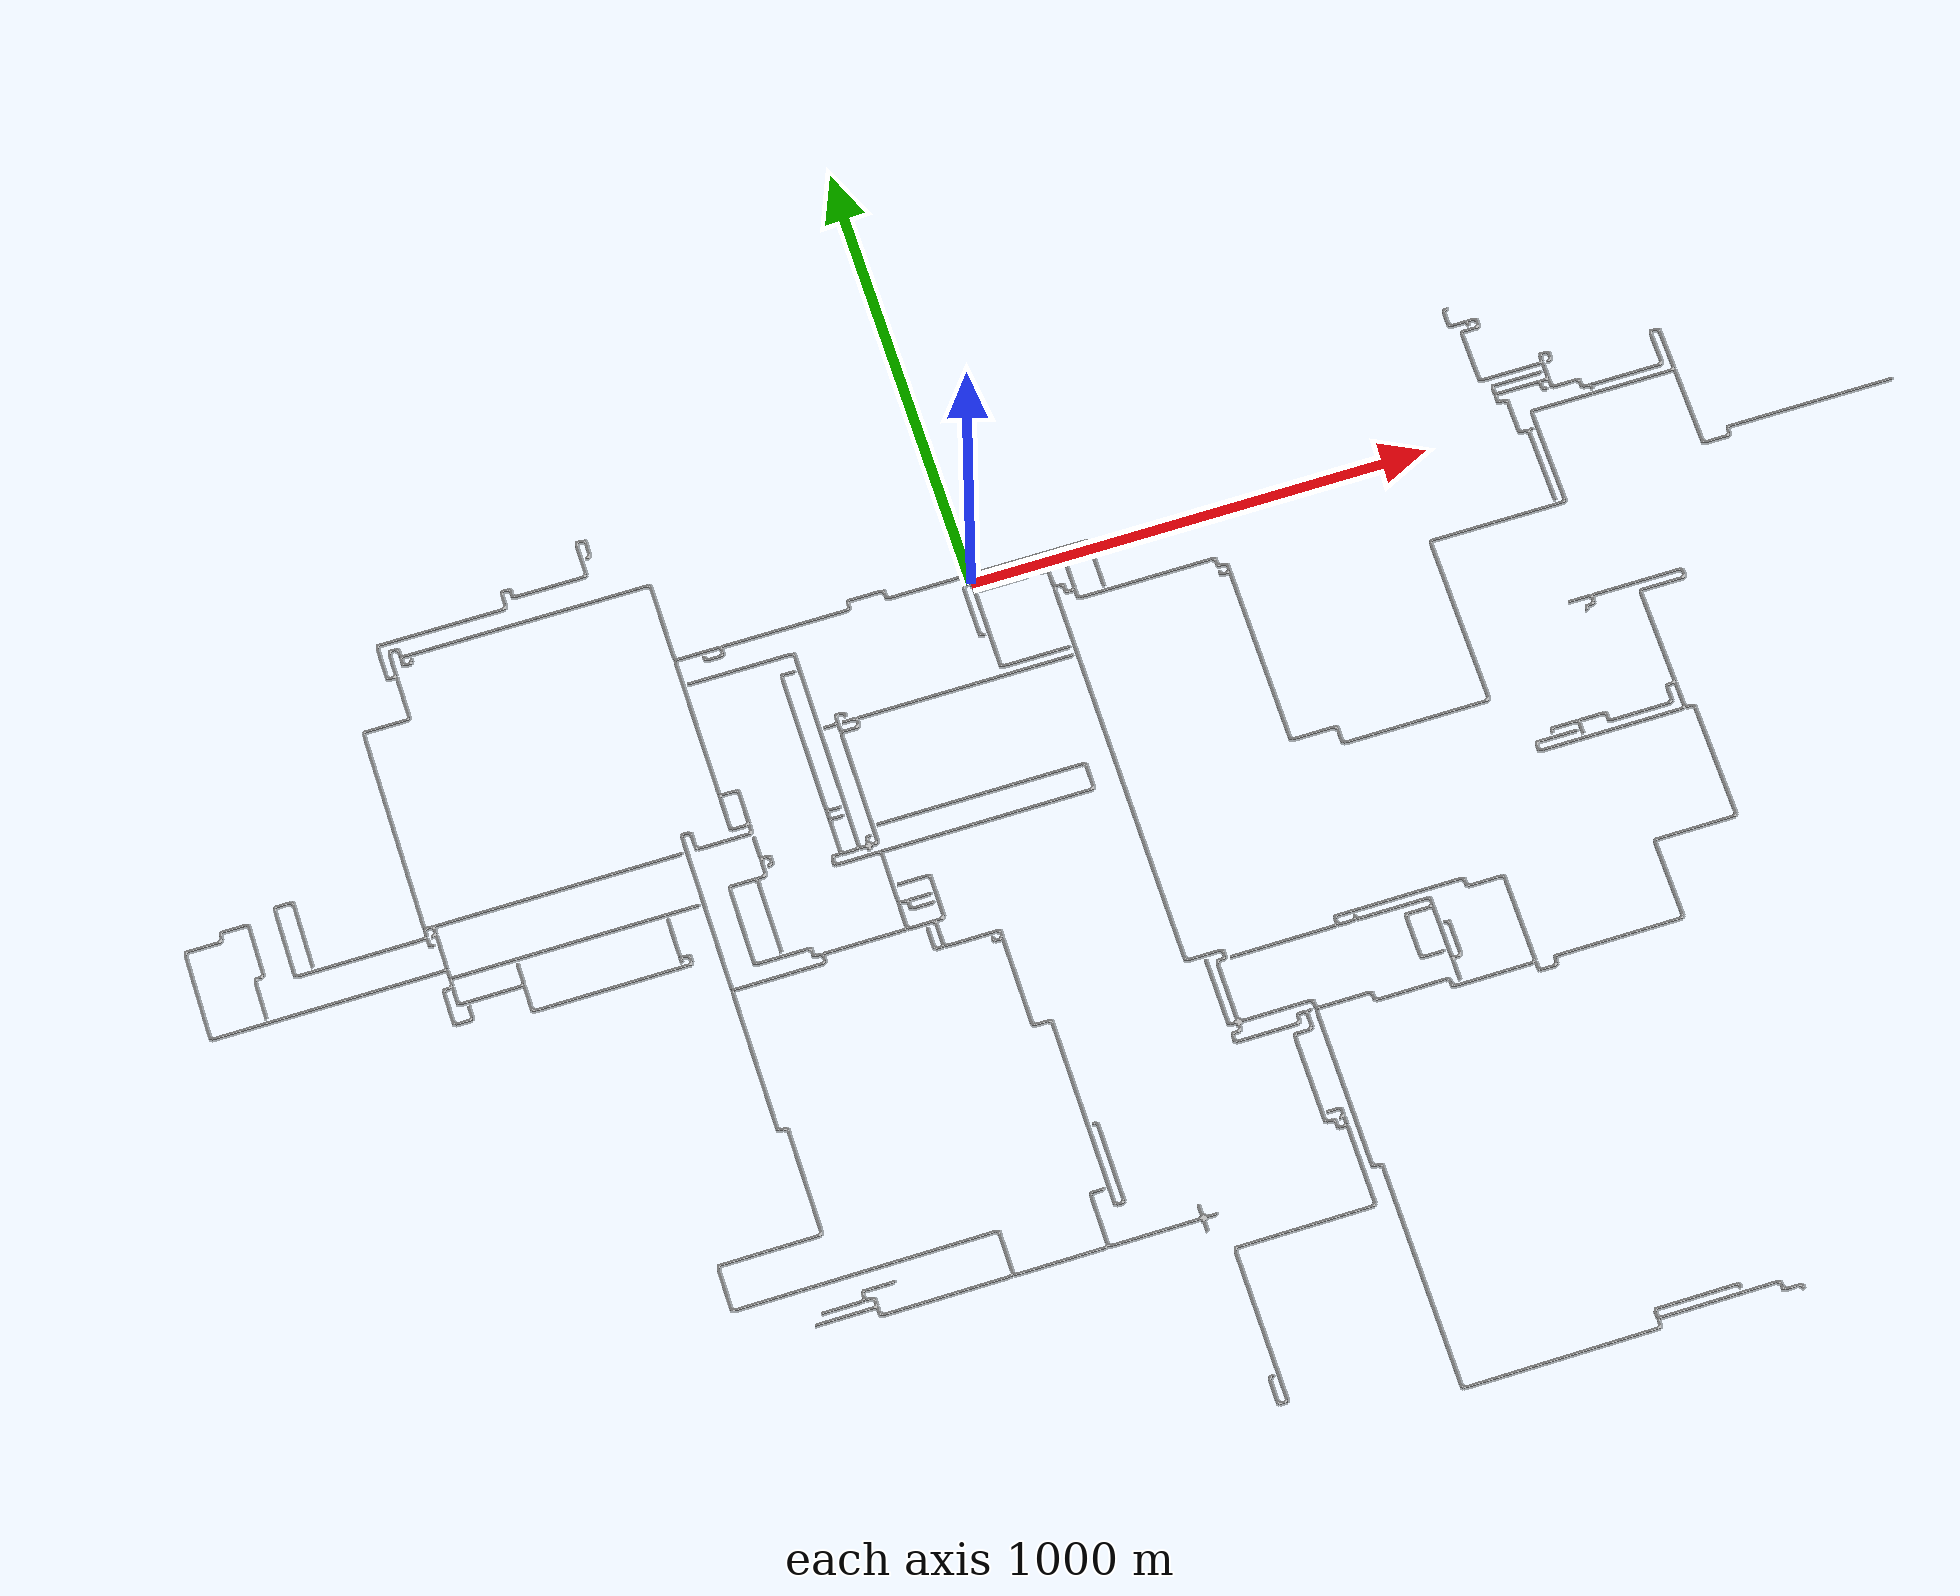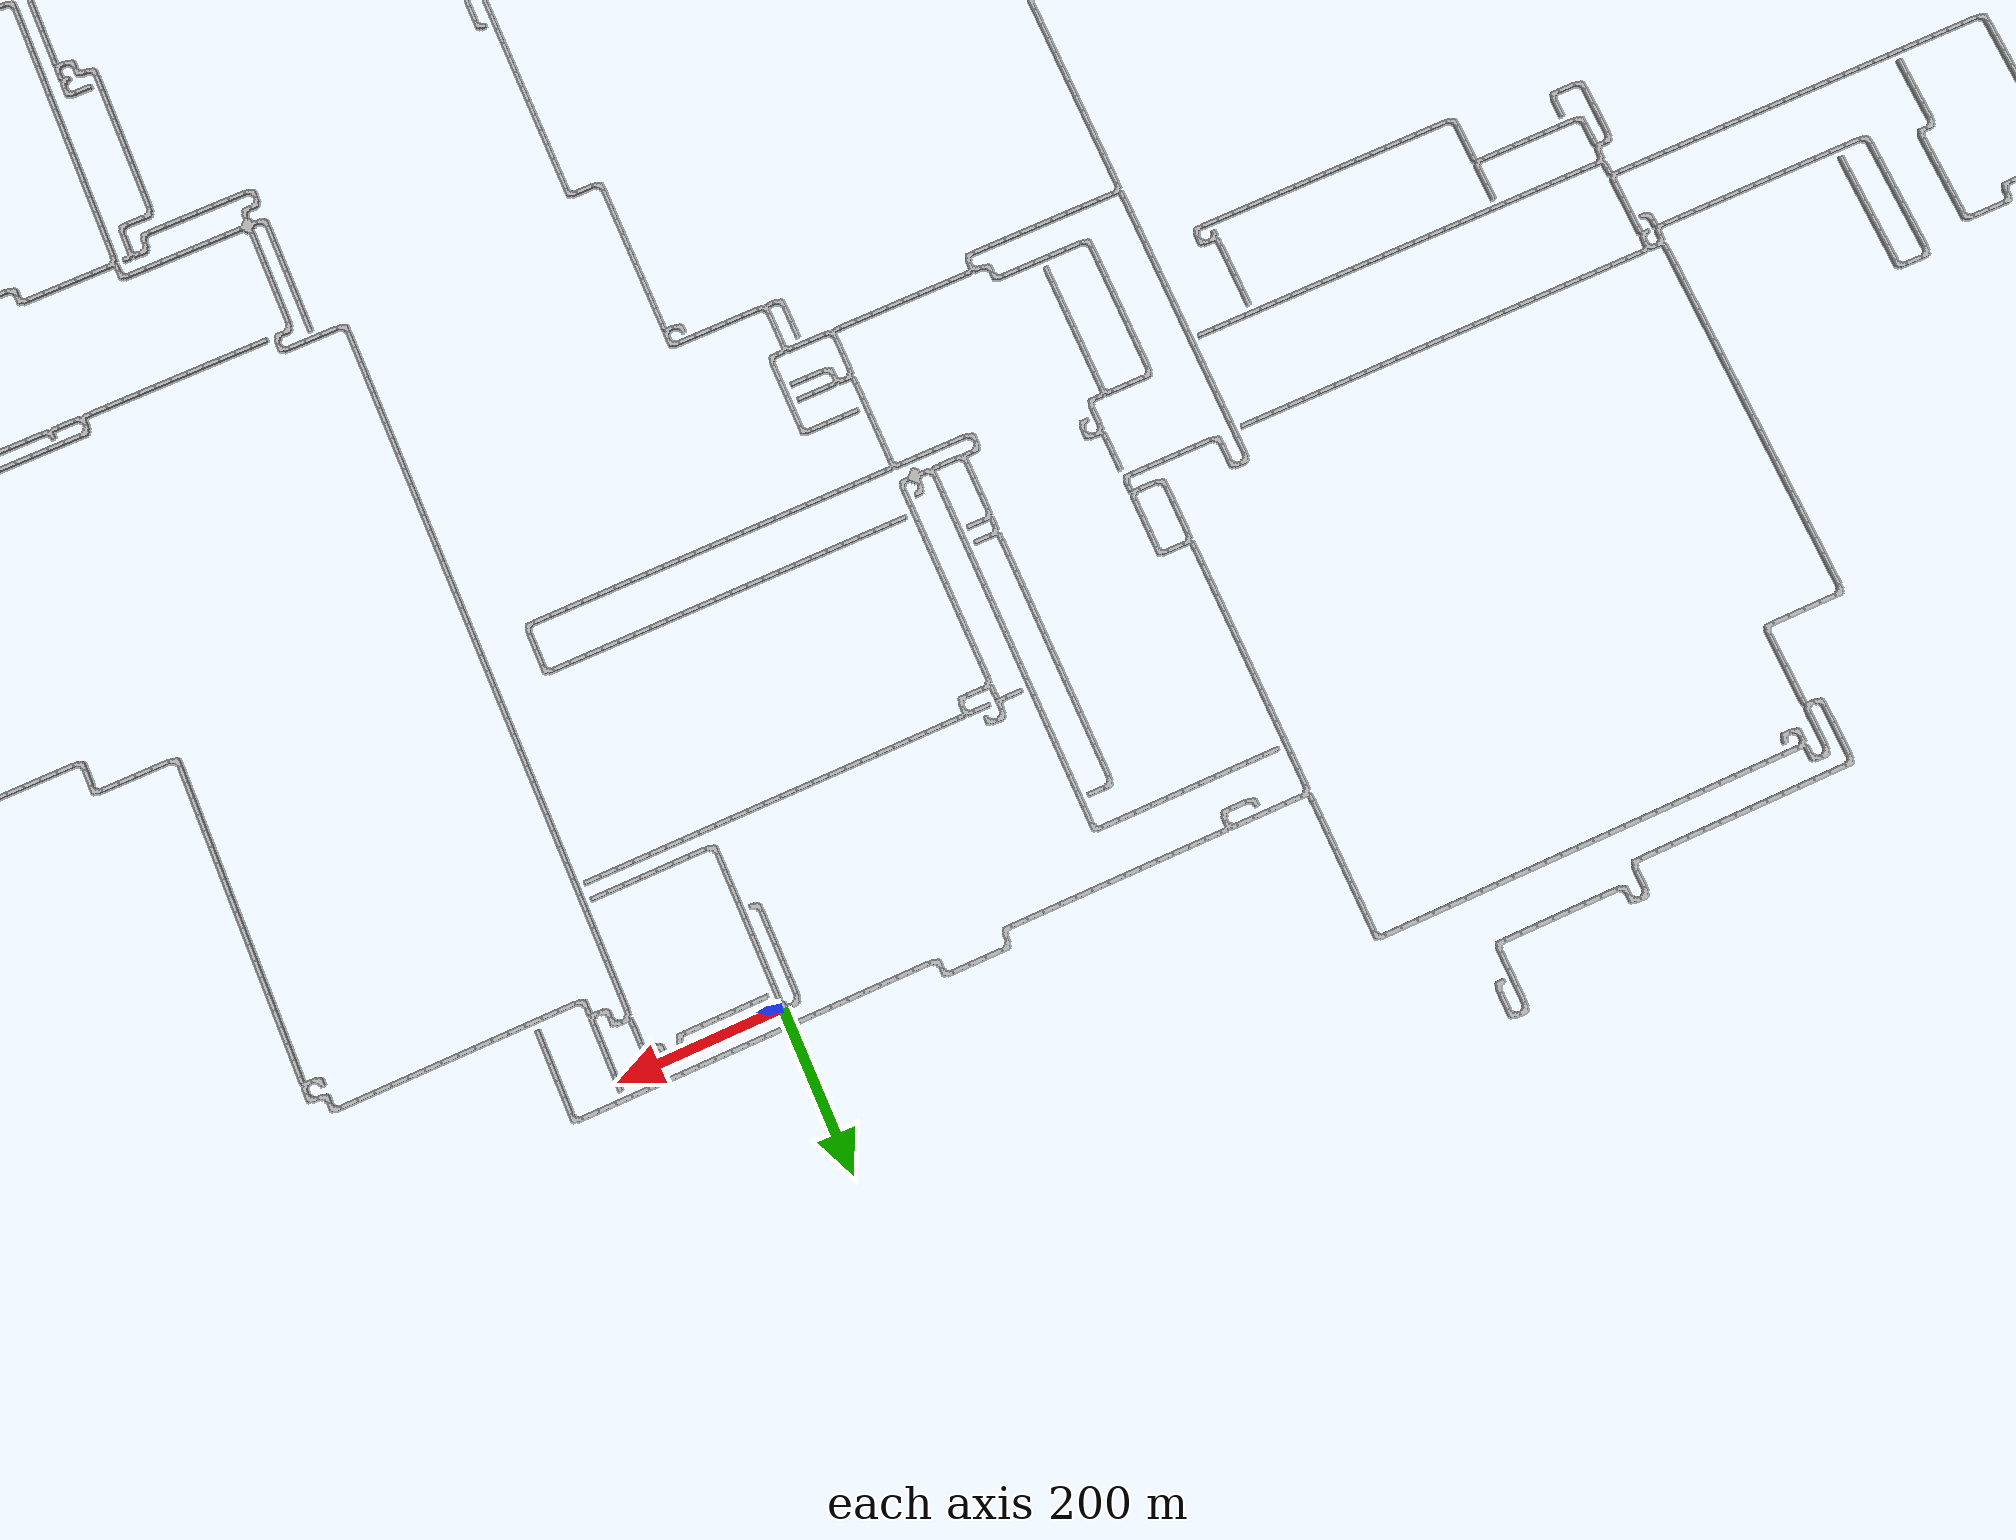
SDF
<sdf version="1.6">
 <world name="cave_32000_16">
  <include>
   <static>true</static>
   <name>cave_0_0</name>
   <pose>0 0 0 0 0 -1.5707963267948966</pose>
   <uri>model://cave_4way_20m</uri>
  </include>
  <include>
   <static>true</static>
   <name>cave_1_0</name>
   <pose>20 0 0 0 0 1.5707963267948966</pose>
   <uri>model://cave_straight_20m</uri>
  </include>
  <include>
   <static>true</static>
   <name>cave_2_0</name>
   <pose>40 0 0 0 0 1.5707963267948966</pose>
   <uri>model://cave_straight_20m</uri>
  </include>
  <include>
   <static>true</static>
   <name>cave_3_0</name>
   <pose>60 0 0 0 0 1.5707963267948966</pose>
   <uri>model://cave_straight_20m</uri>
  </include>
  <include>
   <static>true</static>
   <name>cave_4_0</name>
   <pose>80 0 0 0 0 1.5707963267948966</pose>
   <uri>model://cave_straight_20m</uri>
  </include>
  <include>
   <static>true</static>
   <name>cave_5_0</name>
   <pose>100 0 0 0 0 1.5707963267948966</pose>
   <uri>model://cave_straight_20m</uri>
  </include>
  <include>
   <static>true</static>
   <name>cave_6_0</name>
   <pose>120 0 0 0 0 3.141592653589793</pose>
   <uri>model://cave_3way_20m</uri>
  </include>
  <include>
   <static>true</static>
   <name>cave_7_0</name>
   <pose>140 0 0 0 0 3.141592653589793</pose>
   <uri>model://cave_L_20m</uri>
  </include>
  <include>
   <static>true</static>
   <name>cave_7_-1</name>
   <pose>140 -20 0 0 0 0.0</pose>
   <uri>model://cave_L_20m</uri>
  </include>
  <include>
   <static>true</static>
   <name>cave_8_-1</name>
   <pose>160 -20 0 0 0 1.5707963267948966</pose>
   <uri>model://cave_3way_20m</uri>
  </include>
  <include>
   <static>true</static>
   <name>cave_8_-2</name>
   <pose>160 -40 0 0 0 0.0</pose>
   <uri>model://cave_straight_20m</uri>
  </include>
  <include>
   <static>true</static>
   <name>cave_8_-3</name>
   <pose>160 -60 0 0 0 -1.5707963267948966</pose>
   <uri>model://cave_3way_20m</uri>
  </include>
  <include>
   <static>true</static>
   <name>cave_9_-3</name>
   <pose>180 -60 0 0 0 3.141592653589793</pose>
   <uri>model://cave_L_20m</uri>
  </include>
  <include>
   <static>true</static>
   <name>cave_9_-4</name>
   <pose>180 -80 0 0 0 0.0</pose>
   <uri>model://cave_L_20m</uri>
  </include>
  <include>
   <static>true</static>
   <name>cave_10_-4</name>
   <pose>200 -80 0 0 0 1.5707963267948966</pose>
   <uri>model://cave_3way_20m</uri>
  </include>
  <include>
   <static>true</static>
   <name>cave_10_-5</name>
   <pose>200 -100 0 0 0 0.0</pose>
   <uri>model://cave_L_20m</uri>
  </include>
  <include>
   <static>true</static>
   <name>cave_11_-5</name>
   <pose>220 -100 0 0 0 1.5707963267948966</pose>
   <uri>model://cave_straight_20m</uri>
  </include>
  <include>
   <static>true</static>
   <name>cave_12_-5</name>
   <pose>240 -100 0 0 0 1.5707963267948966</pose>
   <uri>model://cave_straight_20m</uri>
  </include>
  <include>
   <static>true</static>
   <name>cave_13_-5</name>
   <pose>260 -100 0 0 0 1.5707963267948966</pose>
   <uri>model://cave_straight_20m</uri>
  </include>
  <include>
   <static>true</static>
   <name>cave_14_-5</name>
   <pose>280 -100 0 0 0 1.5707963267948966</pose>
   <uri>model://cave_straight_20m</uri>
  </include>
  <include>
   <static>true</static>
   <name>cave_15_-5</name>
   <pose>300 -100 0 0 0 1.5707963267948966</pose>
   <uri>model://cave_straight_20m</uri>
  </include>
  <include>
   <static>true</static>
   <name>cave_16_-5</name>
   <pose>320 -100 0 0 0 1.5707963267948966</pose>
   <uri>model://cave_straight_20m</uri>
  </include>
  <include>
   <static>true</static>
   <name>cave_17_-5</name>
   <pose>340 -100 0 0 0 1.5707963267948966</pose>
   <uri>model://cave_straight_20m</uri>
  </include>
  <include>
   <static>true</static>
   <name>cave_18_-5</name>
   <pose>360 -100 0 0 0 1.5707963267948966</pose>
   <uri>model://cave_straight_20m</uri>
  </include>
  <include>
   <static>true</static>
   <name>cave_19_-5</name>
   <pose>380 -100 0 0 0 1.5707963267948966</pose>
   <uri>model://cave_straight_20m</uri>
  </include>
  <include>
   <static>true</static>
   <name>cave_20_-5</name>
   <pose>400 -100 0 0 0 1.5707963267948966</pose>
   <uri>model://cave_straight_20m</uri>
  </include>
  <include>
   <static>true</static>
   <name>cave_21_-5</name>
   <pose>420 -100 0 0 0 1.5707963267948966</pose>
   <uri>model://cave_straight_20m</uri>
  </include>
  <include>
   <static>true</static>
   <name>cave_22_-5</name>
   <pose>440 -100 0 0 0 1.5707963267948966</pose>
   <uri>model://cave_straight_20m</uri>
  </include>
  <include>
   <static>true</static>
   <name>cave_23_-5</name>
   <pose>460 -100 0 0 0 1.5707963267948966</pose>
   <uri>model://cave_straight_20m</uri>
  </include>
  <include>
   <static>true</static>
   <name>cave_24_-5</name>
   <pose>480 -100 0 0 0 1.5707963267948966</pose>
   <uri>model://cave_straight_20m</uri>
  </include>
  <include>
   <static>true</static>
   <name>cave_25_-5</name>
   <pose>500 -100 0 0 0 3.141592653589793</pose>
   <uri>model://cave_L_20m</uri>
  </include>
  <include>
   <static>true</static>
   <name>cave_25_-6</name>
   <pose>500 -120 0 0 0 0.0</pose>
   <uri>model://cave_L_20m</uri>
  </include>
  <include>
   <static>true</static>
   <name>cave_26_-6</name>
   <pose>520 -120 0 0 0 3.141592653589793</pose>
   <uri>model://cave_L_20m</uri>
  </include>
  <include>
   <static>true</static>
   <name>cave_26_-7</name>
   <pose>520 -140 0 0 0 1.5707963267948966</pose>
   <uri>model://cave_3way_20m</uri>
  </include>
  <include>
   <static>true</static>
   <name>cave_26_-8</name>
   <pose>520 -160 0 0 0 0.0</pose>
   <uri>model://cave_straight_20m</uri>
  </include>
  <include>
   <static>true</static>
   <name>cave_26_-9</name>
   <pose>520 -180 0 0 0 0.0</pose>
   <uri>model://cave_straight_20m</uri>
  </include>
  <include>
   <static>true</static>
   <name>cave_26_-10</name>
   <pose>520 -200 0 0 0 0.0</pose>
   <uri>model://cave_straight_20m</uri>
  </include>
  <include>
   <static>true</static>
   <name>cave_26_-11</name>
   <pose>520 -220 0 0 0 0.0</pose>
   <uri>model://cave_straight_20m</uri>
  </include>
  <include>
   <static>true</static>
   <name>cave_26_-12</name>
   <pose>520 -240 0 0 0 0.0</pose>
   <uri>model://cave_straight_20m</uri>
  </include>
  <include>
   <static>true</static>
   <name>cave_26_-13</name>
   <pose>520 -260 0 0 0 0.0</pose>
   <uri>model://cave_straight_20m</uri>
  </include>
  <include>
   <static>true</static>
   <name>cave_26_-14</name>
   <pose>520 -280 0 0 0 0.0</pose>
   <uri>model://cave_straight_20m</uri>
  </include>
  <include>
   <static>true</static>
   <name>cave_26_-15</name>
   <pose>520 -300 0 0 0 0.0</pose>
   <uri>model://cave_straight_20m</uri>
  </include>
  <include>
   <static>true</static>
   <name>cave_26_-16</name>
   <pose>520 -320 0 0 0 0.0</pose>
   <uri>model://cave_straight_20m</uri>
  </include>
  <include>
   <static>true</static>
   <name>cave_26_-17</name>
   <pose>520 -340 0 0 0 0.0</pose>
   <uri>model://cave_straight_20m</uri>
  </include>
  <include>
   <static>true</static>
   <name>cave_26_-18</name>
   <pose>520 -360 0 0 0 0.0</pose>
   <uri>model://cave_straight_20m</uri>
  </include>
  <include>
   <static>true</static>
   <name>cave_26_-19</name>
   <pose>520 -380 0 0 0 0.0</pose>
   <uri>model://cave_straight_20m</uri>
  </include>
  <include>
   <static>true</static>
   <name>cave_26_-20</name>
   <pose>520 -400 0 0 0 0.0</pose>
   <uri>model://cave_straight_20m</uri>
  </include>
  <include>
   <static>true</static>
   <name>cave_26_-21</name>
   <pose>520 -420 0 0 0 0.0</pose>
   <uri>model://cave_straight_20m</uri>
  </include>
  <include>
   <static>true</static>
   <name>cave_26_-22</name>
   <pose>520 -440 0 0 0 0.0</pose>
   <uri>model://cave_straight_20m</uri>
  </include>
  <include>
   <static>true</static>
   <name>cave_26_-23</name>
   <pose>520 -460 0 0 0 0.0</pose>
   <uri>model://cave_straight_20m</uri>
  </include>
  <include>
   <static>true</static>
   <name>cave_26_-24</name>
   <pose>520 -480 0 0 0 0.0</pose>
   <uri>model://cave_straight_20m</uri>
  </include>
  <include>
   <static>true</static>
   <name>cave_26_-25</name>
   <pose>520 -500 0 0 0 0.0</pose>
   <uri>model://cave_straight_20m</uri>
  </include>
  <include>
   <static>true</static>
   <name>cave_26_-26</name>
   <pose>520 -520 0 0 0 0.0</pose>
   <uri>model://cave_straight_20m</uri>
  </include>
  <include>
   <static>true</static>
   <name>cave_26_-27</name>
   <pose>520 -540 0 0 0 0.0</pose>
   <uri>model://cave_L_20m</uri>
  </include>
  <include>
   <static>true</static>
   <name>cave_27_-27</name>
   <pose>540 -540 0 0 0 1.5707963267948966</pose>
   <uri>model://cave_straight_20m</uri>
  </include>
  <include>
   <static>true</static>
   <name>cave_28_-27</name>
   <pose>560 -540 0 0 0 1.5707963267948966</pose>
   <uri>model://cave_straight_20m</uri>
  </include>
  <include>
   <static>true</static>
   <name>cave_29_-27</name>
   <pose>580 -540 0 0 0 1.5707963267948966</pose>
   <uri>model://cave_straight_20m</uri>
  </include>
  <include>
   <static>true</static>
   <name>cave_30_-27</name>
   <pose>600 -540 0 0 0 1.5707963267948966</pose>
   <uri>model://cave_straight_20m</uri>
  </include>
  <include>
   <static>true</static>
   <name>cave_31_-27</name>
   <pose>620 -540 0 0 0 3.141592653589793</pose>
   <uri>model://cave_L_20m</uri>
  </include>
  <include>
   <static>true</static>
   <name>cave_31_-28</name>
   <pose>620 -560 0 0 0 0.0</pose>
   <uri>model://cave_straight_20m</uri>
  </include>
  <include>
   <static>true</static>
   <name>cave_31_-29</name>
   <pose>620 -580 0 0 0 0.0</pose>
   <uri>model://cave_L_20m</uri>
  </include>
  <include>
   <static>true</static>
   <name>cave_32_-29</name>
   <pose>640 -580 0 0 0 1.5707963267948966</pose>
   <uri>model://cave_straight_20m</uri>
  </include>
  <include>
   <static>true</static>
   <name>cave_33_-29</name>
   <pose>660 -580 0 0 0 1.5707963267948966</pose>
   <uri>model://cave_straight_20m</uri>
  </include>
  <include>
   <static>true</static>
   <name>cave_34_-29</name>
   <pose>680 -580 0 0 0 1.5707963267948966</pose>
   <uri>model://cave_straight_20m</uri>
  </include>
  <include>
   <static>true</static>
   <name>cave_35_-29</name>
   <pose>700 -580 0 0 0 1.5707963267948966</pose>
   <uri>model://cave_straight_20m</uri>
  </include>
  <include>
   <static>true</static>
   <name>cave_36_-29</name>
   <pose>720 -580 0 0 0 1.5707963267948966</pose>
   <uri>model://cave_straight_20m</uri>
  </include>
  <include>
   <static>true</static>
   <name>cave_37_-29</name>
   <pose>740 -580 0 0 0 1.5707963267948966</pose>
   <uri>model://cave_straight_20m</uri>
  </include>
  <include>
   <static>true</static>
   <name>cave_38_-29</name>
   <pose>760 -580 0 0 0 1.5707963267948966</pose>
   <uri>model://cave_straight_20m</uri>
  </include>
  <include>
   <static>true</static>
   <name>cave_39_-29</name>
   <pose>780 -580 0 0 0 1.5707963267948966</pose>
   <uri>model://cave_straight_20m</uri>
  </include>
  <include>
   <static>true</static>
   <name>cave_40_-29</name>
   <pose>800 -580 0 0 0 1.5707963267948966</pose>
   <uri>model://cave_straight_20m</uri>
  </include>
  <include>
   <static>true</static>
   <name>cave_41_-29</name>
   <pose>820 -580 0 0 0 1.5707963267948966</pose>
   <uri>model://cave_straight_20m</uri>
  </include>
  <include>
   <static>true</static>
   <name>cave_42_-29</name>
   <pose>840 -580 0 0 0 1.5707963267948966</pose>
   <uri>model://cave_straight_20m</uri>
  </include>
  <include>
   <static>true</static>
   <name>cave_43_-29</name>
   <pose>860 -580 0 0 0 1.5707963267948966</pose>
   <uri>model://cave_straight_20m</uri>
  </include>
  <include>
   <static>true</static>
   <name>cave_44_-29</name>
   <pose>880 -580 0 0 0 1.5707963267948966</pose>
   <uri>model://cave_straight_20m</uri>
  </include>
  <include>
   <static>true</static>
   <name>cave_45_-29</name>
   <pose>900 -580 0 0 0 1.5707963267948966</pose>
   <uri>model://cave_straight_20m</uri>
  </include>
  <include>
   <static>true</static>
   <name>cave_46_-29</name>
   <pose>920 -580 0 0 0 1.5707963267948966</pose>
   <uri>model://cave_straight_20m</uri>
  </include>
  <include>
   <static>true</static>
   <name>cave_47_-29</name>
   <pose>940 -580 0 0 0 1.5707963267948966</pose>
   <uri>model://cave_L_20m</uri>
  </include>
  <include>
   <static>true</static>
   <name>cave_47_-28</name>
   <pose>940 -560 0 0 0 0.0</pose>
   <uri>model://cave_straight_20m</uri>
  </include>
  <include>
   <static>true</static>
   <name>cave_47_-27</name>
   <pose>940 -540 0 0 0 0.0</pose>
   <uri>model://cave_straight_20m</uri>
  </include>
  <include>
   <static>true</static>
   <name>cave_47_-26</name>
   <pose>940 -520 0 0 0 0.0</pose>
   <uri>model://cave_straight_20m</uri>
  </include>
  <include>
   <static>true</static>
   <name>cave_47_-25</name>
   <pose>940 -500 0 0 0 0.0</pose>
   <uri>model://cave_straight_20m</uri>
  </include>
  <include>
   <static>true</static>
   <name>cave_47_-24</name>
   <pose>940 -480 0 0 0 0.0</pose>
   <uri>model://cave_straight_20m</uri>
  </include>
  <include>
   <static>true</static>
   <name>cave_47_-23</name>
   <pose>940 -460 0 0 0 0.0</pose>
   <uri>model://cave_straight_20m</uri>
  </include>
  <include>
   <static>true</static>
   <name>cave_47_-22</name>
   <pose>940 -440 0 0 0 0.0</pose>
   <uri>model://cave_straight_20m</uri>
  </include>
  <include>
   <static>true</static>
   <name>cave_47_-21</name>
   <pose>940 -420 0 0 0 0.0</pose>
   <uri>model://cave_straight_20m</uri>
  </include>
  <include>
   <static>true</static>
   <name>cave_47_-20</name>
   <pose>940 -400 0 0 0 0.0</pose>
   <uri>model://cave_straight_20m</uri>
  </include>
  <include>
   <static>true</static>
   <name>cave_47_-19</name>
   <pose>940 -380 0 0 0 0.0</pose>
   <uri>model://cave_straight_20m</uri>
  </include>
  <include>
   <static>true</static>
   <name>cave_47_-18</name>
   <pose>940 -360 0 0 0 0.0</pose>
   <uri>model://cave_straight_20m</uri>
  </include>
  <include>
   <static>true</static>
   <name>cave_47_-17</name>
   <pose>940 -340 0 0 0 0.0</pose>
   <uri>model://cave_straight_20m</uri>
  </include>
  <include>
   <static>true</static>
   <name>cave_47_-16</name>
   <pose>940 -320 0 0 0 0.0</pose>
   <uri>model://cave_straight_20m</uri>
  </include>
  <include>
   <static>true</static>
   <name>cave_47_-15</name>
   <pose>940 -300 0 0 0 0.0</pose>
   <uri>model://cave_straight_20m</uri>
  </include>
  <include>
   <static>true</static>
   <name>cave_47_-14</name>
   <pose>940 -280 0 0 0 0.0</pose>
   <uri>model://cave_straight_20m</uri>
  </include>
  <include>
   <static>true</static>
   <name>cave_47_-13</name>
   <pose>940 -260 0 0 0 0.0</pose>
   <uri>model://cave_straight_20m</uri>
  </include>
  <include>
   <static>true</static>
   <name>cave_47_-12</name>
   <pose>940 -240 0 0 0 0.0</pose>
   <uri>model://cave_straight_20m</uri>
  </include>
  <include>
   <static>true</static>
   <name>cave_47_-11</name>
   <pose>940 -220 0 0 0 0.0</pose>
   <uri>model://cave_straight_20m</uri>
  </include>
  <include>
   <static>true</static>
   <name>cave_47_-10</name>
   <pose>940 -200 0 0 0 -1.5707963267948966</pose>
   <uri>model://cave_L_20m</uri>
  </include>
  <include>
   <static>true</static>
   <name>cave_48_-10</name>
   <pose>960 -200 0 0 0 1.5707963267948966</pose>
   <uri>model://cave_straight_20m</uri>
  </include>
  <include>
   <static>true</static>
   <name>cave_49_-10</name>
   <pose>980 -200 0 0 0 1.5707963267948966</pose>
   <uri>model://cave_straight_20m</uri>
  </include>
  <include>
   <static>true</static>
   <name>cave_50_-10</name>
   <pose>1000 -200 0 0 0 1.5707963267948966</pose>
   <uri>model://cave_straight_20m</uri>
  </include>
  <include>
   <static>true</static>
   <name>cave_51_-10</name>
   <pose>1020 -200 0 0 0 1.5707963267948966</pose>
   <uri>model://cave_straight_20m</uri>
  </include>
  <include>
   <static>true</static>
   <name>cave_52_-10</name>
   <pose>1040 -200 0 0 0 1.5707963267948966</pose>
   <uri>model://cave_straight_20m</uri>
  </include>
  <include>
   <static>true</static>
   <name>cave_53_-10</name>
   <pose>1060 -200 0 0 0 1.5707963267948966</pose>
   <uri>model://cave_straight_20m</uri>
  </include>
  <include>
   <static>true</static>
   <name>cave_54_-10</name>
   <pose>1080 -200 0 0 0 1.5707963267948966</pose>
   <uri>model://cave_straight_20m</uri>
  </include>
  <include>
   <static>true</static>
   <name>cave_55_-10</name>
   <pose>1100 -200 0 0 0 1.5707963267948966</pose>
   <uri>model://cave_straight_20m</uri>
  </include>
  <include>
   <static>true</static>
   <name>cave_56_-10</name>
   <pose>1120 -200 0 0 0 1.5707963267948966</pose>
   <uri>model://cave_straight_20m</uri>
  </include>
  <include>
   <static>true</static>
   <name>cave_57_-10</name>
   <pose>1140 -200 0 0 0 1.5707963267948966</pose>
   <uri>model://cave_straight_20m</uri>
  </include>
  <include>
   <static>true</static>
   <name>cave_58_-10</name>
   <pose>1160 -200 0 0 0 1.5707963267948966</pose>
   <uri>model://cave_straight_20m</uri>
  </include>
  <include>
   <static>true</static>
   <name>cave_59_-10</name>
   <pose>1180 -200 0 0 0 1.5707963267948966</pose>
   <uri>model://cave_straight_20m</uri>
  </include>
  <include>
   <static>true</static>
   <name>cave_60_-10</name>
   <pose>1200 -200 0 0 0 1.5707963267948966</pose>
   <uri>model://cave_straight_20m</uri>
  </include>
  <include>
   <static>true</static>
   <name>cave_61_-10</name>
   <pose>1220 -200 0 0 0 1.5707963267948966</pose>
   <uri>model://cave_straight_20m</uri>
  </include>
  <include>
   <static>true</static>
   <name>cave_62_-10</name>
   <pose>1240 -200 0 0 0 1.5707963267948966</pose>
   <uri>model://cave_L_20m</uri>
  </include>
  <include>
   <static>true</static>
   <name>cave_62_-9</name>
   <pose>1240 -180 0 0 0 0.0</pose>
   <uri>model://cave_straight_20m</uri>
  </include>
  <include>
   <static>true</static>
   <name>cave_62_-8</name>
   <pose>1240 -160 0 0 0 0.0</pose>
   <uri>model://cave_straight_20m</uri>
  </include>
  <include>
   <static>true</static>
   <name>cave_62_-7</name>
   <pose>1240 -140 0 0 0 0.0</pose>
   <uri>model://cave_straight_20m</uri>
  </include>
  <include>
   <static>true</static>
   <name>cave_62_-6</name>
   <pose>1240 -120 0 0 0 0.0</pose>
   <uri>model://cave_straight_20m</uri>
  </include>
  <include>
   <static>true</static>
   <name>cave_62_-5</name>
   <pose>1240 -100 0 0 0 0.0</pose>
   <uri>model://cave_straight_20m</uri>
  </include>
  <include>
   <static>true</static>
   <name>cave_62_-4</name>
   <pose>1240 -80 0 0 0 0.0</pose>
   <uri>model://cave_straight_20m</uri>
  </include>
  <include>
   <static>true</static>
   <name>cave_62_-3</name>
   <pose>1240 -60 0 0 0 0.0</pose>
   <uri>model://cave_straight_20m</uri>
  </include>
  <include>
   <static>true</static>
   <name>cave_62_-2</name>
   <pose>1240 -40 0 0 0 0.0</pose>
   <uri>model://cave_straight_20m</uri>
  </include>
  <include>
   <static>true</static>
   <name>cave_62_-1</name>
   <pose>1240 -20 0 0 0 0.0</pose>
   <uri>model://cave_straight_20m</uri>
  </include>
  <include>
   <static>true</static>
   <name>cave_62_0</name>
   <pose>1240 0 0 0 0 0.0</pose>
   <uri>model://cave_straight_20m</uri>
  </include>
  <include>
   <static>true</static>
   <name>cave_62_1</name>
   <pose>1240 20 0 0 0 -1.5707963267948966</pose>
   <uri>model://cave_L_20m</uri>
  </include>
  <include>
   <static>true</static>
   <name>cave_63_1</name>
   <pose>1260 20 0 0 0 1.5707963267948966</pose>
   <uri>model://cave_straight_20m</uri>
  </include>
  <include>
   <static>true</static>
   <name>cave_64_1</name>
   <pose>1280 20 0 0 0 1.5707963267948966</pose>
   <uri>model://cave_straight_20m</uri>
  </include>
  <include>
   <static>true</static>
   <name>cave_65_1</name>
   <pose>1300 20 0 0 0 1.5707963267948966</pose>
   <uri>model://cave_straight_20m</uri>
  </include>
  <include>
   <static>true</static>
   <name>cave_66_1</name>
   <pose>1320 20 0 0 0 1.5707963267948966</pose>
   <uri>model://cave_straight_20m</uri>
  </include>
  <include>
   <static>true</static>
   <name>cave_67_1</name>
   <pose>1340 20 0 0 0 1.5707963267948966</pose>
   <uri>model://cave_straight_20m</uri>
  </include>
  <include>
   <static>true</static>
   <name>cave_68_1</name>
   <pose>1360 20 0 0 0 1.5707963267948966</pose>
   <uri>model://cave_straight_20m</uri>
  </include>
  <include>
   <static>true</static>
   <name>cave_69_1</name>
   <pose>1380 20 0 0 0 1.5707963267948966</pose>
   <uri>model://cave_straight_20m</uri>
  </include>
  <include>
   <static>true</static>
   <name>cave_70_1</name>
   <pose>1400 20 0 0 0 1.5707963267948966</pose>
   <uri>model://cave_straight_20m</uri>
  </include>
  <include>
   <static>true</static>
   <name>cave_71_1</name>
   <pose>1420 20 0 0 0 1.5707963267948966</pose>
   <uri>model://cave_straight_20m</uri>
  </include>
  <include>
   <static>true</static>
   <name>cave_72_1</name>
   <pose>1440 20 0 0 0 1.5707963267948966</pose>
   <uri>model://cave_straight_20m</uri>
  </include>
  <include>
   <static>true</static>
   <name>cave_73_1</name>
   <pose>1460 20 0 0 0 1.5707963267948966</pose>
   <uri>model://cave_straight_20m</uri>
  </include>
  <include>
   <static>true</static>
   <name>cave_74_1</name>
   <pose>1480 20 0 0 0 1.5707963267948966</pose>
   <uri>model://cave_straight_20m</uri>
  </include>
  <include>
   <static>true</static>
   <name>cave_75_1</name>
   <pose>1500 20 0 0 0 1.5707963267948966</pose>
   <uri>model://cave_straight_20m</uri>
  </include>
  <include>
   <static>true</static>
   <name>cave_76_1</name>
   <pose>1520 20 0 0 0 1.5707963267948966</pose>
   <uri>model://cave_straight_20m</uri>
  </include>
  <include>
   <static>true</static>
   <name>cave_77_1</name>
   <pose>1540 20 0 0 0 1.5707963267948966</pose>
   <uri>model://cave_straight_20m</uri>
  </include>
  <include>
   <static>true</static>
   <name>cave_78_1</name>
   <pose>1560 20 0 0 0 1.5707963267948966</pose>
   <uri>model://cave_3way_20m</uri>
  </include>
  <include>
   <static>true</static>
   <name>cave_78_0</name>
   <pose>1560 0 0 0 0 0.0</pose>
   <uri>model://cave_straight_20m</uri>
  </include>
  <include>
   <static>true</static>
   <name>cave_78_-1</name>
   <pose>1560 -20 0 0 0 0.0</pose>
   <uri>model://cave_straight_20m</uri>
  </include>
  <include>
   <static>true</static>
   <name>cave_78_-2</name>
   <pose>1560 -40 0 0 0 0.0</pose>
   <uri>model://cave_straight_20m</uri>
  </include>
  <include>
   <static>true</static>
   <name>cave_78_-3</name>
   <pose>1560 -60 0 0 0 0.0</pose>
   <uri>model://cave_straight_20m</uri>
  </include>
  <include>
   <static>true</static>
   <name>cave_78_-4</name>
   <pose>1560 -80 0 0 0 0.0</pose>
   <uri>model://cave_straight_20m</uri>
  </include>
  <include>
   <static>true</static>
   <name>cave_78_-5</name>
   <pose>1560 -100 0 0 0 0.0</pose>
   <uri>model://cave_straight_20m</uri>
  </include>
  <include>
   <static>true</static>
   <name>cave_78_-6</name>
   <pose>1560 -120 0 0 0 0.0</pose>
   <uri>model://cave_straight_20m</uri>
  </include>
  <include>
   <static>true</static>
   <name>cave_78_-7</name>
   <pose>1560 -140 0 0 0 0.0</pose>
   <uri>model://cave_straight_20m</uri>
  </include>
  <include>
   <static>true</static>
   <name>cave_78_-8</name>
   <pose>1560 -160 0 0 0 0.0</pose>
   <uri>model://cave_L_20m</uri>
  </include>
  <include>
   <static>true</static>
   <name>cave_79_-8</name>
   <pose>1580 -160 0 0 0 1.5707963267948966</pose>
   <uri>model://cave_straight_20m</uri>
  </include>
  <include>
   <static>true</static>
   <name>cave_80_-8</name>
   <pose>1600 -160 0 0 0 1.5707963267948966</pose>
   <uri>model://cave_straight_20m</uri>
  </include>
  <include>
   <static>true</static>
   <name>cave_81_-8</name>
   <pose>1620 -160 0 0 0 1.5707963267948966</pose>
   <uri>model://cave_L_20m</uri>
  </include>
  <include>
   <static>true</static>
   <name>cave_81_-7</name>
   <pose>1620 -140 0 0 0 -1.5707963267948966</pose>
   <uri>model://cave_L_20m</uri>
  </include>
  <include>
   <static>true</static>
   <name>cave_82_-7</name>
   <pose>1640 -140 0 0 0 1.5707963267948966</pose>
   <uri>model://cave_straight_20m</uri>
  </include>
  <include>
   <static>true</static>
   <name>cave_83_-7</name>
   <pose>1660 -140 0 0 0 1.5707963267948966</pose>
   <uri>model://cave_straight_20m</uri>
  </include>
  <include>
   <static>true</static>
   <name>cave_84_-7</name>
   <pose>1680 -140 0 0 0 1.5707963267948966</pose>
   <uri>model://cave_straight_20m</uri>
  </include>
  <include>
   <static>true</static>
   <name>cave_85_-7</name>
   <pose>1700 -140 0 0 0 1.5707963267948966</pose>
   <uri>model://cave_straight_20m</uri>
  </include>
  <include>
   <static>true</static>
   <name>cave_86_-7</name>
   <pose>1720 -140 0 0 0 1.5707963267948966</pose>
   <uri>model://cave_straight_20m</uri>
  </include>
  <include>
   <static>true</static>
   <name>cave_87_-7</name>
   <pose>1740 -140 0 0 0 1.5707963267948966</pose>
   <uri>model://cave_straight_20m</uri>
  </include>
  <include>
   <static>true</static>
   <name>cave_88_-7</name>
   <pose>1760 -140 0 0 0 1.5707963267948966</pose>
   <uri>model://cave_straight_20m</uri>
  </include>
  <include>
   <static>true</static>
   <name>cave_89_-7</name>
   <pose>1780 -140 0 0 0 1.5707963267948966</pose>
   <uri>model://cave_straight_20m</uri>
  </include>
  <include>
   <static>true</static>
   <name>cave_90_-7</name>
   <pose>1800 -140 0 0 0 1.5707963267948966</pose>
   <uri>model://cave_straight_20m</uri>
  </include>
  <include>
   <static>true</static>
   <name>cave_91_-7</name>
   <pose>1820 -140 0 0 0 1.5707963267948966</pose>
   <uri>model://cave_straight_20m</uri>
  </include>
  <include>
   <static>true</static>
   <name>cave_92_-7</name>
   <pose>1840 -140 0 0 0 1.5707963267948966</pose>
   <uri>model://cave_straight_20m</uri>
  </include>
  <include>
   <static>true</static>
   <name>cave_93_-7</name>
   <pose>1860 -140 0 0 0 1.5707963267948966</pose>
   <uri>model://cave_straight_20m</uri>
  </include>
  <include>
   <static>true</static>
   <name>cave_94_-7</name>
   <pose>1880 -140 0 0 0 1.5707963267948966</pose>
   <uri>model://cave_straight_20m</uri>
  </include>
  <include>
   <static>true</static>
   <name>cave_95_-7</name>
   <pose>1900 -140 0 0 0 1.5707963267948966</pose>
   <uri>model://cave_straight_20m</uri>
  </include>
  <include>
   <static>true</static>
   <name>cave_96_-7</name>
   <pose>1920 -140 0 0 0 1.5707963267948966</pose>
   <uri>model://cave_straight_20m</uri>
  </include>
  <include>
   <static>true</static>
   <name>cave_97_-7</name>
   <pose>1940 -140 0 0 0 1.5707963267948966</pose>
   <uri>model://cave_straight_20m</uri>
  </include>
  <include>
   <static>true</static>
   <name>cave_98_-7</name>
   <pose>1960 -140 0 0 0 1.5707963267948966</pose>
   <uri>model://cave_straight_20m</uri>
  </include>
  <include>
   <static>true</static>
   <name>cave_99_-7</name>
   <pose>1980 -140 0 0 0 1.5707963267948966</pose>
   <uri>model://cave_straight_20m</uri>
  </include>
  <include>
   <static>true</static>
   <name>cave_78_2</name>
   <pose>1560 40 0 0 0 0.0</pose>
   <uri>model://cave_straight_20m</uri>
  </include>
  <include>
   <static>true</static>
   <name>cave_78_3</name>
   <pose>1560 60 0 0 0 0.0</pose>
   <uri>model://cave_straight_20m</uri>
  </include>
  <include>
   <static>true</static>
   <name>cave_78_4</name>
   <pose>1560 80 0 0 0 0.0</pose>
   <uri>model://cave_straight_20m</uri>
  </include>
  <include>
   <static>true</static>
   <name>cave_78_5</name>
   <pose>1560 100 0 0 0 0.0</pose>
   <uri>model://cave_straight_20m</uri>
  </include>
  <include>
   <static>true</static>
   <name>cave_78_6</name>
   <pose>1560 120 0 0 0 3.141592653589793</pose>
   <uri>model://cave_L_20m</uri>
  </include>
  <include>
   <static>true</static>
   <name>cave_77_6</name>
   <pose>1540 120 0 0 0 -1.5707963267948966</pose>
   <uri>model://cave_L_20m</uri>
  </include>
  <include>
   <static>true</static>
   <name>cave_77_5</name>
   <pose>1540 100 0 0 0 0.0</pose>
   <uri>model://cave_straight_20m</uri>
  </include>
  <include>
   <static>true</static>
   <name>cave_77_4</name>
   <pose>1540 80 0 0 0 0.0</pose>
   <uri>model://cave_straight_20m</uri>
  </include>
  <include>
   <static>true</static>
   <name>cave_77_3</name>
   <pose>1540 60 0 0 0 0.0</pose>
   <uri>model://cave_straight_20m</uri>
  </include>
  <include>
   <static>true</static>
   <name>cave_77_2</name>
   <pose>1540 40 0 0 0 1.5707963267948966</pose>
   <uri>model://cave_L_20m</uri>
  </include>
  <include>
   <static>true</static>
   <name>cave_76_2</name>
   <pose>1520 40 0 0 0 1.5707963267948966</pose>
   <uri>model://cave_straight_20m</uri>
  </include>
  <include>
   <static>true</static>
   <name>cave_75_2</name>
   <pose>1500 40 0 0 0 1.5707963267948966</pose>
   <uri>model://cave_straight_20m</uri>
  </include>
  <include>
   <static>true</static>
   <name>cave_74_2</name>
   <pose>1480 40 0 0 0 1.5707963267948966</pose>
   <uri>model://cave_straight_20m</uri>
  </include>
  <include>
   <static>true</static>
   <name>cave_73_2</name>
   <pose>1460 40 0 0 0 1.5707963267948966</pose>
   <uri>model://cave_straight_20m</uri>
  </include>
  <include>
   <static>true</static>
   <name>cave_72_2</name>
   <pose>1440 40 0 0 0 1.5707963267948966</pose>
   <uri>model://cave_straight_20m</uri>
  </include>
  <include>
   <static>true</static>
   <name>cave_71_2</name>
   <pose>1420 40 0 0 0 1.5707963267948966</pose>
   <uri>model://cave_straight_20m</uri>
  </include>
  <include>
   <static>true</static>
   <name>cave_70_2</name>
   <pose>1400 40 0 0 0 1.5707963267948966</pose>
   <uri>model://cave_straight_20m</uri>
  </include>
  <include>
   <static>true</static>
   <name>cave_69_2</name>
   <pose>1380 40 0 0 0 3.141592653589793</pose>
   <uri>model://cave_3way_20m</uri>
  </include>
  <include>
   <static>true</static>
   <name>cave_68_2</name>
   <pose>1360 40 0 0 0 0.0</pose>
   <uri>model://cave_L_20m</uri>
  </include>
  <include>
   <static>true</static>
   <name>cave_68_3</name>
   <pose>1360 60 0 0 0 3.141592653589793</pose>
   <uri>model://cave_L_20m</uri>
  </include>
  <include>
   <static>true</static>
   <name>cave_67_3</name>
   <pose>1340 60 0 0 0 1.5707963267948966</pose>
   <uri>model://cave_straight_20m</uri>
  </include>
  <include>
   <static>true</static>
   <name>cave_66_3</name>
   <pose>1320 60 0 0 0 1.5707963267948966</pose>
   <uri>model://cave_straight_20m</uri>
  </include>
  <include>
   <static>true</static>
   <name>cave_65_3</name>
   <pose>1300 60 0 0 0 0.0</pose>
   <uri>model://cave_L_20m</uri>
  </include>
  <include>
   <static>true</static>
   <name>cave_65_4</name>
   <pose>1300 80 0 0 0 1.5707963267948966</pose>
   <uri>model://cave_3way_20m</uri>
  </include>
  <include>
   <static>true</static>
   <name>cave_64_4</name>
   <pose>1280 80 0 0 0 3.141592653589793</pose>
   <uri>model://cave_3way_20m</uri>
  </include>
  <include>
   <static>true</static>
   <name>cave_64_3</name>
   <pose>1280 60 0 0 0 0.0</pose>
   <uri>model://cave_L_20m</uri>
  </include>
  <include>
   <static>true</static>
   <name>cave_63_4</name>
   <pose>1260 80 0 0 0 1.5707963267948966</pose>
   <uri>model://cave_straight_20m</uri>
  </include>
  <include>
   <static>true</static>
   <name>cave_62_4</name>
   <pose>1240 80 0 0 0 1.5707963267948966</pose>
   <uri>model://cave_straight_20m</uri>
  </include>
  <include>
   <static>true</static>
   <name>cave_61_4</name>
   <pose>1220 80 0 0 0 1.5707963267948966</pose>
   <uri>model://cave_straight_20m</uri>
  </include>
  <include>
   <static>true</static>
   <name>cave_60_4</name>
   <pose>1200 80 0 0 0 1.5707963267948966</pose>
   <uri>model://cave_straight_20m</uri>
  </include>
  <include>
   <static>true</static>
   <name>cave_59_4</name>
   <pose>1180 80 0 0 0 -1.5707963267948966</pose>
   <uri>model://cave_3way_20m</uri>
  </include>
  <include>
   <static>true</static>
   <name>cave_59_3</name>
   <pose>1180 60 0 0 0 0.0</pose>
   <uri>model://cave_L_20m</uri>
  </include>
  <include>
   <static>true</static>
   <name>cave_60_3</name>
   <pose>1200 60 0 0 0 3.141592653589793</pose>
   <uri>model://cave_L_20m</uri>
  </include>
  <include>
   <static>true</static>
   <name>cave_60_2</name>
   <pose>1200 40 0 0 0 0.0</pose>
   <uri>model://cave_straight_20m</uri>
  </include>
  <include>
   <static>true</static>
   <name>cave_60_1</name>
   <pose>1200 20 0 0 0 0.0</pose>
   <uri>model://cave_straight_20m</uri>
  </include>
  <include>
   <static>true</static>
   <name>cave_60_0</name>
   <pose>1200 0 0 0 0 0.0</pose>
   <uri>model://cave_straight_20m</uri>
  </include>
  <include>
   <static>true</static>
   <name>cave_60_-1</name>
   <pose>1200 -20 0 0 0 0.0</pose>
   <uri>model://cave_L_20m</uri>
  </include>
  <include>
   <static>true</static>
   <name>cave_61_-1</name>
   <pose>1220 -20 0 0 0 3.141592653589793</pose>
   <uri>model://cave_3way_20m</uri>
  </include>
  <include>
   <static>true</static>
   <name>cave_61_-2</name>
   <pose>1220 -40 0 0 0 0.0</pose>
   <uri>model://cave_straight_20m</uri>
  </include>
  <include>
   <static>true</static>
   <name>cave_61_-3</name>
   <pose>1220 -60 0 0 0 0.0</pose>
   <uri>model://cave_straight_20m</uri>
  </include>
  <include>
   <static>true</static>
   <name>cave_61_-4</name>
   <pose>1220 -80 0 0 0 0.0</pose>
   <uri>model://cave_straight_20m</uri>
  </include>
  <include>
   <static>true</static>
   <name>cave_61_-5</name>
   <pose>1220 -100 0 0 0 0.0</pose>
   <uri>model://cave_straight_20m</uri>
  </include>
  <include>
   <static>true</static>
   <name>cave_61_-6</name>
   <pose>1220 -120 0 0 0 0.0</pose>
   <uri>model://cave_straight_20m</uri>
  </include>
  <include>
   <static>true</static>
   <name>cave_61_-7</name>
   <pose>1220 -140 0 0 0 0.0</pose>
   <uri>model://cave_straight_20m</uri>
  </include>
  <include>
   <static>true</static>
   <name>cave_61_-8</name>
   <pose>1220 -160 0 0 0 0.0</pose>
   <uri>model://cave_straight_20m</uri>
  </include>
  <include>
   <static>true</static>
   <name>cave_61_-9</name>
   <pose>1220 -180 0 0 0 0.0</pose>
   <uri>model://cave_straight_20m</uri>
  </include>
  <include>
   <static>true</static>
   <name>cave_59_5</name>
   <pose>1180 100 0 0 0 -1.5707963267948966</pose>
   <uri>model://cave_L_20m</uri>
  </include>
  <include>
   <static>true</static>
   <name>cave_60_5</name>
   <pose>1200 100 0 0 0 1.5707963267948966</pose>
   <uri>model://cave_straight_20m</uri>
  </include>
  <include>
   <static>true</static>
   <name>cave_61_5</name>
   <pose>1220 100 0 0 0 1.5707963267948966</pose>
   <uri>model://cave_straight_20m</uri>
  </include>
  <include>
   <static>true</static>
   <name>cave_62_5</name>
   <pose>1240 100 0 0 0 1.5707963267948966</pose>
   <uri>model://cave_straight_20m</uri>
  </include>
  <include>
   <static>true</static>
   <name>cave_63_5</name>
   <pose>1260 100 0 0 0 1.5707963267948966</pose>
   <uri>model://cave_straight_20m</uri>
  </include>
  <include>
   <static>true</static>
   <name>cave_64_5</name>
   <pose>1280 100 0 0 0 1.5707963267948966</pose>
   <uri>model://cave_straight_20m</uri>
  </include>
  <include>
   <static>true</static>
   <name>cave_65_5</name>
   <pose>1300 100 0 0 0 0.0</pose>
   <uri>model://cave_straight_20m</uri>
  </include>
  <include>
   <static>true</static>
   <name>cave_65_6</name>
   <pose>1300 120 0 0 0 1.5707963267948966</pose>
   <uri>model://cave_3way_20m</uri>
  </include>
  <include>
   <static>true</static>
   <name>cave_64_6</name>
   <pose>1280 120 0 0 0 1.5707963267948966</pose>
   <uri>model://cave_straight_20m</uri>
  </include>
  <include>
   <static>true</static>
   <name>cave_63_6</name>
   <pose>1260 120 0 0 0 1.5707963267948966</pose>
   <uri>model://cave_straight_20m</uri>
  </include>
  <include>
   <static>true</static>
   <name>cave_62_6</name>
   <pose>1240 120 0 0 0 1.5707963267948966</pose>
   <uri>model://cave_straight_20m</uri>
  </include>
  <include>
   <static>true</static>
   <name>cave_61_6</name>
   <pose>1220 120 0 0 0 1.5707963267948966</pose>
   <uri>model://cave_straight_20m</uri>
  </include>
  <include>
   <static>true</static>
   <name>cave_60_6</name>
   <pose>1200 120 0 0 0 1.5707963267948966</pose>
   <uri>model://cave_straight_20m</uri>
  </include>
  <include>
   <static>true</static>
   <name>cave_59_6</name>
   <pose>1180 120 0 0 0 1.5707963267948966</pose>
   <uri>model://cave_straight_20m</uri>
  </include>
  <include>
   <static>true</static>
   <name>cave_58_6</name>
   <pose>1160 120 0 0 0 0.0</pose>
   <uri>model://cave_L_20m</uri>
  </include>
  <include>
   <static>true</static>
   <name>cave_58_7</name>
   <pose>1160 140 0 0 0 0.0</pose>
   <uri>model://cave_straight_20m</uri>
  </include>
  <include>
   <static>true</static>
   <name>cave_58_8</name>
   <pose>1160 160 0 0 0 0.0</pose>
   <uri>model://cave_straight_20m</uri>
  </include>
  <include>
   <static>true</static>
   <name>cave_58_9</name>
   <pose>1160 180 0 0 0 0.0</pose>
   <uri>model://cave_straight_20m</uri>
  </include>
  <include>
   <static>true</static>
   <name>cave_58_10</name>
   <pose>1160 200 0 0 0 0.0</pose>
   <uri>model://cave_straight_20m</uri>
  </include>
  <include>
   <static>true</static>
   <name>cave_58_11</name>
   <pose>1160 220 0 0 0 0.0</pose>
   <uri>model://cave_straight_20m</uri>
  </include>
  <include>
   <static>true</static>
   <name>cave_58_12</name>
   <pose>1160 240 0 0 0 -1.5707963267948966</pose>
   <uri>model://cave_L_20m</uri>
  </include>
  <include>
   <static>true</static>
   <name>cave_59_12</name>
   <pose>1180 240 0 0 0 1.5707963267948966</pose>
   <uri>model://cave_straight_20m</uri>
  </include>
  <include>
   <static>true</static>
   <name>cave_60_12</name>
   <pose>1200 240 0 0 0 1.5707963267948966</pose>
   <uri>model://cave_L_20m</uri>
  </include>
  <include>
   <static>true</static>
   <name>cave_60_13</name>
   <pose>1200 260 0 0 0 3.141592653589793</pose>
   <uri>model://cave_L_20m</uri>
  </include>
  <include>
   <static>true</static>
   <name>cave_59_13</name>
   <pose>1180 260 0 0 0 3.141592653589793</pose>
   <uri>model://cave_3way_20m</uri>
  </include>
  <include>
   <static>true</static>
   <name>cave_58_13</name>
   <pose>1160 260 0 0 0 1.5707963267948966</pose>
   <uri>model://cave_straight_20m</uri>
  </include>
  <include>
   <static>true</static>
   <name>cave_57_13</name>
   <pose>1140 260 0 0 0 0.0</pose>
   <uri>model://cave_L_20m</uri>
  </include>
  <include>
   <static>true</static>
   <name>cave_57_14</name>
   <pose>1140 280 0 0 0 0.0</pose>
   <uri>model://cave_straight_20m</uri>
  </include>
  <include>
   <static>true</static>
   <name>cave_57_15</name>
   <pose>1140 300 0 0 0 -1.5707963267948966</pose>
   <uri>model://cave_L_20m</uri>
  </include>
  <include>
   <static>true</static>
   <name>cave_65_7</name>
   <pose>1300 140 0 0 0 -1.5707963267948966</pose>
   <uri>model://cave_L_20m</uri>
  </include>
  <include>
   <static>true</static>
   <name>cave_66_7</name>
   <pose>1320 140 0 0 0 3.141592653589793</pose>
   <uri>model://cave_L_20m</uri>
  </include>
  <include>
   <static>true</static>
   <name>cave_66_6</name>
   <pose>1320 120 0 0 0 1.5707963267948966</pose>
   <uri>model://cave_L_20m</uri>
  </include>
  <include>
   <static>true</static>
   <name>cave_25_-7</name>
   <pose>500 -140 0 0 0 0.0</pose>
   <uri>model://cave_L_20m</uri>
  </include>
  <include>
   <static>true</static>
   <name>cave_10_-3</name>
   <pose>200 -60 0 0 0 0.0</pose>
   <uri>model://cave_straight_20m</uri>
  </include>
  <include>
   <static>true</static>
   <name>cave_10_-2</name>
   <pose>200 -40 0 0 0 0.0</pose>
   <uri>model://cave_straight_20m</uri>
  </include>
  <include>
   <static>true</static>
   <name>cave_10_-1</name>
   <pose>200 -20 0 0 0 0.0</pose>
   <uri>model://cave_straight_20m</uri>
  </include>
  <include>
   <static>true</static>
   <name>cave_10_0</name>
   <pose>200 0 0 0 0 0.0</pose>
   <uri>model://cave_straight_20m</uri>
  </include>
  <include>
   <static>true</static>
   <name>cave_8_-4</name>
   <pose>160 -80 0 0 0 0.0</pose>
   <uri>model://cave_straight_20m</uri>
  </include>
  <include>
   <static>true</static>
   <name>cave_8_-5</name>
   <pose>160 -100 0 0 0 0.0</pose>
   <uri>model://cave_straight_20m</uri>
  </include>
  <include>
   <static>true</static>
   <name>cave_8_-6</name>
   <pose>160 -120 0 0 0 0.0</pose>
   <uri>model://cave_straight_20m</uri>
  </include>
  <include>
   <static>true</static>
   <name>cave_8_-7</name>
   <pose>160 -140 0 0 0 0.0</pose>
   <uri>model://cave_straight_20m</uri>
  </include>
  <include>
   <static>true</static>
   <name>cave_8_-8</name>
   <pose>160 -160 0 0 0 0.0</pose>
   <uri>model://cave_straight_20m</uri>
  </include>
  <include>
   <static>true</static>
   <name>cave_8_-9</name>
   <pose>160 -180 0 0 0 0.0</pose>
   <uri>model://cave_straight_20m</uri>
  </include>
  <include>
   <static>true</static>
   <name>cave_8_-10</name>
   <pose>160 -200 0 0 0 0.0</pose>
   <uri>model://cave_straight_20m</uri>
  </include>
  <include>
   <static>true</static>
   <name>cave_8_-11</name>
   <pose>160 -220 0 0 0 0.0</pose>
   <uri>model://cave_straight_20m</uri>
  </include>
  <include>
   <static>true</static>
   <name>cave_8_-12</name>
   <pose>160 -240 0 0 0 0.0</pose>
   <uri>model://cave_straight_20m</uri>
  </include>
  <include>
   <static>true</static>
   <name>cave_8_-13</name>
   <pose>160 -260 0 0 0 0.0</pose>
   <uri>model://cave_straight_20m</uri>
  </include>
  <include>
   <static>true</static>
   <name>cave_8_-14</name>
   <pose>160 -280 0 0 0 0.0</pose>
   <uri>model://cave_straight_20m</uri>
  </include>
  <include>
   <static>true</static>
   <name>cave_8_-15</name>
   <pose>160 -300 0 0 0 0.0</pose>
   <uri>model://cave_straight_20m</uri>
  </include>
  <include>
   <static>true</static>
   <name>cave_8_-16</name>
   <pose>160 -320 0 0 0 0.0</pose>
   <uri>model://cave_straight_20m</uri>
  </include>
  <include>
   <static>true</static>
   <name>cave_8_-17</name>
   <pose>160 -340 0 0 0 0.0</pose>
   <uri>model://cave_straight_20m</uri>
  </include>
  <include>
   <static>true</static>
   <name>cave_8_-18</name>
   <pose>160 -360 0 0 0 0.0</pose>
   <uri>model://cave_straight_20m</uri>
  </include>
  <include>
   <static>true</static>
   <name>cave_8_-19</name>
   <pose>160 -380 0 0 0 0.0</pose>
   <uri>model://cave_straight_20m</uri>
  </include>
  <include>
   <static>true</static>
   <name>cave_8_-20</name>
   <pose>160 -400 0 0 0 0.0</pose>
   <uri>model://cave_straight_20m</uri>
  </include>
  <include>
   <static>true</static>
   <name>cave_8_-21</name>
   <pose>160 -420 0 0 0 0.0</pose>
   <uri>model://cave_straight_20m</uri>
  </include>
  <include>
   <static>true</static>
   <name>cave_8_-22</name>
   <pose>160 -440 0 0 0 0.0</pose>
   <uri>model://cave_straight_20m</uri>
  </include>
  <include>
   <static>true</static>
   <name>cave_8_-23</name>
   <pose>160 -460 0 0 0 0.0</pose>
   <uri>model://cave_straight_20m</uri>
  </include>
  <include>
   <static>true</static>
   <name>cave_8_-24</name>
   <pose>160 -480 0 0 0 0.0</pose>
   <uri>model://cave_straight_20m</uri>
  </include>
  <include>
   <static>true</static>
   <name>cave_8_-25</name>
   <pose>160 -500 0 0 0 0.0</pose>
   <uri>model://cave_straight_20m</uri>
  </include>
  <include>
   <static>true</static>
   <name>cave_8_-26</name>
   <pose>160 -520 0 0 0 0.0</pose>
   <uri>model://cave_straight_20m</uri>
  </include>
  <include>
   <static>true</static>
   <name>cave_8_-27</name>
   <pose>160 -540 0 0 0 0.0</pose>
   <uri>model://cave_straight_20m</uri>
  </include>
  <include>
   <static>true</static>
   <name>cave_8_-28</name>
   <pose>160 -560 0 0 0 0.0</pose>
   <uri>model://cave_straight_20m</uri>
  </include>
  <include>
   <static>true</static>
   <name>cave_8_-29</name>
   <pose>160 -580 0 0 0 0.0</pose>
   <uri>model://cave_straight_20m</uri>
  </include>
  <include>
   <static>true</static>
   <name>cave_8_-30</name>
   <pose>160 -600 0 0 0 0.0</pose>
   <uri>model://cave_straight_20m</uri>
  </include>
  <include>
   <static>true</static>
   <name>cave_8_-31</name>
   <pose>160 -620 0 0 0 0.0</pose>
   <uri>model://cave_straight_20m</uri>
  </include>
  <include>
   <static>true</static>
   <name>cave_8_-32</name>
   <pose>160 -640 0 0 0 0.0</pose>
   <uri>model://cave_straight_20m</uri>
  </include>
  <include>
   <static>true</static>
   <name>cave_8_-33</name>
   <pose>160 -660 0 0 0 0.0</pose>
   <uri>model://cave_straight_20m</uri>
  </include>
  <include>
   <static>true</static>
   <name>cave_8_-34</name>
   <pose>160 -680 0 0 0 0.0</pose>
   <uri>model://cave_straight_20m</uri>
  </include>
  <include>
   <static>true</static>
   <name>cave_8_-35</name>
   <pose>160 -700 0 0 0 0.0</pose>
   <uri>model://cave_straight_20m</uri>
  </include>
  <include>
   <static>true</static>
   <name>cave_8_-36</name>
   <pose>160 -720 0 0 0 0.0</pose>
   <uri>model://cave_straight_20m</uri>
  </include>
  <include>
   <static>true</static>
   <name>cave_8_-37</name>
   <pose>160 -740 0 0 0 0.0</pose>
   <uri>model://cave_straight_20m</uri>
  </include>
  <include>
   <static>true</static>
   <name>cave_8_-38</name>
   <pose>160 -760 0 0 0 0.0</pose>
   <uri>model://cave_straight_20m</uri>
  </include>
  <include>
   <static>true</static>
   <name>cave_8_-39</name>
   <pose>160 -780 0 0 0 0.0</pose>
   <uri>model://cave_straight_20m</uri>
  </include>
  <include>
   <static>true</static>
   <name>cave_8_-40</name>
   <pose>160 -800 0 0 0 0.0</pose>
   <uri>model://cave_straight_20m</uri>
  </include>
  <include>
   <static>true</static>
   <name>cave_8_-41</name>
   <pose>160 -820 0 0 0 0.0</pose>
   <uri>model://cave_straight_20m</uri>
  </include>
  <include>
   <static>true</static>
   <name>cave_8_-42</name>
   <pose>160 -840 0 0 0 0.0</pose>
   <uri>model://cave_straight_20m</uri>
  </include>
  <include>
   <static>true</static>
   <name>cave_8_-43</name>
   <pose>160 -860 0 0 0 0.0</pose>
   <uri>model://cave_straight_20m</uri>
  </include>
  <include>
   <static>true</static>
   <name>cave_8_-44</name>
   <pose>160 -880 0 0 0 0.0</pose>
   <uri>model://cave_straight_20m</uri>
  </include>
  <include>
   <static>true</static>
   <name>cave_8_-45</name>
   <pose>160 -900 0 0 0 0.0</pose>
   <uri>model://cave_straight_20m</uri>
  </include>
  <include>
   <static>true</static>
   <name>cave_8_-46</name>
   <pose>160 -920 0 0 0 0.0</pose>
   <uri>model://cave_straight_20m</uri>
  </include>
  <include>
   <static>true</static>
   <name>cave_8_-47</name>
   <pose>160 -940 0 0 0 0.0</pose>
   <uri>model://cave_L_20m</uri>
  </include>
  <include>
   <static>true</static>
   <name>cave_9_-47</name>
   <pose>180 -940 0 0 0 1.5707963267948966</pose>
   <uri>model://cave_straight_20m</uri>
  </include>
  <include>
   <static>true</static>
   <name>cave_10_-47</name>
   <pose>200 -940 0 0 0 1.5707963267948966</pose>
   <uri>model://cave_straight_20m</uri>
  </include>
  <include>
   <static>true</static>
   <name>cave_11_-47</name>
   <pose>220 -940 0 0 0 1.5707963267948966</pose>
   <uri>model://cave_straight_20m</uri>
  </include>
  <include>
   <static>true</static>
   <name>cave_12_-47</name>
   <pose>240 -940 0 0 0 3.141592653589793</pose>
   <uri>model://cave_L_20m</uri>
  </include>
  <include>
   <static>true</static>
   <name>cave_12_-48</name>
   <pose>240 -960 0 0 0 1.5707963267948966</pose>
   <uri>model://cave_L_20m</uri>
  </include>
  <include>
   <static>true</static>
   <name>cave_11_-48</name>
   <pose>220 -960 0 0 0 -1.5707963267948966</pose>
   <uri>model://cave_L_20m</uri>
  </include>
  <include>
   <static>true</static>
   <name>cave_11_-49</name>
   <pose>220 -980 0 0 0 0.0</pose>
   <uri>model://cave_straight_20m</uri>
  </include>
  <include>
   <static>true</static>
   <name>cave_11_-50</name>
   <pose>220 -1000 0 0 0 0.0</pose>
   <uri>model://cave_straight_20m</uri>
  </include>
  <include>
   <static>true</static>
   <name>cave_11_-51</name>
   <pose>220 -1020 0 0 0 0.0</pose>
   <uri>model://cave_straight_20m</uri>
  </include>
  <include>
   <static>true</static>
   <name>cave_11_-52</name>
   <pose>220 -1040 0 0 0 0.0</pose>
   <uri>model://cave_straight_20m</uri>
  </include>
  <include>
   <static>true</static>
   <name>cave_11_-53</name>
   <pose>220 -1060 0 0 0 0.0</pose>
   <uri>model://cave_straight_20m</uri>
  </include>
  <include>
   <static>true</static>
   <name>cave_11_-54</name>
   <pose>220 -1080 0 0 0 0.0</pose>
   <uri>model://cave_straight_20m</uri>
  </include>
  <include>
   <static>true</static>
   <name>cave_11_-55</name>
   <pose>220 -1100 0 0 0 -1.5707963267948966</pose>
   <uri>model://cave_4way_20m</uri>
  </include>
  <include>
   <static>true</static>
   <name>cave_12_-55</name>
   <pose>240 -1100 0 0 0 1.5707963267948966</pose>
   <uri>model://cave_straight_20m</uri>
  </include>
  <include>
   <static>true</static>
   <name>cave_13_-55</name>
   <pose>260 -1100 0 0 0 1.5707963267948966</pose>
   <uri>model://cave_straight_20m</uri>
  </include>
  <include>
   <static>true</static>
   <name>cave_14_-55</name>
   <pose>280 -1100 0 0 0 1.5707963267948966</pose>
   <uri>model://cave_straight_20m</uri>
  </include>
  <include>
   <static>true</static>
   <name>cave_15_-55</name>
   <pose>300 -1100 0 0 0 1.5707963267948966</pose>
   <uri>model://cave_straight_20m</uri>
  </include>
  <include>
   <static>true</static>
   <name>cave_16_-55</name>
   <pose>320 -1100 0 0 0 1.5707963267948966</pose>
   <uri>model://cave_straight_20m</uri>
  </include>
  <include>
   <static>true</static>
   <name>cave_17_-55</name>
   <pose>340 -1100 0 0 0 1.5707963267948966</pose>
   <uri>model://cave_straight_20m</uri>
  </include>
  <include>
   <static>true</static>
   <name>cave_18_-55</name>
   <pose>360 -1100 0 0 0 1.5707963267948966</pose>
   <uri>model://cave_straight_20m</uri>
  </include>
  <include>
   <static>true</static>
   <name>cave_19_-55</name>
   <pose>380 -1100 0 0 0 3.141592653589793</pose>
   <uri>model://cave_L_20m</uri>
  </include>
  <include>
   <static>true</static>
   <name>cave_19_-56</name>
   <pose>380 -1120 0 0 0 -1.5707963267948966</pose>
   <uri>model://cave_3way_20m</uri>
  </include>
  <include>
   <static>true</static>
   <name>cave_20_-56</name>
   <pose>400 -1120 0 0 0 1.5707963267948966</pose>
   <uri>model://cave_straight_20m</uri>
  </include>
  <include>
   <static>true</static>
   <name>cave_21_-56</name>
   <pose>420 -1120 0 0 0 1.5707963267948966</pose>
   <uri>model://cave_straight_20m</uri>
  </include>
  <include>
   <static>true</static>
   <name>cave_22_-56</name>
   <pose>440 -1120 0 0 0 1.5707963267948966</pose>
   <uri>model://cave_straight_20m</uri>
  </include>
  <include>
   <static>true</static>
   <name>cave_23_-56</name>
   <pose>460 -1120 0 0 0 1.5707963267948966</pose>
   <uri>model://cave_straight_20m</uri>
  </include>
  <include>
   <static>true</static>
   <name>cave_24_-56</name>
   <pose>480 -1120 0 0 0 1.5707963267948966</pose>
   <uri>model://cave_straight_20m</uri>
  </include>
  <include>
   <static>true</static>
   <name>cave_25_-56</name>
   <pose>500 -1120 0 0 0 3.141592653589793</pose>
   <uri>model://cave_L_20m</uri>
  </include>
  <include>
   <static>true</static>
   <name>cave_25_-57</name>
   <pose>500 -1140 0 0 0 0.0</pose>
   <uri>model://cave_L_20m</uri>
  </include>
  <include>
   <static>true</static>
   <name>cave_26_-57</name>
   <pose>520 -1140 0 0 0 1.5707963267948966</pose>
   <uri>model://cave_straight_20m</uri>
  </include>
  <include>
   <static>true</static>
   <name>cave_27_-57</name>
   <pose>540 -1140 0 0 0 1.5707963267948966</pose>
   <uri>model://cave_straight_20m</uri>
  </include>
  <include>
   <static>true</static>
   <name>cave_28_-57</name>
   <pose>560 -1140 0 0 0 1.5707963267948966</pose>
   <uri>model://cave_straight_20m</uri>
  </include>
  <include>
   <static>true</static>
   <name>cave_29_-57</name>
   <pose>580 -1140 0 0 0 1.5707963267948966</pose>
   <uri>model://cave_straight_20m</uri>
  </include>
  <include>
   <static>true</static>
   <name>cave_30_-57</name>
   <pose>600 -1140 0 0 0 1.5707963267948966</pose>
   <uri>model://cave_straight_20m</uri>
  </include>
  <include>
   <static>true</static>
   <name>cave_31_-57</name>
   <pose>620 -1140 0 0 0 1.5707963267948966</pose>
   <uri>model://cave_straight_20m</uri>
  </include>
  <include>
   <static>true</static>
   <name>cave_32_-57</name>
   <pose>640 -1140 0 0 0 1.5707963267948966</pose>
   <uri>model://cave_straight_20m</uri>
  </include>
  <include>
   <static>true</static>
   <name>cave_33_-57</name>
   <pose>660 -1140 0 0 0 3.141592653589793</pose>
   <uri>model://cave_L_20m</uri>
  </include>
  <include>
   <static>true</static>
   <name>cave_33_-58</name>
   <pose>660 -1160 0 0 0 0.0</pose>
   <uri>model://cave_L_20m</uri>
  </include>
  <include>
   <static>true</static>
   <name>cave_34_-58</name>
   <pose>680 -1160 0 0 0 1.5707963267948966</pose>
   <uri>model://cave_straight_20m</uri>
  </include>
  <include>
   <static>true</static>
   <name>cave_35_-58</name>
   <pose>700 -1160 0 0 0 1.5707963267948966</pose>
   <uri>model://cave_straight_20m</uri>
  </include>
  <include>
   <static>true</static>
   <name>cave_36_-58</name>
   <pose>720 -1160 0 0 0 1.5707963267948966</pose>
   <uri>model://cave_straight_20m</uri>
  </include>
  <include>
   <static>true</static>
   <name>cave_37_-58</name>
   <pose>740 -1160 0 0 0 1.5707963267948966</pose>
   <uri>model://cave_straight_20m</uri>
  </include>
  <include>
   <static>true</static>
   <name>cave_38_-58</name>
   <pose>760 -1160 0 0 0 1.5707963267948966</pose>
   <uri>model://cave_straight_20m</uri>
  </include>
  <include>
   <static>true</static>
   <name>cave_39_-58</name>
   <pose>780 -1160 0 0 0 1.5707963267948966</pose>
   <uri>model://cave_straight_20m</uri>
  </include>
  <include>
   <static>true</static>
   <name>cave_40_-58</name>
   <pose>800 -1160 0 0 0 1.5707963267948966</pose>
   <uri>model://cave_straight_20m</uri>
  </include>
  <include>
   <static>true</static>
   <name>cave_41_-58</name>
   <pose>820 -1160 0 0 0 1.5707963267948966</pose>
   <uri>model://cave_straight_20m</uri>
  </include>
  <include>
   <static>true</static>
   <name>cave_42_-58</name>
   <pose>840 -1160 0 0 0 1.5707963267948966</pose>
   <uri>model://cave_3way_20m</uri>
  </include>
  <include>
   <static>true</static>
   <name>cave_42_-59</name>
   <pose>840 -1180 0 0 0 0.0</pose>
   <uri>model://cave_L_20m</uri>
  </include>
  <include>
   <static>true</static>
   <name>cave_43_-59</name>
   <pose>860 -1180 0 0 0 1.5707963267948966</pose>
   <uri>model://cave_straight_20m</uri>
  </include>
  <include>
   <static>true</static>
   <name>cave_44_-59</name>
   <pose>880 -1180 0 0 0 1.5707963267948966</pose>
   <uri>model://cave_L_20m</uri>
  </include>
  <include>
   <static>true</static>
   <name>cave_44_-58</name>
   <pose>880 -1160 0 0 0 -1.5707963267948966</pose>
   <uri>model://cave_L_20m</uri>
  </include>
  <include>
   <static>true</static>
   <name>cave_45_-58</name>
   <pose>900 -1160 0 0 0 1.5707963267948966</pose>
   <uri>model://cave_straight_20m</uri>
  </include>
  <include>
   <static>true</static>
   <name>cave_46_-58</name>
   <pose>920 -1160 0 0 0 1.5707963267948966</pose>
   <uri>model://cave_straight_20m</uri>
  </include>
  <include>
   <static>true</static>
   <name>cave_47_-58</name>
   <pose>940 -1160 0 0 0 1.5707963267948966</pose>
   <uri>model://cave_straight_20m</uri>
  </include>
  <include>
   <static>true</static>
   <name>cave_48_-58</name>
   <pose>960 -1160 0 0 0 1.5707963267948966</pose>
   <uri>model://cave_straight_20m</uri>
  </include>
  <include>
   <static>true</static>
   <name>cave_49_-58</name>
   <pose>980 -1160 0 0 0 1.5707963267948966</pose>
   <uri>model://cave_straight_20m</uri>
  </include>
  <include>
   <static>true</static>
   <name>cave_50_-58</name>
   <pose>1000 -1160 0 0 0 1.5707963267948966</pose>
   <uri>model://cave_straight_20m</uri>
  </include>
  <include>
   <static>true</static>
   <name>cave_51_-58</name>
   <pose>1020 -1160 0 0 0 1.5707963267948966</pose>
   <uri>model://cave_straight_20m</uri>
  </include>
  <include>
   <static>true</static>
   <name>cave_52_-58</name>
   <pose>1040 -1160 0 0 0 1.5707963267948966</pose>
   <uri>model://cave_straight_20m</uri>
  </include>
  <include>
   <static>true</static>
   <name>cave_53_-58</name>
   <pose>1060 -1160 0 0 0 1.5707963267948966</pose>
   <uri>model://cave_straight_20m</uri>
  </include>
  <include>
   <static>true</static>
   <name>cave_54_-58</name>
   <pose>1080 -1160 0 0 0 1.5707963267948966</pose>
   <uri>model://cave_straight_20m</uri>
  </include>
  <include>
   <static>true</static>
   <name>cave_55_-58</name>
   <pose>1100 -1160 0 0 0 1.5707963267948966</pose>
   <uri>model://cave_straight_20m</uri>
  </include>
  <include>
   <static>true</static>
   <name>cave_56_-58</name>
   <pose>1120 -1160 0 0 0 1.5707963267948966</pose>
   <uri>model://cave_straight_20m</uri>
  </include>
  <include>
   <static>true</static>
   <name>cave_57_-58</name>
   <pose>1140 -1160 0 0 0 1.5707963267948966</pose>
   <uri>model://cave_straight_20m</uri>
  </include>
  <include>
   <static>true</static>
   <name>cave_58_-58</name>
   <pose>1160 -1160 0 0 0 1.5707963267948966</pose>
   <uri>model://cave_L_20m</uri>
  </include>
  <include>
   <static>true</static>
   <name>cave_58_-57</name>
   <pose>1160 -1140 0 0 0 0.0</pose>
   <uri>model://cave_straight_20m</uri>
  </include>
  <include>
   <static>true</static>
   <name>cave_58_-56</name>
   <pose>1160 -1120 0 0 0 0.0</pose>
   <uri>model://cave_straight_20m</uri>
  </include>
  <include>
   <static>true</static>
   <name>cave_58_-55</name>
   <pose>1160 -1100 0 0 0 0.0</pose>
   <uri>model://cave_straight_20m</uri>
  </include>
  <include>
   <static>true</static>
   <name>cave_58_-54</name>
   <pose>1160 -1080 0 0 0 0.0</pose>
   <uri>model://cave_straight_20m</uri>
  </include>
  <include>
   <static>true</static>
   <name>cave_58_-53</name>
   <pose>1160 -1060 0 0 0 0.0</pose>
   <uri>model://cave_straight_20m</uri>
  </include>
  <include>
   <static>true</static>
   <name>cave_58_-52</name>
   <pose>1160 -1040 0 0 0 0.0</pose>
   <uri>model://cave_straight_20m</uri>
  </include>
  <include>
   <static>true</static>
   <name>cave_58_-51</name>
   <pose>1160 -1020 0 0 0 0.0</pose>
   <uri>model://cave_straight_20m</uri>
  </include>
  <include>
   <static>true</static>
   <name>cave_58_-50</name>
   <pose>1160 -1000 0 0 0 0.0</pose>
   <uri>model://cave_straight_20m</uri>
  </include>
  <include>
   <static>true</static>
   <name>cave_58_-49</name>
   <pose>1160 -980 0 0 0 -1.5707963267948966</pose>
   <uri>model://cave_L_20m</uri>
  </include>
  <include>
   <static>true</static>
   <name>cave_59_-49</name>
   <pose>1180 -980 0 0 0 1.5707963267948966</pose>
   <uri>model://cave_straight_20m</uri>
  </include>
  <include>
   <static>true</static>
   <name>cave_60_-49</name>
   <pose>1200 -980 0 0 0 1.5707963267948966</pose>
   <uri>model://cave_straight_20m</uri>
  </include>
  <include>
   <static>true</static>
   <name>cave_61_-49</name>
   <pose>1220 -980 0 0 0 1.5707963267948966</pose>
   <uri>model://cave_straight_20m</uri>
  </include>
  <include>
   <static>true</static>
   <name>cave_62_-49</name>
   <pose>1240 -980 0 0 0 1.5707963267948966</pose>
   <uri>model://cave_straight_20m</uri>
  </include>
  <include>
   <static>true</static>
   <name>cave_63_-49</name>
   <pose>1260 -980 0 0 0 1.5707963267948966</pose>
   <uri>model://cave_straight_20m</uri>
  </include>
  <include>
   <static>true</static>
   <name>cave_64_-49</name>
   <pose>1280 -980 0 0 0 1.5707963267948966</pose>
   <uri>model://cave_straight_20m</uri>
  </include>
  <include>
   <static>true</static>
   <name>cave_65_-49</name>
   <pose>1300 -980 0 0 0 1.5707963267948966</pose>
   <uri>model://cave_straight_20m</uri>
  </include>
  <include>
   <static>true</static>
   <name>cave_66_-49</name>
   <pose>1320 -980 0 0 0 1.5707963267948966</pose>
   <uri>model://cave_straight_20m</uri>
  </include>
  <include>
   <static>true</static>
   <name>cave_67_-49</name>
   <pose>1340 -980 0 0 0 1.5707963267948966</pose>
   <uri>model://cave_L_20m</uri>
  </include>
  <include>
   <static>true</static>
   <name>cave_67_-48</name>
   <pose>1340 -960 0 0 0 0.0</pose>
   <uri>model://cave_straight_20m</uri>
  </include>
  <include>
   <static>true</static>
   <name>cave_67_-47</name>
   <pose>1340 -940 0 0 0 0.0</pose>
   <uri>model://cave_straight_20m</uri>
  </include>
  <include>
   <static>true</static>
   <name>cave_67_-46</name>
   <pose>1340 -920 0 0 0 0.0</pose>
   <uri>model://cave_straight_20m</uri>
  </include>
  <include>
   <static>true</static>
   <name>cave_67_-45</name>
   <pose>1340 -900 0 0 0 0.0</pose>
   <uri>model://cave_straight_20m</uri>
  </include>
  <include>
   <static>true</static>
   <name>cave_67_-44</name>
   <pose>1340 -880 0 0 0 0.0</pose>
   <uri>model://cave_straight_20m</uri>
  </include>
  <include>
   <static>true</static>
   <name>cave_67_-43</name>
   <pose>1340 -860 0 0 0 0.0</pose>
   <uri>model://cave_straight_20m</uri>
  </include>
  <include>
   <static>true</static>
   <name>cave_67_-42</name>
   <pose>1340 -840 0 0 0 0.0</pose>
   <uri>model://cave_straight_20m</uri>
  </include>
  <include>
   <static>true</static>
   <name>cave_67_-41</name>
   <pose>1340 -820 0 0 0 0.0</pose>
   <uri>model://cave_straight_20m</uri>
  </include>
  <include>
   <static>true</static>
   <name>cave_67_-40</name>
   <pose>1340 -800 0 0 0 0.0</pose>
   <uri>model://cave_straight_20m</uri>
  </include>
  <include>
   <static>true</static>
   <name>cave_67_-39</name>
   <pose>1340 -780 0 0 0 0.0</pose>
   <uri>model://cave_straight_20m</uri>
  </include>
  <include>
   <static>true</static>
   <name>cave_67_-38</name>
   <pose>1340 -760 0 0 0 0.0</pose>
   <uri>model://cave_straight_20m</uri>
  </include>
  <include>
   <static>true</static>
   <name>cave_67_-37</name>
   <pose>1340 -740 0 0 0 0.0</pose>
   <uri>model://cave_straight_20m</uri>
  </include>
  <include>
   <static>true</static>
   <name>cave_67_-36</name>
   <pose>1340 -720 0 0 0 3.141592653589793</pose>
   <uri>model://cave_L_20m</uri>
  </include>
  <include>
   <static>true</static>
   <name>cave_66_-36</name>
   <pose>1320 -720 0 0 0 0.0</pose>
   <uri>model://cave_3way_20m</uri>
  </include>
  <include>
   <static>true</static>
   <name>cave_65_-36</name>
   <pose>1300 -720 0 0 0 1.5707963267948966</pose>
   <uri>model://cave_straight_20m</uri>
  </include>
  <include>
   <static>true</static>
   <name>cave_64_-36</name>
   <pose>1280 -720 0 0 0 1.5707963267948966</pose>
   <uri>model://cave_straight_20m</uri>
  </include>
  <include>
   <static>true</static>
   <name>cave_63_-36</name>
   <pose>1260 -720 0 0 0 1.5707963267948966</pose>
   <uri>model://cave_straight_20m</uri>
  </include>
  <include>
   <static>true</static>
   <name>cave_62_-36</name>
   <pose>1240 -720 0 0 0 1.5707963267948966</pose>
   <uri>model://cave_straight_20m</uri>
  </include>
  <include>
   <static>true</static>
   <name>cave_61_-36</name>
   <pose>1220 -720 0 0 0 1.5707963267948966</pose>
   <uri>model://cave_straight_20m</uri>
  </include>
  <include>
   <static>true</static>
   <name>cave_60_-36</name>
   <pose>1200 -720 0 0 0 1.5707963267948966</pose>
   <uri>model://cave_straight_20m</uri>
  </include>
  <include>
   <static>true</static>
   <name>cave_59_-36</name>
   <pose>1180 -720 0 0 0 1.5707963267948966</pose>
   <uri>model://cave_straight_20m</uri>
  </include>
  <include>
   <static>true</static>
   <name>cave_58_-36</name>
   <pose>1160 -720 0 0 0 1.5707963267948966</pose>
   <uri>model://cave_straight_20m</uri>
  </include>
  <include>
   <static>true</static>
   <name>cave_57_-36</name>
   <pose>1140 -720 0 0 0 1.5707963267948966</pose>
   <uri>model://cave_straight_20m</uri>
  </include>
  <include>
   <static>true</static>
   <name>cave_56_-36</name>
   <pose>1120 -720 0 0 0 1.5707963267948966</pose>
   <uri>model://cave_straight_20m</uri>
  </include>
  <include>
   <static>true</static>
   <name>cave_55_-36</name>
   <pose>1100 -720 0 0 0 1.5707963267948966</pose>
   <uri>model://cave_straight_20m</uri>
  </include>
  <include>
   <static>true</static>
   <name>cave_54_-36</name>
   <pose>1080 -720 0 0 0 1.5707963267948966</pose>
   <uri>model://cave_straight_20m</uri>
  </include>
  <include>
   <static>true</static>
   <name>cave_53_-36</name>
   <pose>1060 -720 0 0 0 1.5707963267948966</pose>
   <uri>model://cave_straight_20m</uri>
  </include>
  <include>
   <static>true</static>
   <name>cave_52_-36</name>
   <pose>1040 -720 0 0 0 1.5707963267948966</pose>
   <uri>model://cave_straight_20m</uri>
  </include>
  <include>
   <static>true</static>
   <name>cave_51_-36</name>
   <pose>1020 -720 0 0 0 1.5707963267948966</pose>
   <uri>model://cave_straight_20m</uri>
  </include>
  <include>
   <static>true</static>
   <name>cave_50_-36</name>
   <pose>1000 -720 0 0 0 0.0</pose>
   <uri>model://cave_L_20m</uri>
  </include>
  <include>
   <static>true</static>
   <name>cave_50_-35</name>
   <pose>1000 -700 0 0 0 -1.5707963267948966</pose>
   <uri>model://cave_L_20m</uri>
  </include>
  <include>
   <static>true</static>
   <name>cave_51_-35</name>
   <pose>1020 -700 0 0 0 1.5707963267948966</pose>
   <uri>model://cave_straight_20m</uri>
  </include>
  <include>
   <static>true</static>
   <name>cave_52_-35</name>
   <pose>1040 -700 0 0 0 1.5707963267948966</pose>
   <uri>model://cave_straight_20m</uri>
  </include>
  <include>
   <static>true</static>
   <name>cave_53_-35</name>
   <pose>1060 -700 0 0 0 1.5707963267948966</pose>
   <uri>model://cave_straight_20m</uri>
  </include>
  <include>
   <static>true</static>
   <name>cave_54_-35</name>
   <pose>1080 -700 0 0 0 1.5707963267948966</pose>
   <uri>model://cave_straight_20m</uri>
  </include>
  <include>
   <static>true</static>
   <name>cave_66_-35</name>
   <pose>1320 -700 0 0 0 0.0</pose>
   <uri>model://cave_straight_20m</uri>
  </include>
  <include>
   <static>true</static>
   <name>cave_66_-34</name>
   <pose>1320 -680 0 0 0 0.0</pose>
   <uri>model://cave_straight_20m</uri>
  </include>
  <include>
   <static>true</static>
   <name>cave_66_-33</name>
   <pose>1320 -660 0 0 0 1.5707963267948966</pose>
   <uri>model://cave_3way_20m</uri>
  </include>
  <include>
   <static>true</static>
   <name>cave_65_-33</name>
   <pose>1300 -660 0 0 0 -1.5707963267948966</pose>
   <uri>model://cave_L_20m</uri>
  </include>
  <include>
   <static>true</static>
   <name>cave_65_-34</name>
   <pose>1300 -680 0 0 0 0.0</pose>
   <uri>model://cave_straight_20m</uri>
  </include>
  <include>
   <static>true</static>
   <name>cave_65_-35</name>
   <pose>1300 -700 0 0 0 1.5707963267948966</pose>
   <uri>model://cave_L_20m</uri>
  </include>
  <include>
   <static>true</static>
   <name>cave_64_-35</name>
   <pose>1280 -700 0 0 0 1.5707963267948966</pose>
   <uri>model://cave_straight_20m</uri>
  </include>
  <include>
   <static>true</static>
   <name>cave_63_-35</name>
   <pose>1260 -700 0 0 0 1.5707963267948966</pose>
   <uri>model://cave_straight_20m</uri>
  </include>
  <include>
   <static>true</static>
   <name>cave_62_-35</name>
   <pose>1240 -700 0 0 0 1.5707963267948966</pose>
   <uri>model://cave_straight_20m</uri>
  </include>
  <include>
   <static>true</static>
   <name>cave_61_-35</name>
   <pose>1220 -700 0 0 0 1.5707963267948966</pose>
   <uri>model://cave_straight_20m</uri>
  </include>
  <include>
   <static>true</static>
   <name>cave_60_-35</name>
   <pose>1200 -700 0 0 0 1.5707963267948966</pose>
   <uri>model://cave_straight_20m</uri>
  </include>
  <include>
   <static>true</static>
   <name>cave_59_-35</name>
   <pose>1180 -700 0 0 0 1.5707963267948966</pose>
   <uri>model://cave_straight_20m</uri>
  </include>
  <include>
   <static>true</static>
   <name>cave_58_-35</name>
   <pose>1160 -700 0 0 0 0.0</pose>
   <uri>model://cave_L_20m</uri>
  </include>
  <include>
   <static>true</static>
   <name>cave_58_-34</name>
   <pose>1160 -680 0 0 0 3.141592653589793</pose>
   <uri>model://cave_L_20m</uri>
  </include>
  <include>
   <static>true</static>
   <name>cave_57_-34</name>
   <pose>1140 -680 0 0 0 1.5707963267948966</pose>
   <uri>model://cave_straight_20m</uri>
  </include>
  <include>
   <static>true</static>
   <name>cave_56_-34</name>
   <pose>1120 -680 0 0 0 1.5707963267948966</pose>
   <uri>model://cave_straight_20m</uri>
  </include>
  <include>
   <static>true</static>
   <name>cave_55_-34</name>
   <pose>1100 -680 0 0 0 3.141592653589793</pose>
   <uri>model://cave_3way_20m</uri>
  </include>
  <include>
   <static>true</static>
   <name>cave_55_-35</name>
   <pose>1100 -700 0 0 0 0.0</pose>
   <uri>model://cave_straight_20m</uri>
  </include>
  <include>
   <static>true</static>
   <name>cave_54_-34</name>
   <pose>1080 -680 0 0 0 1.5707963267948966</pose>
   <uri>model://cave_straight_20m</uri>
  </include>
  <include>
   <static>true</static>
   <name>cave_53_-34</name>
   <pose>1060 -680 0 0 0 1.5707963267948966</pose>
   <uri>model://cave_straight_20m</uri>
  </include>
  <include>
   <static>true</static>
   <name>cave_52_-34</name>
   <pose>1040 -680 0 0 0 -1.5707963267948966</pose>
   <uri>model://cave_L_20m</uri>
  </include>
  <include>
   <static>true</static>
   <name>cave_66_-32</name>
   <pose>1320 -640 0 0 0 0.0</pose>
   <uri>model://cave_straight_20m</uri>
  </include>
  <include>
   <static>true</static>
   <name>cave_66_-31</name>
   <pose>1320 -620 0 0 0 0.0</pose>
   <uri>model://cave_straight_20m</uri>
  </include>
  <include>
   <static>true</static>
   <name>cave_66_-30</name>
   <pose>1320 -600 0 0 0 0.0</pose>
   <uri>model://cave_straight_20m</uri>
  </include>
  <include>
   <static>true</static>
   <name>cave_66_-29</name>
   <pose>1320 -580 0 0 0 0.0</pose>
   <uri>model://cave_straight_20m</uri>
  </include>
  <include>
   <static>true</static>
   <name>cave_66_-28</name>
   <pose>1320 -560 0 0 0 0.0</pose>
   <uri>model://cave_straight_20m</uri>
  </include>
  <include>
   <static>true</static>
   <name>cave_66_-27</name>
   <pose>1320 -540 0 0 0 0.0</pose>
   <uri>model://cave_straight_20m</uri>
  </include>
  <include>
   <static>true</static>
   <name>cave_66_-26</name>
   <pose>1320 -520 0 0 0 0.0</pose>
   <uri>model://cave_straight_20m</uri>
  </include>
  <include>
   <static>true</static>
   <name>cave_66_-25</name>
   <pose>1320 -500 0 0 0 0.0</pose>
   <uri>model://cave_straight_20m</uri>
  </include>
  <include>
   <static>true</static>
   <name>cave_66_-24</name>
   <pose>1320 -480 0 0 0 0.0</pose>
   <uri>model://cave_straight_20m</uri>
  </include>
  <include>
   <static>true</static>
   <name>cave_66_-23</name>
   <pose>1320 -460 0 0 0 0.0</pose>
   <uri>model://cave_straight_20m</uri>
  </include>
  <include>
   <static>true</static>
   <name>cave_66_-22</name>
   <pose>1320 -440 0 0 0 -1.5707963267948966</pose>
   <uri>model://cave_L_20m</uri>
  </include>
  <include>
   <static>true</static>
   <name>cave_67_-22</name>
   <pose>1340 -440 0 0 0 1.5707963267948966</pose>
   <uri>model://cave_straight_20m</uri>
  </include>
  <include>
   <static>true</static>
   <name>cave_68_-22</name>
   <pose>1360 -440 0 0 0 1.5707963267948966</pose>
   <uri>model://cave_straight_20m</uri>
  </include>
  <include>
   <static>true</static>
   <name>cave_69_-22</name>
   <pose>1380 -440 0 0 0 1.5707963267948966</pose>
   <uri>model://cave_straight_20m</uri>
  </include>
  <include>
   <static>true</static>
   <name>cave_70_-22</name>
   <pose>1400 -440 0 0 0 1.5707963267948966</pose>
   <uri>model://cave_straight_20m</uri>
  </include>
  <include>
   <static>true</static>
   <name>cave_71_-22</name>
   <pose>1420 -440 0 0 0 1.5707963267948966</pose>
   <uri>model://cave_L_20m</uri>
  </include>
  <include>
   <static>true</static>
   <name>cave_71_-21</name>
   <pose>1420 -420 0 0 0 3.141592653589793</pose>
   <uri>model://cave_L_20m</uri>
  </include>
  <include>
   <static>true</static>
   <name>cave_70_-21</name>
   <pose>1400 -420 0 0 0 1.5707963267948966</pose>
   <uri>model://cave_straight_20m</uri>
  </include>
  <include>
   <static>true</static>
   <name>cave_69_-21</name>
   <pose>1380 -420 0 0 0 1.5707963267948966</pose>
   <uri>model://cave_straight_20m</uri>
  </include>
  <include>
   <static>true</static>
   <name>cave_68_-21</name>
   <pose>1360 -420 0 0 0 1.5707963267948966</pose>
   <uri>model://cave_straight_20m</uri>
  </include>
  <include>
   <static>true</static>
   <name>cave_67_-21</name>
   <pose>1340 -420 0 0 0 1.5707963267948966</pose>
   <uri>model://cave_straight_20m</uri>
  </include>
  <include>
   <static>true</static>
   <name>cave_66_-21</name>
   <pose>1320 -420 0 0 0 1.5707963267948966</pose>
   <uri>model://cave_straight_20m</uri>
  </include>
  <include>
   <static>true</static>
   <name>cave_65_-21</name>
   <pose>1300 -420 0 0 0 1.5707963267948966</pose>
   <uri>model://cave_straight_20m</uri>
  </include>
  <include>
   <static>true</static>
   <name>cave_64_-21</name>
   <pose>1280 -420 0 0 0 1.5707963267948966</pose>
   <uri>model://cave_straight_20m</uri>
  </include>
  <include>
   <static>true</static>
   <name>cave_63_-21</name>
   <pose>1260 -420 0 0 0 1.5707963267948966</pose>
   <uri>model://cave_straight_20m</uri>
  </include>
  <include>
   <static>true</static>
   <name>cave_62_-21</name>
   <pose>1240 -420 0 0 0 1.5707963267948966</pose>
   <uri>model://cave_straight_20m</uri>
  </include>
  <include>
   <static>true</static>
   <name>cave_61_-21</name>
   <pose>1220 -420 0 0 0 3.141592653589793</pose>
   <uri>model://cave_3way_20m</uri>
  </include>
  <include>
   <static>true</static>
   <name>cave_61_-22</name>
   <pose>1220 -440 0 0 0 1.5707963267948966</pose>
   <uri>model://cave_L_20m</uri>
  </include>
  <include>
   <static>true</static>
   <name>cave_60_-22</name>
   <pose>1200 -440 0 0 0 -1.5707963267948966</pose>
   <uri>model://cave_L_20m</uri>
  </include>
  <include>
   <static>true</static>
   <name>cave_60_-21</name>
   <pose>1200 -420 0 0 0 1.5707963267948966</pose>
   <uri>model://cave_straight_20m</uri>
  </include>
  <include>
   <static>true</static>
   <name>cave_59_-21</name>
   <pose>1180 -420 0 0 0 1.5707963267948966</pose>
   <uri>model://cave_straight_20m</uri>
  </include>
  <include>
   <static>true</static>
   <name>cave_42_-57</name>
   <pose>840 -1140 0 0 0 0.0</pose>
   <uri>model://cave_straight_20m</uri>
  </include>
  <include>
   <static>true</static>
   <name>cave_42_-56</name>
   <pose>840 -1120 0 0 0 0.0</pose>
   <uri>model://cave_straight_20m</uri>
  </include>
  <include>
   <static>true</static>
   <name>cave_42_-55</name>
   <pose>840 -1100 0 0 0 0.0</pose>
   <uri>model://cave_straight_20m</uri>
  </include>
  <include>
   <static>true</static>
   <name>cave_42_-54</name>
   <pose>840 -1080 0 0 0 0.0</pose>
   <uri>model://cave_straight_20m</uri>
  </include>
  <include>
   <static>true</static>
   <name>cave_42_-53</name>
   <pose>840 -1060 0 0 0 0.0</pose>
   <uri>model://cave_straight_20m</uri>
  </include>
  <include>
   <static>true</static>
   <name>cave_42_-52</name>
   <pose>840 -1040 0 0 0 0.0</pose>
   <uri>model://cave_straight_20m</uri>
  </include>
  <include>
   <static>true</static>
   <name>cave_42_-51</name>
   <pose>840 -1020 0 0 0 0.0</pose>
   <uri>model://cave_straight_20m</uri>
  </include>
  <include>
   <static>true</static>
   <name>cave_42_-50</name>
   <pose>840 -1000 0 0 0 0.0</pose>
   <uri>model://cave_straight_20m</uri>
  </include>
  <include>
   <static>true</static>
   <name>cave_42_-49</name>
   <pose>840 -980 0 0 0 0.0</pose>
   <uri>model://cave_straight_20m</uri>
  </include>
  <include>
   <static>true</static>
   <name>cave_42_-48</name>
   <pose>840 -960 0 0 0 3.141592653589793</pose>
   <uri>model://cave_L_20m</uri>
  </include>
  <include>
   <static>true</static>
   <name>cave_41_-48</name>
   <pose>820 -960 0 0 0 1.5707963267948966</pose>
   <uri>model://cave_straight_20m</uri>
  </include>
  <include>
   <static>true</static>
   <name>cave_40_-48</name>
   <pose>800 -960 0 0 0 1.5707963267948966</pose>
   <uri>model://cave_straight_20m</uri>
  </include>
  <include>
   <static>true</static>
   <name>cave_39_-48</name>
   <pose>780 -960 0 0 0 1.5707963267948966</pose>
   <uri>model://cave_straight_20m</uri>
  </include>
  <include>
   <static>true</static>
   <name>cave_38_-48</name>
   <pose>760 -960 0 0 0 0.0</pose>
   <uri>model://cave_L_20m</uri>
  </include>
  <include>
   <static>true</static>
   <name>cave_38_-47</name>
   <pose>760 -940 0 0 0 3.141592653589793</pose>
   <uri>model://cave_L_20m</uri>
  </include>
  <include>
   <static>true</static>
   <name>cave_37_-47</name>
   <pose>740 -940 0 0 0 1.5707963267948966</pose>
   <uri>model://cave_straight_20m</uri>
  </include>
  <include>
   <static>true</static>
   <name>cave_36_-47</name>
   <pose>720 -940 0 0 0 1.5707963267948966</pose>
   <uri>model://cave_straight_20m</uri>
  </include>
  <include>
   <static>true</static>
   <name>cave_35_-47</name>
   <pose>700 -940 0 0 0 1.5707963267948966</pose>
   <uri>model://cave_straight_20m</uri>
  </include>
  <include>
   <static>true</static>
   <name>cave_34_-47</name>
   <pose>680 -940 0 0 0 1.5707963267948966</pose>
   <uri>model://cave_straight_20m</uri>
  </include>
  <include>
   <static>true</static>
   <name>cave_33_-47</name>
   <pose>660 -940 0 0 0 1.5707963267948966</pose>
   <uri>model://cave_straight_20m</uri>
  </include>
  <include>
   <static>true</static>
   <name>cave_32_-47</name>
   <pose>640 -940 0 0 0 1.5707963267948966</pose>
   <uri>model://cave_straight_20m</uri>
  </include>
  <include>
   <static>true</static>
   <name>cave_31_-47</name>
   <pose>620 -940 0 0 0 1.5707963267948966</pose>
   <uri>model://cave_straight_20m</uri>
  </include>
  <include>
   <static>true</static>
   <name>cave_30_-47</name>
   <pose>600 -940 0 0 0 1.5707963267948966</pose>
   <uri>model://cave_straight_20m</uri>
  </include>
  <include>
   <static>true</static>
   <name>cave_29_-47</name>
   <pose>580 -940 0 0 0 1.5707963267948966</pose>
   <uri>model://cave_straight_20m</uri>
  </include>
  <include>
   <static>true</static>
   <name>cave_28_-47</name>
   <pose>560 -940 0 0 0 1.5707963267948966</pose>
   <uri>model://cave_straight_20m</uri>
  </include>
  <include>
   <static>true</static>
   <name>cave_27_-47</name>
   <pose>540 -940 0 0 0 1.5707963267948966</pose>
   <uri>model://cave_straight_20m</uri>
  </include>
  <include>
   <static>true</static>
   <name>cave_26_-47</name>
   <pose>520 -940 0 0 0 1.5707963267948966</pose>
   <uri>model://cave_straight_20m</uri>
  </include>
  <include>
   <static>true</static>
   <name>cave_25_-47</name>
   <pose>500 -940 0 0 0 1.5707963267948966</pose>
   <uri>model://cave_straight_20m</uri>
  </include>
  <include>
   <static>true</static>
   <name>cave_24_-47</name>
   <pose>480 -940 0 0 0 -1.5707963267948966</pose>
   <uri>model://cave_L_20m</uri>
  </include>
  <include>
   <static>true</static>
   <name>cave_24_-48</name>
   <pose>480 -960 0 0 0 0.0</pose>
   <uri>model://cave_3way_20m</uri>
  </include>
  <include>
   <static>true</static>
   <name>cave_25_-48</name>
   <pose>500 -960 0 0 0 1.5707963267948966</pose>
   <uri>model://cave_straight_20m</uri>
  </include>
  <include>
   <static>true</static>
   <name>cave_26_-48</name>
   <pose>520 -960 0 0 0 0.0</pose>
   <uri>model://cave_3way_20m</uri>
  </include>
  <include>
   <static>true</static>
   <name>cave_27_-48</name>
   <pose>540 -960 0 0 0 1.5707963267948966</pose>
   <uri>model://cave_straight_20m</uri>
  </include>
  <include>
   <static>true</static>
   <name>cave_28_-48</name>
   <pose>560 -960 0 0 0 1.5707963267948966</pose>
   <uri>model://cave_straight_20m</uri>
  </include>
  <include>
   <static>true</static>
   <name>cave_29_-48</name>
   <pose>580 -960 0 0 0 1.5707963267948966</pose>
   <uri>model://cave_straight_20m</uri>
  </include>
  <include>
   <static>true</static>
   <name>cave_30_-48</name>
   <pose>600 -960 0 0 0 1.5707963267948966</pose>
   <uri>model://cave_straight_20m</uri>
  </include>
  <include>
   <static>true</static>
   <name>cave_31_-48</name>
   <pose>620 -960 0 0 0 1.5707963267948966</pose>
   <uri>model://cave_straight_20m</uri>
  </include>
  <include>
   <static>true</static>
   <name>cave_32_-48</name>
   <pose>640 -960 0 0 0 1.5707963267948966</pose>
   <uri>model://cave_straight_20m</uri>
  </include>
  <include>
   <static>true</static>
   <name>cave_33_-48</name>
   <pose>660 -960 0 0 0 1.5707963267948966</pose>
   <uri>model://cave_straight_20m</uri>
  </include>
  <include>
   <static>true</static>
   <name>cave_34_-48</name>
   <pose>680 -960 0 0 0 3.141592653589793</pose>
   <uri>model://cave_L_20m</uri>
  </include>
  <include>
   <static>true</static>
   <name>cave_34_-49</name>
   <pose>680 -980 0 0 0 1.5707963267948966</pose>
   <uri>model://cave_3way_20m</uri>
  </include>
  <include>
   <static>true</static>
   <name>cave_34_-50</name>
   <pose>680 -1000 0 0 0 0.0</pose>
   <uri>model://cave_straight_20m</uri>
  </include>
  <include>
   <static>true</static>
   <name>cave_34_-51</name>
   <pose>680 -1020 0 0 0 0.0</pose>
   <uri>model://cave_straight_20m</uri>
  </include>
  <include>
   <static>true</static>
   <name>cave_34_-52</name>
   <pose>680 -1040 0 0 0 0.0</pose>
   <uri>model://cave_straight_20m</uri>
  </include>
  <include>
   <static>true</static>
   <name>cave_34_-53</name>
   <pose>680 -1060 0 0 0 0.0</pose>
   <uri>model://cave_straight_20m</uri>
  </include>
  <include>
   <static>true</static>
   <name>cave_34_-54</name>
   <pose>680 -1080 0 0 0 0.0</pose>
   <uri>model://cave_straight_20m</uri>
  </include>
  <include>
   <static>true</static>
   <name>cave_34_-55</name>
   <pose>680 -1100 0 0 0 -1.5707963267948966</pose>
   <uri>model://cave_3way_20m</uri>
  </include>
  <include>
   <static>true</static>
   <name>cave_35_-55</name>
   <pose>700 -1100 0 0 0 1.5707963267948966</pose>
   <uri>model://cave_L_20m</uri>
  </include>
  <include>
   <static>true</static>
   <name>cave_35_-54</name>
   <pose>700 -1080 0 0 0 0.0</pose>
   <uri>model://cave_straight_20m</uri>
  </include>
  <include>
   <static>true</static>
   <name>cave_35_-53</name>
   <pose>700 -1060 0 0 0 0.0</pose>
   <uri>model://cave_straight_20m</uri>
  </include>
  <include>
   <static>true</static>
   <name>cave_35_-52</name>
   <pose>700 -1040 0 0 0 0.0</pose>
   <uri>model://cave_straight_20m</uri>
  </include>
  <include>
   <static>true</static>
   <name>cave_35_-51</name>
   <pose>700 -1020 0 0 0 3.141592653589793</pose>
   <uri>model://cave_L_20m</uri>
  </include>
  <include>
   <static>true</static>
   <name>cave_34_-56</name>
   <pose>680 -1120 0 0 0 0.0</pose>
   <uri>model://cave_straight_20m</uri>
  </include>
  <include>
   <static>true</static>
   <name>cave_34_-57</name>
   <pose>680 -1140 0 0 0 0.0</pose>
   <uri>model://cave_straight_20m</uri>
  </include>
  <include>
   <static>true</static>
   <name>cave_33_-49</name>
   <pose>660 -980 0 0 0 1.5707963267948966</pose>
   <uri>model://cave_straight_20m</uri>
  </include>
  <include>
   <static>true</static>
   <name>cave_32_-49</name>
   <pose>640 -980 0 0 0 1.5707963267948966</pose>
   <uri>model://cave_straight_20m</uri>
  </include>
  <include>
   <static>true</static>
   <name>cave_31_-49</name>
   <pose>620 -980 0 0 0 -1.5707963267948966</pose>
   <uri>model://cave_L_20m</uri>
  </include>
  <include>
   <static>true</static>
   <name>cave_31_-50</name>
   <pose>620 -1000 0 0 0 0.0</pose>
   <uri>model://cave_straight_20m</uri>
  </include>
  <include>
   <static>true</static>
   <name>cave_31_-51</name>
   <pose>620 -1020 0 0 0 0.0</pose>
   <uri>model://cave_straight_20m</uri>
  </include>
  <include>
   <static>true</static>
   <name>cave_31_-52</name>
   <pose>620 -1040 0 0 0 0.0</pose>
   <uri>model://cave_straight_20m</uri>
  </include>
  <include>
   <static>true</static>
   <name>cave_31_-53</name>
   <pose>620 -1060 0 0 0 0.0</pose>
   <uri>model://cave_straight_20m</uri>
  </include>
  <include>
   <static>true</static>
   <name>cave_31_-54</name>
   <pose>620 -1080 0 0 0 0.0</pose>
   <uri>model://cave_L_20m</uri>
  </include>
  <include>
   <static>true</static>
   <name>cave_32_-54</name>
   <pose>640 -1080 0 0 0 1.5707963267948966</pose>
   <uri>model://cave_straight_20m</uri>
  </include>
  <include>
   <static>true</static>
   <name>cave_33_-54</name>
   <pose>660 -1080 0 0 0 1.5707963267948966</pose>
   <uri>model://cave_straight_20m</uri>
  </include>
  <include>
   <static>true</static>
   <name>cave_23_-48</name>
   <pose>460 -960 0 0 0 1.5707963267948966</pose>
   <uri>model://cave_straight_20m</uri>
  </include>
  <include>
   <static>true</static>
   <name>cave_22_-48</name>
   <pose>440 -960 0 0 0 1.5707963267948966</pose>
   <uri>model://cave_straight_20m</uri>
  </include>
  <include>
   <static>true</static>
   <name>cave_21_-48</name>
   <pose>420 -960 0 0 0 1.5707963267948966</pose>
   <uri>model://cave_straight_20m</uri>
  </include>
  <include>
   <static>true</static>
   <name>cave_20_-48</name>
   <pose>400 -960 0 0 0 1.5707963267948966</pose>
   <uri>model://cave_straight_20m</uri>
  </include>
  <include>
   <static>true</static>
   <name>cave_19_-48</name>
   <pose>380 -960 0 0 0 1.5707963267948966</pose>
   <uri>model://cave_straight_20m</uri>
  </include>
  <include>
   <static>true</static>
   <name>cave_18_-48</name>
   <pose>360 -960 0 0 0 1.5707963267948966</pose>
   <uri>model://cave_straight_20m</uri>
  </include>
  <include>
   <static>true</static>
   <name>cave_17_-48</name>
   <pose>340 -960 0 0 0 1.5707963267948966</pose>
   <uri>model://cave_straight_20m</uri>
  </include>
  <include>
   <static>true</static>
   <name>cave_16_-48</name>
   <pose>320 -960 0 0 0 1.5707963267948966</pose>
   <uri>model://cave_straight_20m</uri>
  </include>
  <include>
   <static>true</static>
   <name>cave_15_-48</name>
   <pose>300 -960 0 0 0 1.5707963267948966</pose>
   <uri>model://cave_straight_20m</uri>
  </include>
  <include>
   <static>true</static>
   <name>cave_14_-48</name>
   <pose>280 -960 0 0 0 1.5707963267948966</pose>
   <uri>model://cave_straight_20m</uri>
  </include>
  <include>
   <static>true</static>
   <name>cave_13_-48</name>
   <pose>260 -960 0 0 0 1.5707963267948966</pose>
   <uri>model://cave_straight_20m</uri>
  </include>
  <include>
   <static>true</static>
   <name>cave_19_-57</name>
   <pose>380 -1140 0 0 0 0.0</pose>
   <uri>model://cave_straight_20m</uri>
  </include>
  <include>
   <static>true</static>
   <name>cave_19_-58</name>
   <pose>380 -1160 0 0 0 0.0</pose>
   <uri>model://cave_straight_20m</uri>
  </include>
  <include>
   <static>true</static>
   <name>cave_19_-59</name>
   <pose>380 -1180 0 0 0 0.0</pose>
   <uri>model://cave_straight_20m</uri>
  </include>
  <include>
   <static>true</static>
   <name>cave_19_-60</name>
   <pose>380 -1200 0 0 0 0.0</pose>
   <uri>model://cave_straight_20m</uri>
  </include>
  <include>
   <static>true</static>
   <name>cave_19_-61</name>
   <pose>380 -1220 0 0 0 0.0</pose>
   <uri>model://cave_straight_20m</uri>
  </include>
  <include>
   <static>true</static>
   <name>cave_19_-62</name>
   <pose>380 -1240 0 0 0 0.0</pose>
   <uri>model://cave_straight_20m</uri>
  </include>
  <include>
   <static>true</static>
   <name>cave_19_-63</name>
   <pose>380 -1260 0 0 0 0.0</pose>
   <uri>model://cave_straight_20m</uri>
  </include>
  <include>
   <static>true</static>
   <name>cave_19_-64</name>
   <pose>380 -1280 0 0 0 0.0</pose>
   <uri>model://cave_straight_20m</uri>
  </include>
  <include>
   <static>true</static>
   <name>cave_19_-65</name>
   <pose>380 -1300 0 0 0 0.0</pose>
   <uri>model://cave_straight_20m</uri>
  </include>
  <include>
   <static>true</static>
   <name>cave_19_-66</name>
   <pose>380 -1320 0 0 0 0.0</pose>
   <uri>model://cave_straight_20m</uri>
  </include>
  <include>
   <static>true</static>
   <name>cave_19_-67</name>
   <pose>380 -1340 0 0 0 0.0</pose>
   <uri>model://cave_straight_20m</uri>
  </include>
  <include>
   <static>true</static>
   <name>cave_19_-68</name>
   <pose>380 -1360 0 0 0 0.0</pose>
   <uri>model://cave_straight_20m</uri>
  </include>
  <include>
   <static>true</static>
   <name>cave_19_-69</name>
   <pose>380 -1380 0 0 0 0.0</pose>
   <uri>model://cave_straight_20m</uri>
  </include>
  <include>
   <static>true</static>
   <name>cave_19_-70</name>
   <pose>380 -1400 0 0 0 0.0</pose>
   <uri>model://cave_straight_20m</uri>
  </include>
  <include>
   <static>true</static>
   <name>cave_19_-71</name>
   <pose>380 -1420 0 0 0 0.0</pose>
   <uri>model://cave_straight_20m</uri>
  </include>
  <include>
   <static>true</static>
   <name>cave_19_-72</name>
   <pose>380 -1440 0 0 0 0.0</pose>
   <uri>model://cave_straight_20m</uri>
  </include>
  <include>
   <static>true</static>
   <name>cave_19_-73</name>
   <pose>380 -1460 0 0 0 0.0</pose>
   <uri>model://cave_straight_20m</uri>
  </include>
  <include>
   <static>true</static>
   <name>cave_19_-74</name>
   <pose>380 -1480 0 0 0 0.0</pose>
   <uri>model://cave_L_20m</uri>
  </include>
  <include>
   <static>true</static>
   <name>cave_20_-74</name>
   <pose>400 -1480 0 0 0 3.141592653589793</pose>
   <uri>model://cave_L_20m</uri>
  </include>
  <include>
   <static>true</static>
   <name>cave_20_-75</name>
   <pose>400 -1500 0 0 0 0.0</pose>
   <uri>model://cave_straight_20m</uri>
  </include>
  <include>
   <static>true</static>
   <name>cave_20_-76</name>
   <pose>400 -1520 0 0 0 0.0</pose>
   <uri>model://cave_straight_20m</uri>
  </include>
  <include>
   <static>true</static>
   <name>cave_20_-77</name>
   <pose>400 -1540 0 0 0 0.0</pose>
   <uri>model://cave_straight_20m</uri>
  </include>
  <include>
   <static>true</static>
   <name>cave_20_-78</name>
   <pose>400 -1560 0 0 0 0.0</pose>
   <uri>model://cave_straight_20m</uri>
  </include>
  <include>
   <static>true</static>
   <name>cave_20_-79</name>
   <pose>400 -1580 0 0 0 0.0</pose>
   <uri>model://cave_straight_20m</uri>
  </include>
  <include>
   <static>true</static>
   <name>cave_20_-80</name>
   <pose>400 -1600 0 0 0 0.0</pose>
   <uri>model://cave_straight_20m</uri>
  </include>
  <include>
   <static>true</static>
   <name>cave_20_-81</name>
   <pose>400 -1620 0 0 0 0.0</pose>
   <uri>model://cave_straight_20m</uri>
  </include>
  <include>
   <static>true</static>
   <name>cave_20_-82</name>
   <pose>400 -1640 0 0 0 0.0</pose>
   <uri>model://cave_straight_20m</uri>
  </include>
  <include>
   <static>true</static>
   <name>cave_20_-83</name>
   <pose>400 -1660 0 0 0 0.0</pose>
   <uri>model://cave_straight_20m</uri>
  </include>
  <include>
   <static>true</static>
   <name>cave_20_-84</name>
   <pose>400 -1680 0 0 0 0.0</pose>
   <uri>model://cave_straight_20m</uri>
  </include>
  <include>
   <static>true</static>
   <name>cave_20_-85</name>
   <pose>400 -1700 0 0 0 0.0</pose>
   <uri>model://cave_straight_20m</uri>
  </include>
  <include>
   <static>true</static>
   <name>cave_20_-86</name>
   <pose>400 -1720 0 0 0 0.0</pose>
   <uri>model://cave_straight_20m</uri>
  </include>
  <include>
   <static>true</static>
   <name>cave_20_-87</name>
   <pose>400 -1740 0 0 0 0.0</pose>
   <uri>model://cave_straight_20m</uri>
  </include>
  <include>
   <static>true</static>
   <name>cave_20_-88</name>
   <pose>400 -1760 0 0 0 0.0</pose>
   <uri>model://cave_straight_20m</uri>
  </include>
  <include>
   <static>true</static>
   <name>cave_20_-89</name>
   <pose>400 -1780 0 0 0 0.0</pose>
   <uri>model://cave_straight_20m</uri>
  </include>
  <include>
   <static>true</static>
   <name>cave_20_-90</name>
   <pose>400 -1800 0 0 0 0.0</pose>
   <uri>model://cave_straight_20m</uri>
  </include>
  <include>
   <static>true</static>
   <name>cave_20_-91</name>
   <pose>400 -1820 0 0 0 0.0</pose>
   <uri>model://cave_straight_20m</uri>
  </include>
  <include>
   <static>true</static>
   <name>cave_20_-92</name>
   <pose>400 -1840 0 0 0 0.0</pose>
   <uri>model://cave_straight_20m</uri>
  </include>
  <include>
   <static>true</static>
   <name>cave_20_-93</name>
   <pose>400 -1860 0 0 0 0.0</pose>
   <uri>model://cave_straight_20m</uri>
  </include>
  <include>
   <static>true</static>
   <name>cave_20_-94</name>
   <pose>400 -1880 0 0 0 0.0</pose>
   <uri>model://cave_straight_20m</uri>
  </include>
  <include>
   <static>true</static>
   <name>cave_20_-95</name>
   <pose>400 -1900 0 0 0 0.0</pose>
   <uri>model://cave_straight_20m</uri>
  </include>
  <include>
   <static>true</static>
   <name>cave_20_-96</name>
   <pose>400 -1920 0 0 0 0.0</pose>
   <uri>model://cave_straight_20m</uri>
  </include>
  <include>
   <static>true</static>
   <name>cave_20_-97</name>
   <pose>400 -1940 0 0 0 0.0</pose>
   <uri>model://cave_straight_20m</uri>
  </include>
  <include>
   <static>true</static>
   <name>cave_20_-98</name>
   <pose>400 -1960 0 0 0 0.0</pose>
   <uri>model://cave_straight_20m</uri>
  </include>
  <include>
   <static>true</static>
   <name>cave_20_-99</name>
   <pose>400 -1980 0 0 0 0.0</pose>
   <uri>model://cave_L_20m</uri>
  </include>
  <include>
   <static>true</static>
   <name>cave_21_-99</name>
   <pose>420 -1980 0 0 0 1.5707963267948966</pose>
   <uri>model://cave_straight_20m</uri>
  </include>
  <include>
   <static>true</static>
   <name>cave_22_-99</name>
   <pose>440 -1980 0 0 0 1.5707963267948966</pose>
   <uri>model://cave_straight_20m</uri>
  </include>
  <include>
   <static>true</static>
   <name>cave_23_-99</name>
   <pose>460 -1980 0 0 0 1.5707963267948966</pose>
   <uri>model://cave_straight_20m</uri>
  </include>
  <include>
   <static>true</static>
   <name>cave_24_-99</name>
   <pose>480 -1980 0 0 0 1.5707963267948966</pose>
   <uri>model://cave_straight_20m</uri>
  </include>
  <include>
   <static>true</static>
   <name>cave_25_-99</name>
   <pose>500 -1980 0 0 0 1.5707963267948966</pose>
   <uri>model://cave_straight_20m</uri>
  </include>
  <include>
   <static>true</static>
   <name>cave_26_-99</name>
   <pose>520 -1980 0 0 0 1.5707963267948966</pose>
   <uri>model://cave_straight_20m</uri>
  </include>
  <include>
   <static>true</static>
   <name>cave_27_-99</name>
   <pose>540 -1980 0 0 0 1.5707963267948966</pose>
   <uri>model://cave_straight_20m</uri>
  </include>
  <include>
   <static>true</static>
   <name>cave_28_-99</name>
   <pose>560 -1980 0 0 0 1.5707963267948966</pose>
   <uri>model://cave_straight_20m</uri>
  </include>
  <include>
   <static>true</static>
   <name>cave_29_-99</name>
   <pose>580 -1980 0 0 0 1.5707963267948966</pose>
   <uri>model://cave_straight_20m</uri>
  </include>
  <include>
   <static>true</static>
   <name>cave_30_-99</name>
   <pose>600 -1980 0 0 0 1.5707963267948966</pose>
   <uri>model://cave_straight_20m</uri>
  </include>
  <include>
   <static>true</static>
   <name>cave_31_-99</name>
   <pose>620 -1980 0 0 0 1.5707963267948966</pose>
   <uri>model://cave_straight_20m</uri>
  </include>
  <include>
   <static>true</static>
   <name>cave_32_-99</name>
   <pose>640 -1980 0 0 0 1.5707963267948966</pose>
   <uri>model://cave_straight_20m</uri>
  </include>
  <include>
   <static>true</static>
   <name>cave_33_-99</name>
   <pose>660 -1980 0 0 0 1.5707963267948966</pose>
   <uri>model://cave_straight_20m</uri>
  </include>
  <include>
   <static>true</static>
   <name>cave_34_-99</name>
   <pose>680 -1980 0 0 0 1.5707963267948966</pose>
   <uri>model://cave_straight_20m</uri>
  </include>
  <include>
   <static>true</static>
   <name>cave_35_-99</name>
   <pose>700 -1980 0 0 0 1.5707963267948966</pose>
   <uri>model://cave_straight_20m</uri>
  </include>
  <include>
   <static>true</static>
   <name>cave_36_-99</name>
   <pose>720 -1980 0 0 0 1.5707963267948966</pose>
   <uri>model://cave_straight_20m</uri>
  </include>
  <include>
   <static>true</static>
   <name>cave_37_-99</name>
   <pose>740 -1980 0 0 0 1.5707963267948966</pose>
   <uri>model://cave_straight_20m</uri>
  </include>
  <include>
   <static>true</static>
   <name>cave_38_-99</name>
   <pose>760 -1980 0 0 0 1.5707963267948966</pose>
   <uri>model://cave_straight_20m</uri>
  </include>
  <include>
   <static>true</static>
   <name>cave_39_-99</name>
   <pose>780 -1980 0 0 0 1.5707963267948966</pose>
   <uri>model://cave_straight_20m</uri>
  </include>
  <include>
   <static>true</static>
   <name>cave_40_-99</name>
   <pose>800 -1980 0 0 0 1.5707963267948966</pose>
   <uri>model://cave_straight_20m</uri>
  </include>
  <include>
   <static>true</static>
   <name>cave_41_-99</name>
   <pose>820 -1980 0 0 0 1.5707963267948966</pose>
   <uri>model://cave_L_20m</uri>
  </include>
  <include>
   <static>true</static>
   <name>cave_41_-98</name>
   <pose>820 -1960 0 0 0 -1.5707963267948966</pose>
   <uri>model://cave_3way_20m</uri>
  </include>
  <include>
   <static>true</static>
   <name>cave_42_-98</name>
   <pose>840 -1960 0 0 0 1.5707963267948966</pose>
   <uri>model://cave_straight_20m</uri>
  </include>
  <include>
   <static>true</static>
   <name>cave_43_-98</name>
   <pose>860 -1960 0 0 0 1.5707963267948966</pose>
   <uri>model://cave_straight_20m</uri>
  </include>
  <include>
   <static>true</static>
   <name>cave_44_-98</name>
   <pose>880 -1960 0 0 0 1.5707963267948966</pose>
   <uri>model://cave_straight_20m</uri>
  </include>
  <include>
   <static>true</static>
   <name>cave_45_-98</name>
   <pose>900 -1960 0 0 0 1.5707963267948966</pose>
   <uri>model://cave_straight_20m</uri>
  </include>
  <include>
   <static>true</static>
   <name>cave_46_-98</name>
   <pose>920 -1960 0 0 0 1.5707963267948966</pose>
   <uri>model://cave_straight_20m</uri>
  </include>
  <include>
   <static>true</static>
   <name>cave_47_-98</name>
   <pose>940 -1960 0 0 0 1.5707963267948966</pose>
   <uri>model://cave_straight_20m</uri>
  </include>
  <include>
   <static>true</static>
   <name>cave_48_-98</name>
   <pose>960 -1960 0 0 0 1.5707963267948966</pose>
   <uri>model://cave_straight_20m</uri>
  </include>
  <include>
   <static>true</static>
   <name>cave_49_-98</name>
   <pose>980 -1960 0 0 0 1.5707963267948966</pose>
   <uri>model://cave_straight_20m</uri>
  </include>
  <include>
   <static>true</static>
   <name>cave_50_-98</name>
   <pose>1000 -1960 0 0 0 1.5707963267948966</pose>
   <uri>model://cave_straight_20m</uri>
  </include>
  <include>
   <static>true</static>
   <name>cave_51_-98</name>
   <pose>1020 -1960 0 0 0 1.5707963267948966</pose>
   <uri>model://cave_straight_20m</uri>
  </include>
  <include>
   <static>true</static>
   <name>cave_52_-98</name>
   <pose>1040 -1960 0 0 0 1.5707963267948966</pose>
   <uri>model://cave_straight_20m</uri>
  </include>
  <include>
   <static>true</static>
   <name>cave_53_-98</name>
   <pose>1060 -1960 0 0 0 1.5707963267948966</pose>
   <uri>model://cave_straight_20m</uri>
  </include>
  <include>
   <static>true</static>
   <name>cave_54_-98</name>
   <pose>1080 -1960 0 0 0 3.141592653589793</pose>
   <uri>model://cave_L_20m</uri>
  </include>
  <include>
   <static>true</static>
   <name>cave_54_-99</name>
   <pose>1080 -1980 0 0 0 0.0</pose>
   <uri>model://cave_L_20m</uri>
  </include>
  <include>
   <static>true</static>
   <name>cave_55_-99</name>
   <pose>1100 -1980 0 0 0 1.5707963267948966</pose>
   <uri>model://cave_straight_20m</uri>
  </include>
  <include>
   <static>true</static>
   <name>cave_56_-99</name>
   <pose>1120 -1980 0 0 0 3.141592653589793</pose>
   <uri>model://cave_L_20m</uri>
  </include>
  <include>
   <static>true</static>
   <name>cave_41_-97</name>
   <pose>820 -1940 0 0 0 -1.5707963267948966</pose>
   <uri>model://cave_L_20m</uri>
  </include>
  <include>
   <static>true</static>
   <name>cave_42_-97</name>
   <pose>840 -1940 0 0 0 1.5707963267948966</pose>
   <uri>model://cave_straight_20m</uri>
  </include>
  <include>
   <static>true</static>
   <name>cave_43_-97</name>
   <pose>860 -1940 0 0 0 1.5707963267948966</pose>
   <uri>model://cave_straight_20m</uri>
  </include>
  <include>
   <static>true</static>
   <name>cave_44_-97</name>
   <pose>880 -1940 0 0 0 1.5707963267948966</pose>
   <uri>model://cave_straight_20m</uri>
  </include>
  <include>
   <static>true</static>
   <name>cave_45_-97</name>
   <pose>900 -1940 0 0 0 1.5707963267948966</pose>
   <uri>model://cave_straight_20m</uri>
  </include>
  <include>
   <static>true</static>
   <name>cave_46_-97</name>
   <pose>920 -1940 0 0 0 1.5707963267948966</pose>
   <uri>model://cave_straight_20m</uri>
  </include>
  <include>
   <static>true</static>
   <name>cave_47_-97</name>
   <pose>940 -1940 0 0 0 1.5707963267948966</pose>
   <uri>model://cave_straight_20m</uri>
  </include>
  <include>
   <static>true</static>
   <name>cave_48_-97</name>
   <pose>960 -1940 0 0 0 1.5707963267948966</pose>
   <uri>model://cave_straight_20m</uri>
  </include>
  <include>
   <static>true</static>
   <name>cave_49_-97</name>
   <pose>980 -1940 0 0 0 1.5707963267948966</pose>
   <uri>model://cave_straight_20m</uri>
  </include>
  <include>
   <static>true</static>
   <name>cave_50_-97</name>
   <pose>1000 -1940 0 0 0 3.141592653589793</pose>
   <uri>model://cave_L_20m</uri>
  </include>
  <include>
   <static>true</static>
   <name>cave_11_-56</name>
   <pose>220 -1120 0 0 0 1.5707963267948966</pose>
   <uri>model://cave_L_20m</uri>
  </include>
  <include>
   <static>true</static>
   <name>cave_10_-56</name>
   <pose>200 -1120 0 0 0 -1.5707963267948966</pose>
   <uri>model://cave_L_20m</uri>
  </include>
  <include>
   <static>true</static>
   <name>cave_10_-57</name>
   <pose>200 -1140 0 0 0 0.0</pose>
   <uri>model://cave_L_20m</uri>
  </include>
  <include>
   <static>true</static>
   <name>cave_11_-57</name>
   <pose>220 -1140 0 0 0 1.5707963267948966</pose>
   <uri>model://cave_straight_20m</uri>
  </include>
  <include>
   <static>true</static>
   <name>cave_12_-57</name>
   <pose>240 -1140 0 0 0 1.5707963267948966</pose>
   <uri>model://cave_straight_20m</uri>
  </include>
  <include>
   <static>true</static>
   <name>cave_13_-57</name>
   <pose>260 -1140 0 0 0 1.5707963267948966</pose>
   <uri>model://cave_straight_20m</uri>
  </include>
  <include>
   <static>true</static>
   <name>cave_14_-57</name>
   <pose>280 -1140 0 0 0 1.5707963267948966</pose>
   <uri>model://cave_straight_20m</uri>
  </include>
  <include>
   <static>true</static>
   <name>cave_15_-57</name>
   <pose>300 -1140 0 0 0 1.5707963267948966</pose>
   <uri>model://cave_straight_20m</uri>
  </include>
  <include>
   <static>true</static>
   <name>cave_16_-57</name>
   <pose>320 -1140 0 0 0 1.5707963267948966</pose>
   <uri>model://cave_straight_20m</uri>
  </include>
  <include>
   <static>true</static>
   <name>cave_17_-57</name>
   <pose>340 -1140 0 0 0 1.5707963267948966</pose>
   <uri>model://cave_L_20m</uri>
  </include>
  <include>
   <static>true</static>
   <name>cave_17_-56</name>
   <pose>340 -1120 0 0 0 -1.5707963267948966</pose>
   <uri>model://cave_L_20m</uri>
  </include>
  <include>
   <static>true</static>
   <name>cave_18_-56</name>
   <pose>360 -1120 0 0 0 3.141592653589793</pose>
   <uri>model://cave_3way_20m</uri>
  </include>
  <include>
   <static>true</static>
   <name>cave_18_-57</name>
   <pose>360 -1140 0 0 0 0.0</pose>
   <uri>model://cave_straight_20m</uri>
  </include>
  <include>
   <static>true</static>
   <name>cave_18_-58</name>
   <pose>360 -1160 0 0 0 1.5707963267948966</pose>
   <uri>model://cave_L_20m</uri>
  </include>
  <include>
   <static>true</static>
   <name>cave_17_-58</name>
   <pose>340 -1160 0 0 0 1.5707963267948966</pose>
   <uri>model://cave_straight_20m</uri>
  </include>
  <include>
   <static>true</static>
   <name>cave_16_-58</name>
   <pose>320 -1160 0 0 0 -1.5707963267948966</pose>
   <uri>model://cave_L_20m</uri>
  </include>
  <include>
   <static>true</static>
   <name>cave_16_-59</name>
   <pose>320 -1180 0 0 0 0.0</pose>
   <uri>model://cave_straight_20m</uri>
  </include>
  <include>
   <static>true</static>
   <name>cave_16_-60</name>
   <pose>320 -1200 0 0 0 0.0</pose>
   <uri>model://cave_straight_20m</uri>
  </include>
  <include>
   <static>true</static>
   <name>cave_16_-61</name>
   <pose>320 -1220 0 0 0 0.0</pose>
   <uri>model://cave_straight_20m</uri>
  </include>
  <include>
   <static>true</static>
   <name>cave_16_-62</name>
   <pose>320 -1240 0 0 0 0.0</pose>
   <uri>model://cave_straight_20m</uri>
  </include>
  <include>
   <static>true</static>
   <name>cave_16_-63</name>
   <pose>320 -1260 0 0 0 0.0</pose>
   <uri>model://cave_straight_20m</uri>
  </include>
  <include>
   <static>true</static>
   <name>cave_16_-64</name>
   <pose>320 -1280 0 0 0 0.0</pose>
   <uri>model://cave_straight_20m</uri>
  </include>
  <include>
   <static>true</static>
   <name>cave_16_-65</name>
   <pose>320 -1300 0 0 0 0.0</pose>
   <uri>model://cave_straight_20m</uri>
  </include>
  <include>
   <static>true</static>
   <name>cave_16_-66</name>
   <pose>320 -1320 0 0 0 0.0</pose>
   <uri>model://cave_straight_20m</uri>
  </include>
  <include>
   <static>true</static>
   <name>cave_16_-67</name>
   <pose>320 -1340 0 0 0 0.0</pose>
   <uri>model://cave_straight_20m</uri>
  </include>
  <include>
   <static>true</static>
   <name>cave_16_-68</name>
   <pose>320 -1360 0 0 0 0.0</pose>
   <uri>model://cave_L_20m</uri>
  </include>
  <include>
   <static>true</static>
   <name>cave_17_-68</name>
   <pose>340 -1360 0 0 0 3.141592653589793</pose>
   <uri>model://cave_L_20m</uri>
  </include>
  <include>
   <static>true</static>
   <name>cave_17_-69</name>
   <pose>340 -1380 0 0 0 0.0</pose>
   <uri>model://cave_L_20m</uri>
  </include>
  <include>
   <static>true</static>
   <name>cave_18_-69</name>
   <pose>360 -1380 0 0 0 1.5707963267948966</pose>
   <uri>model://cave_3way_20m</uri>
  </include>
  <include>
   <static>true</static>
   <name>cave_18_-70</name>
   <pose>360 -1400 0 0 0 0.0</pose>
   <uri>model://cave_straight_20m</uri>
  </include>
  <include>
   <static>true</static>
   <name>cave_18_-71</name>
   <pose>360 -1420 0 0 0 0.0</pose>
   <uri>model://cave_straight_20m</uri>
  </include>
  <include>
   <static>true</static>
   <name>cave_18_-72</name>
   <pose>360 -1440 0 0 0 0.0</pose>
   <uri>model://cave_straight_20m</uri>
  </include>
  <include>
   <static>true</static>
   <name>cave_18_-73</name>
   <pose>360 -1460 0 0 0 0.0</pose>
   <uri>model://cave_straight_20m</uri>
  </include>
  <include>
   <static>true</static>
   <name>cave_18_-74</name>
   <pose>360 -1480 0 0 0 0.0</pose>
   <uri>model://cave_straight_20m</uri>
  </include>
  <include>
   <static>true</static>
   <name>cave_18_-75</name>
   <pose>360 -1500 0 0 0 0.0</pose>
   <uri>model://cave_straight_20m</uri>
  </include>
  <include>
   <static>true</static>
   <name>cave_18_-76</name>
   <pose>360 -1520 0 0 0 0.0</pose>
   <uri>model://cave_straight_20m</uri>
  </include>
  <include>
   <static>true</static>
   <name>cave_18_-77</name>
   <pose>360 -1540 0 0 0 0.0</pose>
   <uri>model://cave_straight_20m</uri>
  </include>
  <include>
   <static>true</static>
   <name>cave_18_-78</name>
   <pose>360 -1560 0 0 0 1.5707963267948966</pose>
   <uri>model://cave_L_20m</uri>
  </include>
  <include>
   <static>true</static>
   <name>cave_17_-78</name>
   <pose>340 -1560 0 0 0 1.5707963267948966</pose>
   <uri>model://cave_straight_20m</uri>
  </include>
  <include>
   <static>true</static>
   <name>cave_16_-78</name>
   <pose>320 -1560 0 0 0 1.5707963267948966</pose>
   <uri>model://cave_straight_20m</uri>
  </include>
  <include>
   <static>true</static>
   <name>cave_15_-78</name>
   <pose>300 -1560 0 0 0 1.5707963267948966</pose>
   <uri>model://cave_straight_20m</uri>
  </include>
  <include>
   <static>true</static>
   <name>cave_14_-78</name>
   <pose>280 -1560 0 0 0 1.5707963267948966</pose>
   <uri>model://cave_straight_20m</uri>
  </include>
  <include>
   <static>true</static>
   <name>cave_13_-78</name>
   <pose>260 -1560 0 0 0 1.5707963267948966</pose>
   <uri>model://cave_straight_20m</uri>
  </include>
  <include>
   <static>true</static>
   <name>cave_12_-78</name>
   <pose>240 -1560 0 0 0 1.5707963267948966</pose>
   <uri>model://cave_straight_20m</uri>
  </include>
  <include>
   <static>true</static>
   <name>cave_11_-78</name>
   <pose>220 -1560 0 0 0 1.5707963267948966</pose>
   <uri>model://cave_straight_20m</uri>
  </include>
  <include>
   <static>true</static>
   <name>cave_10_-78</name>
   <pose>200 -1560 0 0 0 1.5707963267948966</pose>
   <uri>model://cave_straight_20m</uri>
  </include>
  <include>
   <static>true</static>
   <name>cave_9_-78</name>
   <pose>180 -1560 0 0 0 1.5707963267948966</pose>
   <uri>model://cave_straight_20m</uri>
  </include>
  <include>
   <static>true</static>
   <name>cave_8_-78</name>
   <pose>160 -1560 0 0 0 1.5707963267948966</pose>
   <uri>model://cave_straight_20m</uri>
  </include>
  <include>
   <static>true</static>
   <name>cave_7_-78</name>
   <pose>140 -1560 0 0 0 1.5707963267948966</pose>
   <uri>model://cave_straight_20m</uri>
  </include>
  <include>
   <static>true</static>
   <name>cave_6_-78</name>
   <pose>120 -1560 0 0 0 1.5707963267948966</pose>
   <uri>model://cave_straight_20m</uri>
  </include>
  <include>
   <static>true</static>
   <name>cave_5_-78</name>
   <pose>100 -1560 0 0 0 1.5707963267948966</pose>
   <uri>model://cave_straight_20m</uri>
  </include>
  <include>
   <static>true</static>
   <name>cave_4_-78</name>
   <pose>80 -1560 0 0 0 1.5707963267948966</pose>
   <uri>model://cave_straight_20m</uri>
  </include>
  <include>
   <static>true</static>
   <name>cave_3_-78</name>
   <pose>60 -1560 0 0 0 -1.5707963267948966</pose>
   <uri>model://cave_L_20m</uri>
  </include>
  <include>
   <static>true</static>
   <name>cave_3_-79</name>
   <pose>60 -1580 0 0 0 0.0</pose>
   <uri>model://cave_straight_20m</uri>
  </include>
  <include>
   <static>true</static>
   <name>cave_3_-80</name>
   <pose>60 -1600 0 0 0 0.0</pose>
   <uri>model://cave_straight_20m</uri>
  </include>
  <include>
   <static>true</static>
   <name>cave_3_-81</name>
   <pose>60 -1620 0 0 0 0.0</pose>
   <uri>model://cave_straight_20m</uri>
  </include>
  <include>
   <static>true</static>
   <name>cave_3_-82</name>
   <pose>60 -1640 0 0 0 0.0</pose>
   <uri>model://cave_straight_20m</uri>
  </include>
  <include>
   <static>true</static>
   <name>cave_3_-83</name>
   <pose>60 -1660 0 0 0 0.0</pose>
   <uri>model://cave_straight_20m</uri>
  </include>
  <include>
   <static>true</static>
   <name>cave_3_-84</name>
   <pose>60 -1680 0 0 0 0.0</pose>
   <uri>model://cave_straight_20m</uri>
  </include>
  <include>
   <static>true</static>
   <name>cave_3_-85</name>
   <pose>60 -1700 0 0 0 0.0</pose>
   <uri>model://cave_straight_20m</uri>
  </include>
  <include>
   <static>true</static>
   <name>cave_3_-86</name>
   <pose>60 -1720 0 0 0 0.0</pose>
   <uri>model://cave_straight_20m</uri>
  </include>
  <include>
   <static>true</static>
   <name>cave_3_-87</name>
   <pose>60 -1740 0 0 0 0.0</pose>
   <uri>model://cave_straight_20m</uri>
  </include>
  <include>
   <static>true</static>
   <name>cave_3_-88</name>
   <pose>60 -1760 0 0 0 0.0</pose>
   <uri>model://cave_straight_20m</uri>
  </include>
  <include>
   <static>true</static>
   <name>cave_3_-89</name>
   <pose>60 -1780 0 0 0 0.0</pose>
   <uri>model://cave_straight_20m</uri>
  </include>
  <include>
   <static>true</static>
   <name>cave_3_-90</name>
   <pose>60 -1800 0 0 0 0.0</pose>
   <uri>model://cave_straight_20m</uri>
  </include>
  <include>
   <static>true</static>
   <name>cave_3_-91</name>
   <pose>60 -1820 0 0 0 0.0</pose>
   <uri>model://cave_straight_20m</uri>
  </include>
  <include>
   <static>true</static>
   <name>cave_3_-92</name>
   <pose>60 -1840 0 0 0 0.0</pose>
   <uri>model://cave_straight_20m</uri>
  </include>
  <include>
   <static>true</static>
   <name>cave_3_-93</name>
   <pose>60 -1860 0 0 0 0.0</pose>
   <uri>model://cave_straight_20m</uri>
  </include>
  <include>
   <static>true</static>
   <name>cave_3_-94</name>
   <pose>60 -1880 0 0 0 0.0</pose>
   <uri>model://cave_straight_20m</uri>
  </include>
  <include>
   <static>true</static>
   <name>cave_3_-95</name>
   <pose>60 -1900 0 0 0 1.5707963267948966</pose>
   <uri>model://cave_L_20m</uri>
  </include>
  <include>
   <static>true</static>
   <name>cave_2_-95</name>
   <pose>40 -1900 0 0 0 0.0</pose>
   <uri>model://cave_L_20m</uri>
  </include>
  <include>
   <static>true</static>
   <name>cave_2_-94</name>
   <pose>40 -1880 0 0 0 0.0</pose>
   <uri>model://cave_straight_20m</uri>
  </include>
  <include>
   <static>true</static>
   <name>cave_2_-93</name>
   <pose>40 -1860 0 0 0 0.0</pose>
   <uri>model://cave_straight_20m</uri>
  </include>
  <include>
   <static>true</static>
   <name>cave_2_-92</name>
   <pose>40 -1840 0 0 0 -1.5707963267948966</pose>
   <uri>model://cave_L_20m</uri>
  </include>
  <include>
   <static>true</static>
   <name>cave_18_-68</name>
   <pose>360 -1360 0 0 0 1.5707963267948966</pose>
   <uri>model://cave_3way_20m</uri>
  </include>
  <include>
   <static>true</static>
   <name>cave_18_-67</name>
   <pose>360 -1340 0 0 0 3.141592653589793</pose>
   <uri>model://cave_L_20m</uri>
  </include>
  <include>
   <static>true</static>
   <name>cave_17_-67</name>
   <pose>340 -1340 0 0 0 1.5707963267948966</pose>
   <uri>model://cave_straight_20m</uri>
  </include>
  <include>
   <static>true</static>
   <name>cave_10_-55</name>
   <pose>200 -1100 0 0 0 0.0</pose>
   <uri>model://cave_L_20m</uri>
  </include>
  <include>
   <static>true</static>
   <name>cave_10_-54</name>
   <pose>200 -1080 0 0 0 0.0</pose>
   <uri>model://cave_straight_20m</uri>
  </include>
  <include>
   <static>true</static>
   <name>cave_10_-53</name>
   <pose>200 -1060 0 0 0 0.0</pose>
   <uri>model://cave_straight_20m</uri>
  </include>
  <include>
   <static>true</static>
   <name>cave_10_-52</name>
   <pose>200 -1040 0 0 0 0.0</pose>
   <uri>model://cave_straight_20m</uri>
  </include>
  <include>
   <static>true</static>
   <name>cave_10_-51</name>
   <pose>200 -1020 0 0 0 0.0</pose>
   <uri>model://cave_straight_20m</uri>
  </include>
  <include>
   <static>true</static>
   <name>cave_10_-50</name>
   <pose>200 -1000 0 0 0 0.0</pose>
   <uri>model://cave_straight_20m</uri>
  </include>
  <include>
   <static>true</static>
   <name>cave_10_-49</name>
   <pose>200 -980 0 0 0 0.0</pose>
   <uri>model://cave_straight_20m</uri>
  </include>
  <include>
   <static>true</static>
   <name>cave_10_-48</name>
   <pose>200 -960 0 0 0 0.0</pose>
   <uri>model://cave_straight_20m</uri>
  </include>
  <include>
   <static>true</static>
   <name>cave_8_0</name>
   <pose>160 0 0 0 0 0.0</pose>
   <uri>model://cave_straight_20m</uri>
  </include>
  <include>
   <static>true</static>
   <name>cave_6_-1</name>
   <pose>120 -20 0 0 0 1.5707963267948966</pose>
   <uri>model://cave_L_20m</uri>
  </include>
  <include>
   <static>true</static>
   <name>cave_5_-1</name>
   <pose>100 -20 0 0 0 1.5707963267948966</pose>
   <uri>model://cave_straight_20m</uri>
  </include>
  <include>
   <static>true</static>
   <name>cave_4_-1</name>
   <pose>80 -20 0 0 0 1.5707963267948966</pose>
   <uri>model://cave_straight_20m</uri>
  </include>
  <include>
   <static>true</static>
   <name>cave_3_-1</name>
   <pose>60 -20 0 0 0 1.5707963267948966</pose>
   <uri>model://cave_straight_20m</uri>
  </include>
  <include>
   <static>true</static>
   <name>cave_2_-1</name>
   <pose>40 -20 0 0 0 1.5707963267948966</pose>
   <uri>model://cave_straight_20m</uri>
  </include>
  <include>
   <static>true</static>
   <name>cave_1_-1</name>
   <pose>20 -20 0 0 0 1.5707963267948966</pose>
   <uri>model://cave_straight_20m</uri>
  </include>
  <include>
   <static>true</static>
   <name>cave_0_-1</name>
   <pose>0 -20 0 0 0 0.0</pose>
   <uri>model://cave_straight_20m</uri>
  </include>
  <include>
   <static>true</static>
   <name>cave_0_-2</name>
   <pose>0 -40 0 0 0 0.0</pose>
   <uri>model://cave_straight_20m</uri>
  </include>
  <include>
   <static>true</static>
   <name>cave_0_-3</name>
   <pose>0 -60 0 0 0 0.0</pose>
   <uri>model://cave_straight_20m</uri>
  </include>
  <include>
   <static>true</static>
   <name>cave_0_-4</name>
   <pose>0 -80 0 0 0 0.0</pose>
   <uri>model://cave_straight_20m</uri>
  </include>
  <include>
   <static>true</static>
   <name>cave_0_-5</name>
   <pose>0 -100 0 0 0 0.0</pose>
   <uri>model://cave_straight_20m</uri>
  </include>
  <include>
   <static>true</static>
   <name>cave_0_-6</name>
   <pose>0 -120 0 0 0 0.0</pose>
   <uri>model://cave_straight_20m</uri>
  </include>
  <include>
   <static>true</static>
   <name>cave_0_-7</name>
   <pose>0 -140 0 0 0 0.0</pose>
   <uri>model://cave_straight_20m</uri>
  </include>
  <include>
   <static>true</static>
   <name>cave_0_-8</name>
   <pose>0 -160 0 0 0 0.0</pose>
   <uri>model://cave_straight_20m</uri>
  </include>
  <include>
   <static>true</static>
   <name>cave_0_-9</name>
   <pose>0 -180 0 0 0 0.0</pose>
   <uri>model://cave_straight_20m</uri>
  </include>
  <include>
   <static>true</static>
   <name>cave_0_-10</name>
   <pose>0 -200 0 0 0 0.0</pose>
   <uri>model://cave_L_20m</uri>
  </include>
  <include>
   <static>true</static>
   <name>cave_1_-10</name>
   <pose>20 -200 0 0 0 1.5707963267948966</pose>
   <uri>model://cave_straight_20m</uri>
  </include>
  <include>
   <static>true</static>
   <name>cave_2_-10</name>
   <pose>40 -200 0 0 0 1.5707963267948966</pose>
   <uri>model://cave_straight_20m</uri>
  </include>
  <include>
   <static>true</static>
   <name>cave_3_-10</name>
   <pose>60 -200 0 0 0 1.5707963267948966</pose>
   <uri>model://cave_straight_20m</uri>
  </include>
  <include>
   <static>true</static>
   <name>cave_4_-10</name>
   <pose>80 -200 0 0 0 1.5707963267948966</pose>
   <uri>model://cave_straight_20m</uri>
  </include>
  <include>
   <static>true</static>
   <name>cave_5_-10</name>
   <pose>100 -200 0 0 0 1.5707963267948966</pose>
   <uri>model://cave_straight_20m</uri>
  </include>
  <include>
   <static>true</static>
   <name>cave_6_-10</name>
   <pose>120 -200 0 0 0 1.5707963267948966</pose>
   <uri>model://cave_straight_20m</uri>
  </include>
  <include>
   <static>true</static>
   <name>cave_7_-10</name>
   <pose>140 -200 0 0 0 1.5707963267948966</pose>
   <uri>model://cave_straight_20m</uri>
  </include>
  <include>
   <static>true</static>
   <name>cave_-1_0</name>
   <pose>-20 0 0 0 0 -1.5707963267948966</pose>
   <uri>model://cave_L_20m</uri>
  </include>
  <include>
   <static>true</static>
   <name>cave_-1_-1</name>
   <pose>-20 -20 0 0 0 0.0</pose>
   <uri>model://cave_straight_20m</uri>
  </include>
  <include>
   <static>true</static>
   <name>cave_-1_-2</name>
   <pose>-20 -40 0 0 0 0.0</pose>
   <uri>model://cave_straight_20m</uri>
  </include>
  <include>
   <static>true</static>
   <name>cave_-1_-3</name>
   <pose>-20 -60 0 0 0 0.0</pose>
   <uri>model://cave_straight_20m</uri>
  </include>
  <include>
   <static>true</static>
   <name>cave_-1_-4</name>
   <pose>-20 -80 0 0 0 0.0</pose>
   <uri>model://cave_straight_20m</uri>
  </include>
  <include>
   <static>true</static>
   <name>cave_-1_-5</name>
   <pose>-20 -100 0 0 0 0.0</pose>
   <uri>model://cave_straight_20m</uri>
  </include>
  <include>
   <static>true</static>
   <name>cave_-1_-6</name>
   <pose>-20 -120 0 0 0 0.0</pose>
   <uri>model://cave_L_20m</uri>
  </include>
  <include>
   <static>true</static>
   <name>cave_0_1</name>
   <pose>0 20 0 0 0 3.141592653589793</pose>
   <uri>model://cave_3way_20m</uri>
  </include>
  <include>
   <static>true</static>
   <name>cave_1_1</name>
   <pose>20 20 0 0 0 1.5707963267948966</pose>
   <uri>model://cave_straight_20m</uri>
  </include>
  <include>
   <static>true</static>
   <name>cave_2_1</name>
   <pose>40 20 0 0 0 1.5707963267948966</pose>
   <uri>model://cave_straight_20m</uri>
  </include>
  <include>
   <static>true</static>
   <name>cave_3_1</name>
   <pose>60 20 0 0 0 1.5707963267948966</pose>
   <uri>model://cave_straight_20m</uri>
  </include>
  <include>
   <static>true</static>
   <name>cave_4_1</name>
   <pose>80 20 0 0 0 1.5707963267948966</pose>
   <uri>model://cave_straight_20m</uri>
  </include>
  <include>
   <static>true</static>
   <name>cave_5_1</name>
   <pose>100 20 0 0 0 1.5707963267948966</pose>
   <uri>model://cave_straight_20m</uri>
  </include>
  <include>
   <static>true</static>
   <name>cave_6_1</name>
   <pose>120 20 0 0 0 1.5707963267948966</pose>
   <uri>model://cave_straight_20m</uri>
  </include>
  <include>
   <static>true</static>
   <name>cave_7_1</name>
   <pose>140 20 0 0 0 1.5707963267948966</pose>
   <uri>model://cave_straight_20m</uri>
  </include>
  <include>
   <static>true</static>
   <name>cave_8_1</name>
   <pose>160 20 0 0 0 1.5707963267948966</pose>
   <uri>model://cave_straight_20m</uri>
  </include>
  <include>
   <static>true</static>
   <name>cave_9_1</name>
   <pose>180 20 0 0 0 1.5707963267948966</pose>
   <uri>model://cave_straight_20m</uri>
  </include>
  <include>
   <static>true</static>
   <name>cave_10_1</name>
   <pose>200 20 0 0 0 1.5707963267948966</pose>
   <uri>model://cave_straight_20m</uri>
  </include>
  <include>
   <static>true</static>
   <name>cave_11_1</name>
   <pose>220 20 0 0 0 1.5707963267948966</pose>
   <uri>model://cave_straight_20m</uri>
  </include>
  <include>
   <static>true</static>
   <name>cave_12_1</name>
   <pose>240 20 0 0 0 1.5707963267948966</pose>
   <uri>model://cave_straight_20m</uri>
  </include>
  <include>
   <static>true</static>
   <name>cave_13_1</name>
   <pose>260 20 0 0 0 3.141592653589793</pose>
   <uri>model://cave_L_20m</uri>
  </include>
  <include>
   <static>true</static>
   <name>cave_13_0</name>
   <pose>260 0 0 0 0 0.0</pose>
   <uri>model://cave_straight_20m</uri>
  </include>
  <include>
   <static>true</static>
   <name>cave_13_-1</name>
   <pose>260 -20 0 0 0 0.0</pose>
   <uri>model://cave_straight_20m</uri>
  </include>
  <include>
   <static>true</static>
   <name>cave_13_-2</name>
   <pose>260 -40 0 0 0 0.0</pose>
   <uri>model://cave_straight_20m</uri>
  </include>
  <include>
   <static>true</static>
   <name>cave_13_-3</name>
   <pose>260 -60 0 0 0 0.0</pose>
   <uri>model://cave_straight_20m</uri>
  </include>
  <include>
   <static>true</static>
   <name>cave_13_-4</name>
   <pose>260 -80 0 0 0 0.0</pose>
   <uri>model://cave_straight_20m</uri>
  </include>
  <include>
   <static>true</static>
   <name>cave_-1_1</name>
   <pose>-20 20 0 0 0 1.5707963267948966</pose>
   <uri>model://cave_straight_20m</uri>
  </include>
  <include>
   <static>true</static>
   <name>cave_-2_1</name>
   <pose>-40 20 0 0 0 1.5707963267948966</pose>
   <uri>model://cave_straight_20m</uri>
  </include>
  <include>
   <static>true</static>
   <name>cave_-3_1</name>
   <pose>-60 20 0 0 0 1.5707963267948966</pose>
   <uri>model://cave_straight_20m</uri>
  </include>
  <include>
   <static>true</static>
   <name>cave_-4_1</name>
   <pose>-80 20 0 0 0 1.5707963267948966</pose>
   <uri>model://cave_straight_20m</uri>
  </include>
  <include>
   <static>true</static>
   <name>cave_-5_1</name>
   <pose>-100 20 0 0 0 1.5707963267948966</pose>
   <uri>model://cave_straight_20m</uri>
  </include>
  <include>
   <static>true</static>
   <name>cave_-6_1</name>
   <pose>-120 20 0 0 0 1.5707963267948966</pose>
   <uri>model://cave_straight_20m</uri>
  </include>
  <include>
   <static>true</static>
   <name>cave_-7_1</name>
   <pose>-140 20 0 0 0 1.5707963267948966</pose>
   <uri>model://cave_straight_20m</uri>
  </include>
  <include>
   <static>true</static>
   <name>cave_-8_1</name>
   <pose>-160 20 0 0 0 1.5707963267948966</pose>
   <uri>model://cave_straight_20m</uri>
  </include>
  <include>
   <static>true</static>
   <name>cave_-9_1</name>
   <pose>-180 20 0 0 0 0.0</pose>
   <uri>model://cave_L_20m</uri>
  </include>
  <include>
   <static>true</static>
   <name>cave_-9_2</name>
   <pose>-180 40 0 0 0 3.141592653589793</pose>
   <uri>model://cave_L_20m</uri>
  </include>
  <include>
   <static>true</static>
   <name>cave_-10_2</name>
   <pose>-200 40 0 0 0 1.5707963267948966</pose>
   <uri>model://cave_straight_20m</uri>
  </include>
  <include>
   <static>true</static>
   <name>cave_-11_2</name>
   <pose>-220 40 0 0 0 1.5707963267948966</pose>
   <uri>model://cave_straight_20m</uri>
  </include>
  <include>
   <static>true</static>
   <name>cave_-12_2</name>
   <pose>-240 40 0 0 0 1.5707963267948966</pose>
   <uri>model://cave_straight_20m</uri>
  </include>
  <include>
   <static>true</static>
   <name>cave_-13_2</name>
   <pose>-260 40 0 0 0 -1.5707963267948966</pose>
   <uri>model://cave_L_20m</uri>
  </include>
  <include>
   <static>true</static>
   <name>cave_-13_1</name>
   <pose>-260 20 0 0 0 1.5707963267948966</pose>
   <uri>model://cave_L_20m</uri>
  </include>
  <include>
   <static>true</static>
   <name>cave_-14_1</name>
   <pose>-280 20 0 0 0 1.5707963267948966</pose>
   <uri>model://cave_straight_20m</uri>
  </include>
  <include>
   <static>true</static>
   <name>cave_-15_1</name>
   <pose>-300 20 0 0 0 1.5707963267948966</pose>
   <uri>model://cave_straight_20m</uri>
  </include>
  <include>
   <static>true</static>
   <name>cave_-16_1</name>
   <pose>-320 20 0 0 0 1.5707963267948966</pose>
   <uri>model://cave_straight_20m</uri>
  </include>
  <include>
   <static>true</static>
   <name>cave_-17_1</name>
   <pose>-340 20 0 0 0 1.5707963267948966</pose>
   <uri>model://cave_straight_20m</uri>
  </include>
  <include>
   <static>true</static>
   <name>cave_-18_1</name>
   <pose>-360 20 0 0 0 1.5707963267948966</pose>
   <uri>model://cave_straight_20m</uri>
  </include>
  <include>
   <static>true</static>
   <name>cave_-19_1</name>
   <pose>-380 20 0 0 0 1.5707963267948966</pose>
   <uri>model://cave_straight_20m</uri>
  </include>
  <include>
   <static>true</static>
   <name>cave_-20_1</name>
   <pose>-400 20 0 0 0 1.5707963267948966</pose>
   <uri>model://cave_straight_20m</uri>
  </include>
  <include>
   <static>true</static>
   <name>cave_-21_1</name>
   <pose>-420 20 0 0 0 1.5707963267948966</pose>
   <uri>model://cave_straight_20m</uri>
  </include>
  <include>
   <static>true</static>
   <name>cave_-22_1</name>
   <pose>-440 20 0 0 0 1.5707963267948966</pose>
   <uri>model://cave_straight_20m</uri>
  </include>
  <include>
   <static>true</static>
   <name>cave_-23_1</name>
   <pose>-460 20 0 0 0 1.5707963267948966</pose>
   <uri>model://cave_straight_20m</uri>
  </include>
  <include>
   <static>true</static>
   <name>cave_-24_1</name>
   <pose>-480 20 0 0 0 1.5707963267948966</pose>
   <uri>model://cave_straight_20m</uri>
  </include>
  <include>
   <static>true</static>
   <name>cave_-25_1</name>
   <pose>-500 20 0 0 0 1.5707963267948966</pose>
   <uri>model://cave_straight_20m</uri>
  </include>
  <include>
   <static>true</static>
   <name>cave_-26_1</name>
   <pose>-520 20 0 0 0 1.5707963267948966</pose>
   <uri>model://cave_straight_20m</uri>
  </include>
  <include>
   <static>true</static>
   <name>cave_-27_1</name>
   <pose>-540 20 0 0 0 3.141592653589793</pose>
   <uri>model://cave_3way_20m</uri>
  </include>
  <include>
   <static>true</static>
   <name>cave_-27_0</name>
   <pose>-540 0 0 0 0 1.5707963267948966</pose>
   <uri>model://cave_L_20m</uri>
  </include>
  <include>
   <static>true</static>
   <name>cave_-28_0</name>
   <pose>-560 0 0 0 0 1.5707963267948966</pose>
   <uri>model://cave_straight_20m</uri>
  </include>
  <include>
   <static>true</static>
   <name>cave_-29_0</name>
   <pose>-580 0 0 0 0 0.0</pose>
   <uri>model://cave_L_20m</uri>
  </include>
  <include>
   <static>true</static>
   <name>cave_-28_1</name>
   <pose>-560 20 0 0 0 1.5707963267948966</pose>
   <uri>model://cave_straight_20m</uri>
  </include>
  <include>
   <static>true</static>
   <name>cave_-29_1</name>
   <pose>-580 20 0 0 0 1.5707963267948966</pose>
   <uri>model://cave_straight_20m</uri>
  </include>
  <include>
   <static>true</static>
   <name>cave_-30_1</name>
   <pose>-600 20 0 0 0 1.5707963267948966</pose>
   <uri>model://cave_straight_20m</uri>
  </include>
  <include>
   <static>true</static>
   <name>cave_-31_1</name>
   <pose>-620 20 0 0 0 1.5707963267948966</pose>
   <uri>model://cave_straight_20m</uri>
  </include>
  <include>
   <static>true</static>
   <name>cave_-32_1</name>
   <pose>-640 20 0 0 0 -1.5707963267948966</pose>
   <uri>model://cave_3way_20m</uri>
  </include>
  <include>
   <static>true</static>
   <name>cave_-32_0</name>
   <pose>-640 0 0 0 0 0.0</pose>
   <uri>model://cave_straight_20m</uri>
  </include>
  <include>
   <static>true</static>
   <name>cave_-32_-1</name>
   <pose>-640 -20 0 0 0 0.0</pose>
   <uri>model://cave_straight_20m</uri>
  </include>
  <include>
   <static>true</static>
   <name>cave_-32_-2</name>
   <pose>-640 -40 0 0 0 0.0</pose>
   <uri>model://cave_straight_20m</uri>
  </include>
  <include>
   <static>true</static>
   <name>cave_-32_-3</name>
   <pose>-640 -60 0 0 0 0.0</pose>
   <uri>model://cave_straight_20m</uri>
  </include>
  <include>
   <static>true</static>
   <name>cave_-32_-4</name>
   <pose>-640 -80 0 0 0 0.0</pose>
   <uri>model://cave_straight_20m</uri>
  </include>
  <include>
   <static>true</static>
   <name>cave_-32_-5</name>
   <pose>-640 -100 0 0 0 0.0</pose>
   <uri>model://cave_straight_20m</uri>
  </include>
  <include>
   <static>true</static>
   <name>cave_-32_-6</name>
   <pose>-640 -120 0 0 0 0.0</pose>
   <uri>model://cave_straight_20m</uri>
  </include>
  <include>
   <static>true</static>
   <name>cave_-32_-7</name>
   <pose>-640 -140 0 0 0 0.0</pose>
   <uri>model://cave_straight_20m</uri>
  </include>
  <include>
   <static>true</static>
   <name>cave_-32_-8</name>
   <pose>-640 -160 0 0 0 0.0</pose>
   <uri>model://cave_straight_20m</uri>
  </include>
  <include>
   <static>true</static>
   <name>cave_-32_-9</name>
   <pose>-640 -180 0 0 0 0.0</pose>
   <uri>model://cave_straight_20m</uri>
  </include>
  <include>
   <static>true</static>
   <name>cave_-32_-10</name>
   <pose>-640 -200 0 0 0 0.0</pose>
   <uri>model://cave_straight_20m</uri>
  </include>
  <include>
   <static>true</static>
   <name>cave_-32_-11</name>
   <pose>-640 -220 0 0 0 0.0</pose>
   <uri>model://cave_straight_20m</uri>
  </include>
  <include>
   <static>true</static>
   <name>cave_-32_-12</name>
   <pose>-640 -240 0 0 0 0.0</pose>
   <uri>model://cave_straight_20m</uri>
  </include>
  <include>
   <static>true</static>
   <name>cave_-32_-13</name>
   <pose>-640 -260 0 0 0 0.0</pose>
   <uri>model://cave_straight_20m</uri>
  </include>
  <include>
   <static>true</static>
   <name>cave_-32_-14</name>
   <pose>-640 -280 0 0 0 0.0</pose>
   <uri>model://cave_straight_20m</uri>
  </include>
  <include>
   <static>true</static>
   <name>cave_-32_-15</name>
   <pose>-640 -300 0 0 0 -1.5707963267948966</pose>
   <uri>model://cave_3way_20m</uri>
  </include>
  <include>
   <static>true</static>
   <name>cave_-31_-15</name>
   <pose>-620 -300 0 0 0 1.5707963267948966</pose>
   <uri>model://cave_straight_20m</uri>
  </include>
  <include>
   <static>true</static>
   <name>cave_-30_-15</name>
   <pose>-600 -300 0 0 0 3.141592653589793</pose>
   <uri>model://cave_L_20m</uri>
  </include>
  <include>
   <static>true</static>
   <name>cave_-30_-16</name>
   <pose>-600 -320 0 0 0 0.0</pose>
   <uri>model://cave_straight_20m</uri>
  </include>
  <include>
   <static>true</static>
   <name>cave_-30_-17</name>
   <pose>-600 -340 0 0 0 0.0</pose>
   <uri>model://cave_straight_20m</uri>
  </include>
  <include>
   <static>true</static>
   <name>cave_-30_-18</name>
   <pose>-600 -360 0 0 0 0.0</pose>
   <uri>model://cave_straight_20m</uri>
  </include>
  <include>
   <static>true</static>
   <name>cave_-30_-19</name>
   <pose>-600 -380 0 0 0 1.5707963267948966</pose>
   <uri>model://cave_3way_20m</uri>
  </include>
  <include>
   <static>true</static>
   <name>cave_-30_-20</name>
   <pose>-600 -400 0 0 0 1.5707963267948966</pose>
   <uri>model://cave_L_20m</uri>
  </include>
  <include>
   <static>true</static>
   <name>cave_-31_-20</name>
   <pose>-620 -400 0 0 0 1.5707963267948966</pose>
   <uri>model://cave_straight_20m</uri>
  </include>
  <include>
   <static>true</static>
   <name>cave_-32_-20</name>
   <pose>-640 -400 0 0 0 1.5707963267948966</pose>
   <uri>model://cave_straight_20m</uri>
  </include>
  <include>
   <static>true</static>
   <name>cave_-33_-20</name>
   <pose>-660 -400 0 0 0 1.5707963267948966</pose>
   <uri>model://cave_straight_20m</uri>
  </include>
  <include>
   <static>true</static>
   <name>cave_-34_-20</name>
   <pose>-680 -400 0 0 0 1.5707963267948966</pose>
   <uri>model://cave_straight_20m</uri>
  </include>
  <include>
   <static>true</static>
   <name>cave_-35_-20</name>
   <pose>-700 -400 0 0 0 1.5707963267948966</pose>
   <uri>model://cave_straight_20m</uri>
  </include>
  <include>
   <static>true</static>
   <name>cave_-36_-20</name>
   <pose>-720 -400 0 0 0 0.0</pose>
   <uri>model://cave_L_20m</uri>
  </include>
  <include>
   <static>true</static>
   <name>cave_-36_-19</name>
   <pose>-720 -380 0 0 0 0.0</pose>
   <uri>model://cave_straight_20m</uri>
  </include>
  <include>
   <static>true</static>
   <name>cave_-36_-18</name>
   <pose>-720 -360 0 0 0 3.141592653589793</pose>
   <uri>model://cave_L_20m</uri>
  </include>
  <include>
   <static>true</static>
   <name>cave_-37_-18</name>
   <pose>-740 -360 0 0 0 -1.5707963267948966</pose>
   <uri>model://cave_L_20m</uri>
  </include>
  <include>
   <static>true</static>
   <name>cave_-37_-19</name>
   <pose>-740 -380 0 0 0 0.0</pose>
   <uri>model://cave_straight_20m</uri>
  </include>
  <include>
   <static>true</static>
   <name>cave_-37_-20</name>
   <pose>-740 -400 0 0 0 0.0</pose>
   <uri>model://cave_straight_20m</uri>
  </include>
  <include>
   <static>true</static>
   <name>cave_-37_-21</name>
   <pose>-740 -420 0 0 0 0.0</pose>
   <uri>model://cave_straight_20m</uri>
  </include>
  <include>
   <static>true</static>
   <name>cave_-37_-22</name>
   <pose>-740 -440 0 0 0 0.0</pose>
   <uri>model://cave_straight_20m</uri>
  </include>
  <include>
   <static>true</static>
   <name>cave_-37_-23</name>
   <pose>-740 -460 0 0 0 0.0</pose>
   <uri>model://cave_straight_20m</uri>
  </include>
  <include>
   <static>true</static>
   <name>cave_-37_-24</name>
   <pose>-740 -480 0 0 0 0.0</pose>
   <uri>model://cave_straight_20m</uri>
  </include>
  <include>
   <static>true</static>
   <name>cave_-37_-25</name>
   <pose>-740 -500 0 0 0 0.0</pose>
   <uri>model://cave_straight_20m</uri>
  </include>
  <include>
   <static>true</static>
   <name>cave_-37_-26</name>
   <pose>-740 -520 0 0 0 0.0</pose>
   <uri>model://cave_straight_20m</uri>
  </include>
  <include>
   <static>true</static>
   <name>cave_-37_-27</name>
   <pose>-740 -540 0 0 0 0.0</pose>
   <uri>model://cave_straight_20m</uri>
  </include>
  <include>
   <static>true</static>
   <name>cave_-37_-28</name>
   <pose>-740 -560 0 0 0 0.0</pose>
   <uri>model://cave_straight_20m</uri>
  </include>
  <include>
   <static>true</static>
   <name>cave_-37_-29</name>
   <pose>-740 -580 0 0 0 0.0</pose>
   <uri>model://cave_straight_20m</uri>
  </include>
  <include>
   <static>true</static>
   <name>cave_-37_-30</name>
   <pose>-740 -600 0 0 0 0.0</pose>
   <uri>model://cave_straight_20m</uri>
  </include>
  <include>
   <static>true</static>
   <name>cave_-37_-31</name>
   <pose>-740 -620 0 0 0 0.0</pose>
   <uri>model://cave_straight_20m</uri>
  </include>
  <include>
   <static>true</static>
   <name>cave_-37_-32</name>
   <pose>-740 -640 0 0 0 0.0</pose>
   <uri>model://cave_straight_20m</uri>
  </include>
  <include>
   <static>true</static>
   <name>cave_-37_-33</name>
   <pose>-740 -660 0 0 0 0.0</pose>
   <uri>model://cave_straight_20m</uri>
  </include>
  <include>
   <static>true</static>
   <name>cave_-37_-34</name>
   <pose>-740 -680 0 0 0 0.0</pose>
   <uri>model://cave_straight_20m</uri>
  </include>
  <include>
   <static>true</static>
   <name>cave_-37_-35</name>
   <pose>-740 -700 0 0 0 0.0</pose>
   <uri>model://cave_straight_20m</uri>
  </include>
  <include>
   <static>true</static>
   <name>cave_-37_-36</name>
   <pose>-740 -720 0 0 0 -1.5707963267948966</pose>
   <uri>model://cave_3way_20m</uri>
  </include>
  <include>
   <static>true</static>
   <name>cave_-36_-36</name>
   <pose>-720 -720 0 0 0 1.5707963267948966</pose>
   <uri>model://cave_straight_20m</uri>
  </include>
  <include>
   <static>true</static>
   <name>cave_-35_-36</name>
   <pose>-700 -720 0 0 0 1.5707963267948966</pose>
   <uri>model://cave_straight_20m</uri>
  </include>
  <include>
   <static>true</static>
   <name>cave_-34_-36</name>
   <pose>-680 -720 0 0 0 1.5707963267948966</pose>
   <uri>model://cave_straight_20m</uri>
  </include>
  <include>
   <static>true</static>
   <name>cave_-33_-36</name>
   <pose>-660 -720 0 0 0 1.5707963267948966</pose>
   <uri>model://cave_straight_20m</uri>
  </include>
  <include>
   <static>true</static>
   <name>cave_-32_-36</name>
   <pose>-640 -720 0 0 0 1.5707963267948966</pose>
   <uri>model://cave_straight_20m</uri>
  </include>
  <include>
   <static>true</static>
   <name>cave_-31_-36</name>
   <pose>-620 -720 0 0 0 1.5707963267948966</pose>
   <uri>model://cave_straight_20m</uri>
  </include>
  <include>
   <static>true</static>
   <name>cave_-30_-36</name>
   <pose>-600 -720 0 0 0 1.5707963267948966</pose>
   <uri>model://cave_straight_20m</uri>
  </include>
  <include>
   <static>true</static>
   <name>cave_-29_-36</name>
   <pose>-580 -720 0 0 0 1.5707963267948966</pose>
   <uri>model://cave_straight_20m</uri>
  </include>
  <include>
   <static>true</static>
   <name>cave_-28_-36</name>
   <pose>-560 -720 0 0 0 1.5707963267948966</pose>
   <uri>model://cave_straight_20m</uri>
  </include>
  <include>
   <static>true</static>
   <name>cave_-27_-36</name>
   <pose>-540 -720 0 0 0 1.5707963267948966</pose>
   <uri>model://cave_L_20m</uri>
  </include>
  <include>
   <static>true</static>
   <name>cave_-27_-35</name>
   <pose>-540 -700 0 0 0 3.141592653589793</pose>
   <uri>model://cave_3way_20m</uri>
  </include>
  <include>
   <static>true</static>
   <name>cave_-26_-35</name>
   <pose>-520 -700 0 0 0 1.5707963267948966</pose>
   <uri>model://cave_straight_20m</uri>
  </include>
  <include>
   <static>true</static>
   <name>cave_-25_-35</name>
   <pose>-500 -700 0 0 0 1.5707963267948966</pose>
   <uri>model://cave_straight_20m</uri>
  </include>
  <include>
   <static>true</static>
   <name>cave_-24_-35</name>
   <pose>-480 -700 0 0 0 1.5707963267948966</pose>
   <uri>model://cave_straight_20m</uri>
  </include>
  <include>
   <static>true</static>
   <name>cave_-23_-35</name>
   <pose>-460 -700 0 0 0 1.5707963267948966</pose>
   <uri>model://cave_straight_20m</uri>
  </include>
  <include>
   <static>true</static>
   <name>cave_-22_-35</name>
   <pose>-440 -700 0 0 0 1.5707963267948966</pose>
   <uri>model://cave_straight_20m</uri>
  </include>
  <include>
   <static>true</static>
   <name>cave_-21_-35</name>
   <pose>-420 -700 0 0 0 1.5707963267948966</pose>
   <uri>model://cave_straight_20m</uri>
  </include>
  <include>
   <static>true</static>
   <name>cave_-20_-35</name>
   <pose>-400 -700 0 0 0 1.5707963267948966</pose>
   <uri>model://cave_straight_20m</uri>
  </include>
  <include>
   <static>true</static>
   <name>cave_-19_-35</name>
   <pose>-380 -700 0 0 0 1.5707963267948966</pose>
   <uri>model://cave_straight_20m</uri>
  </include>
  <include>
   <static>true</static>
   <name>cave_-18_-35</name>
   <pose>-360 -700 0 0 0 0.0</pose>
   <uri>model://cave_3way_20m</uri>
  </include>
  <include>
   <static>true</static>
   <name>cave_-17_-35</name>
   <pose>-340 -700 0 0 0 1.5707963267948966</pose>
   <uri>model://cave_straight_20m</uri>
  </include>
  <include>
   <static>true</static>
   <name>cave_-16_-35</name>
   <pose>-320 -700 0 0 0 1.5707963267948966</pose>
   <uri>model://cave_straight_20m</uri>
  </include>
  <include>
   <static>true</static>
   <name>cave_-15_-35</name>
   <pose>-300 -700 0 0 0 3.141592653589793</pose>
   <uri>model://cave_3way_20m</uri>
  </include>
  <include>
   <static>true</static>
   <name>cave_-14_-35</name>
   <pose>-280 -700 0 0 0 1.5707963267948966</pose>
   <uri>model://cave_L_20m</uri>
  </include>
  <include>
   <static>true</static>
   <name>cave_-14_-34</name>
   <pose>-280 -680 0 0 0 0.0</pose>
   <uri>model://cave_straight_20m</uri>
  </include>
  <include>
   <static>true</static>
   <name>cave_-14_-33</name>
   <pose>-280 -660 0 0 0 0.0</pose>
   <uri>model://cave_straight_20m</uri>
  </include>
  <include>
   <static>true</static>
   <name>cave_-14_-32</name>
   <pose>-280 -640 0 0 0 0.0</pose>
   <uri>model://cave_straight_20m</uri>
  </include>
  <include>
   <static>true</static>
   <name>cave_-14_-31</name>
   <pose>-280 -620 0 0 0 0.0</pose>
   <uri>model://cave_straight_20m</uri>
  </include>
  <include>
   <static>true</static>
   <name>cave_-14_-30</name>
   <pose>-280 -600 0 0 0 3.141592653589793</pose>
   <uri>model://cave_L_20m</uri>
  </include>
  <include>
   <static>true</static>
   <name>cave_-15_-30</name>
   <pose>-300 -600 0 0 0 1.5707963267948966</pose>
   <uri>model://cave_straight_20m</uri>
  </include>
  <include>
   <static>true</static>
   <name>cave_-16_-30</name>
   <pose>-320 -600 0 0 0 1.5707963267948966</pose>
   <uri>model://cave_straight_20m</uri>
  </include>
  <include>
   <static>true</static>
   <name>cave_-17_-30</name>
   <pose>-340 -600 0 0 0 1.5707963267948966</pose>
   <uri>model://cave_straight_20m</uri>
  </include>
  <include>
   <static>true</static>
   <name>cave_-15_-36</name>
   <pose>-300 -720 0 0 0 0.0</pose>
   <uri>model://cave_straight_20m</uri>
  </include>
  <include>
   <static>true</static>
   <name>cave_-15_-37</name>
   <pose>-300 -740 0 0 0 0.0</pose>
   <uri>model://cave_straight_20m</uri>
  </include>
  <include>
   <static>true</static>
   <name>cave_-15_-38</name>
   <pose>-300 -760 0 0 0 0.0</pose>
   <uri>model://cave_3way_20m</uri>
  </include>
  <include>
   <static>true</static>
   <name>cave_-14_-38</name>
   <pose>-280 -760 0 0 0 1.5707963267948966</pose>
   <uri>model://cave_straight_20m</uri>
  </include>
  <include>
   <static>true</static>
   <name>cave_-13_-38</name>
   <pose>-260 -760 0 0 0 1.5707963267948966</pose>
   <uri>model://cave_straight_20m</uri>
  </include>
  <include>
   <static>true</static>
   <name>cave_-12_-38</name>
   <pose>-240 -760 0 0 0 1.5707963267948966</pose>
   <uri>model://cave_straight_20m</uri>
  </include>
  <include>
   <static>true</static>
   <name>cave_-11_-38</name>
   <pose>-220 -760 0 0 0 1.5707963267948966</pose>
   <uri>model://cave_straight_20m</uri>
  </include>
  <include>
   <static>true</static>
   <name>cave_-10_-38</name>
   <pose>-200 -760 0 0 0 1.5707963267948966</pose>
   <uri>model://cave_straight_20m</uri>
  </include>
  <include>
   <static>true</static>
   <name>cave_-9_-38</name>
   <pose>-180 -760 0 0 0 3.141592653589793</pose>
   <uri>model://cave_L_20m</uri>
  </include>
  <include>
   <static>true</static>
   <name>cave_-9_-39</name>
   <pose>-180 -780 0 0 0 1.5707963267948966</pose>
   <uri>model://cave_3way_20m</uri>
  </include>
  <include>
   <static>true</static>
   <name>cave_-9_-40</name>
   <pose>-180 -800 0 0 0 0.0</pose>
   <uri>model://cave_straight_20m</uri>
  </include>
  <include>
   <static>true</static>
   <name>cave_-9_-41</name>
   <pose>-180 -820 0 0 0 0.0</pose>
   <uri>model://cave_straight_20m</uri>
  </include>
  <include>
   <static>true</static>
   <name>cave_-9_-42</name>
   <pose>-180 -840 0 0 0 0.0</pose>
   <uri>model://cave_straight_20m</uri>
  </include>
  <include>
   <static>true</static>
   <name>cave_-9_-43</name>
   <pose>-180 -860 0 0 0 0.0</pose>
   <uri>model://cave_straight_20m</uri>
  </include>
  <include>
   <static>true</static>
   <name>cave_-9_-44</name>
   <pose>-180 -880 0 0 0 0.0</pose>
   <uri>model://cave_straight_20m</uri>
  </include>
  <include>
   <static>true</static>
   <name>cave_-9_-45</name>
   <pose>-180 -900 0 0 0 0.0</pose>
   <uri>model://cave_straight_20m</uri>
  </include>
  <include>
   <static>true</static>
   <name>cave_-9_-46</name>
   <pose>-180 -920 0 0 0 0.0</pose>
   <uri>model://cave_straight_20m</uri>
  </include>
  <include>
   <static>true</static>
   <name>cave_-9_-47</name>
   <pose>-180 -940 0 0 0 0.0</pose>
   <uri>model://cave_straight_20m</uri>
  </include>
  <include>
   <static>true</static>
   <name>cave_-9_-48</name>
   <pose>-180 -960 0 0 0 0.0</pose>
   <uri>model://cave_straight_20m</uri>
  </include>
  <include>
   <static>true</static>
   <name>cave_-9_-49</name>
   <pose>-180 -980 0 0 0 0.0</pose>
   <uri>model://cave_L_20m</uri>
  </include>
  <include>
   <static>true</static>
   <name>cave_-8_-49</name>
   <pose>-160 -980 0 0 0 1.5707963267948966</pose>
   <uri>model://cave_straight_20m</uri>
  </include>
  <include>
   <static>true</static>
   <name>cave_-7_-49</name>
   <pose>-140 -980 0 0 0 3.141592653589793</pose>
   <uri>model://cave_L_20m</uri>
  </include>
  <include>
   <static>true</static>
   <name>cave_-7_-50</name>
   <pose>-140 -1000 0 0 0 0.0</pose>
   <uri>model://cave_straight_20m</uri>
  </include>
  <include>
   <static>true</static>
   <name>cave_-7_-51</name>
   <pose>-140 -1020 0 0 0 0.0</pose>
   <uri>model://cave_straight_20m</uri>
  </include>
  <include>
   <static>true</static>
   <name>cave_-7_-52</name>
   <pose>-140 -1040 0 0 0 0.0</pose>
   <uri>model://cave_straight_20m</uri>
  </include>
  <include>
   <static>true</static>
   <name>cave_-7_-53</name>
   <pose>-140 -1060 0 0 0 0.0</pose>
   <uri>model://cave_straight_20m</uri>
  </include>
  <include>
   <static>true</static>
   <name>cave_-7_-54</name>
   <pose>-140 -1080 0 0 0 0.0</pose>
   <uri>model://cave_straight_20m</uri>
  </include>
  <include>
   <static>true</static>
   <name>cave_-7_-55</name>
   <pose>-140 -1100 0 0 0 0.0</pose>
   <uri>model://cave_straight_20m</uri>
  </include>
  <include>
   <static>true</static>
   <name>cave_-7_-56</name>
   <pose>-140 -1120 0 0 0 0.0</pose>
   <uri>model://cave_straight_20m</uri>
  </include>
  <include>
   <static>true</static>
   <name>cave_-7_-57</name>
   <pose>-140 -1140 0 0 0 0.0</pose>
   <uri>model://cave_straight_20m</uri>
  </include>
  <include>
   <static>true</static>
   <name>cave_-7_-58</name>
   <pose>-140 -1160 0 0 0 0.0</pose>
   <uri>model://cave_straight_20m</uri>
  </include>
  <include>
   <static>true</static>
   <name>cave_-7_-59</name>
   <pose>-140 -1180 0 0 0 0.0</pose>
   <uri>model://cave_straight_20m</uri>
  </include>
  <include>
   <static>true</static>
   <name>cave_-7_-60</name>
   <pose>-140 -1200 0 0 0 0.0</pose>
   <uri>model://cave_straight_20m</uri>
  </include>
  <include>
   <static>true</static>
   <name>cave_-7_-61</name>
   <pose>-140 -1220 0 0 0 0.0</pose>
   <uri>model://cave_straight_20m</uri>
  </include>
  <include>
   <static>true</static>
   <name>cave_-7_-62</name>
   <pose>-140 -1240 0 0 0 0.0</pose>
   <uri>model://cave_straight_20m</uri>
  </include>
  <include>
   <static>true</static>
   <name>cave_-7_-63</name>
   <pose>-140 -1260 0 0 0 0.0</pose>
   <uri>model://cave_straight_20m</uri>
  </include>
  <include>
   <static>true</static>
   <name>cave_-7_-64</name>
   <pose>-140 -1280 0 0 0 0.0</pose>
   <uri>model://cave_straight_20m</uri>
  </include>
  <include>
   <static>true</static>
   <name>cave_-7_-65</name>
   <pose>-140 -1300 0 0 0 0.0</pose>
   <uri>model://cave_straight_20m</uri>
  </include>
  <include>
   <static>true</static>
   <name>cave_-7_-66</name>
   <pose>-140 -1320 0 0 0 0.0</pose>
   <uri>model://cave_straight_20m</uri>
  </include>
  <include>
   <static>true</static>
   <name>cave_-7_-67</name>
   <pose>-140 -1340 0 0 0 0.0</pose>
   <uri>model://cave_straight_20m</uri>
  </include>
  <include>
   <static>true</static>
   <name>cave_-7_-68</name>
   <pose>-140 -1360 0 0 0 0.0</pose>
   <uri>model://cave_straight_20m</uri>
  </include>
  <include>
   <static>true</static>
   <name>cave_-7_-69</name>
   <pose>-140 -1380 0 0 0 0.0</pose>
   <uri>model://cave_straight_20m</uri>
  </include>
  <include>
   <static>true</static>
   <name>cave_-7_-70</name>
   <pose>-140 -1400 0 0 0 0.0</pose>
   <uri>model://cave_L_20m</uri>
  </include>
  <include>
   <static>true</static>
   <name>cave_-6_-70</name>
   <pose>-120 -1400 0 0 0 1.5707963267948966</pose>
   <uri>model://cave_L_20m</uri>
  </include>
  <include>
   <static>true</static>
   <name>cave_-6_-69</name>
   <pose>-120 -1380 0 0 0 0.0</pose>
   <uri>model://cave_straight_20m</uri>
  </include>
  <include>
   <static>true</static>
   <name>cave_-6_-68</name>
   <pose>-120 -1360 0 0 0 0.0</pose>
   <uri>model://cave_straight_20m</uri>
  </include>
  <include>
   <static>true</static>
   <name>cave_-6_-67</name>
   <pose>-120 -1340 0 0 0 0.0</pose>
   <uri>model://cave_straight_20m</uri>
  </include>
  <include>
   <static>true</static>
   <name>cave_-6_-66</name>
   <pose>-120 -1320 0 0 0 0.0</pose>
   <uri>model://cave_straight_20m</uri>
  </include>
  <include>
   <static>true</static>
   <name>cave_-6_-65</name>
   <pose>-120 -1300 0 0 0 0.0</pose>
   <uri>model://cave_straight_20m</uri>
  </include>
  <include>
   <static>true</static>
   <name>cave_-6_-64</name>
   <pose>-120 -1280 0 0 0 0.0</pose>
   <uri>model://cave_straight_20m</uri>
  </include>
  <include>
   <static>true</static>
   <name>cave_-6_-63</name>
   <pose>-120 -1260 0 0 0 0.0</pose>
   <uri>model://cave_straight_20m</uri>
  </include>
  <include>
   <static>true</static>
   <name>cave_-6_-62</name>
   <pose>-120 -1240 0 0 0 0.0</pose>
   <uri>model://cave_straight_20m</uri>
  </include>
  <include>
   <static>true</static>
   <name>cave_-6_-61</name>
   <pose>-120 -1220 0 0 0 3.141592653589793</pose>
   <uri>model://cave_L_20m</uri>
  </include>
  <include>
   <static>true</static>
   <name>cave_-10_-39</name>
   <pose>-200 -780 0 0 0 0.0</pose>
   <uri>model://cave_L_20m</uri>
  </include>
  <include>
   <static>true</static>
   <name>cave_-16_-38</name>
   <pose>-320 -760 0 0 0 0.0</pose>
   <uri>model://cave_L_20m</uri>
  </include>
  <include>
   <static>true</static>
   <name>cave_-16_-37</name>
   <pose>-320 -740 0 0 0 0.0</pose>
   <uri>model://cave_straight_20m</uri>
  </include>
  <include>
   <static>true</static>
   <name>cave_-16_-36</name>
   <pose>-320 -720 0 0 0 0.0</pose>
   <uri>model://cave_straight_20m</uri>
  </include>
  <include>
   <static>true</static>
   <name>cave_-18_-34</name>
   <pose>-360 -680 0 0 0 0.0</pose>
   <uri>model://cave_straight_20m</uri>
  </include>
  <include>
   <static>true</static>
   <name>cave_-18_-33</name>
   <pose>-360 -660 0 0 0 0.0</pose>
   <uri>model://cave_straight_20m</uri>
  </include>
  <include>
   <static>true</static>
   <name>cave_-18_-32</name>
   <pose>-360 -640 0 0 0 -1.5707963267948966</pose>
   <uri>model://cave_3way_20m</uri>
  </include>
  <include>
   <static>true</static>
   <name>cave_-17_-32</name>
   <pose>-340 -640 0 0 0 3.141592653589793</pose>
   <uri>model://cave_3way_20m</uri>
  </include>
  <include>
   <static>true</static>
   <name>cave_-16_-32</name>
   <pose>-320 -640 0 0 0 1.5707963267948966</pose>
   <uri>model://cave_straight_20m</uri>
  </include>
  <include>
   <static>true</static>
   <name>cave_-15_-32</name>
   <pose>-300 -640 0 0 0 1.5707963267948966</pose>
   <uri>model://cave_straight_20m</uri>
  </include>
  <include>
   <static>true</static>
   <name>cave_-17_-33</name>
   <pose>-340 -660 0 0 0 0.0</pose>
   <uri>model://cave_L_20m</uri>
  </include>
  <include>
   <static>true</static>
   <name>cave_-16_-33</name>
   <pose>-320 -660 0 0 0 1.5707963267948966</pose>
   <uri>model://cave_straight_20m</uri>
  </include>
  <include>
   <static>true</static>
   <name>cave_-15_-33</name>
   <pose>-300 -660 0 0 0 1.5707963267948966</pose>
   <uri>model://cave_straight_20m</uri>
  </include>
  <include>
   <static>true</static>
   <name>cave_-18_-31</name>
   <pose>-360 -620 0 0 0 0.0</pose>
   <uri>model://cave_straight_20m</uri>
  </include>
  <include>
   <static>true</static>
   <name>cave_-18_-30</name>
   <pose>-360 -600 0 0 0 0.0</pose>
   <uri>model://cave_straight_20m</uri>
  </include>
  <include>
   <static>true</static>
   <name>cave_-18_-29</name>
   <pose>-360 -580 0 0 0 0.0</pose>
   <uri>model://cave_straight_20m</uri>
  </include>
  <include>
   <static>true</static>
   <name>cave_-18_-28</name>
   <pose>-360 -560 0 0 0 0.0</pose>
   <uri>model://cave_straight_20m</uri>
  </include>
  <include>
   <static>true</static>
   <name>cave_-18_-27</name>
   <pose>-360 -540 0 0 0 0.0</pose>
   <uri>model://cave_straight_20m</uri>
  </include>
  <include>
   <static>true</static>
   <name>cave_-18_-26</name>
   <pose>-360 -520 0 0 0 3.141592653589793</pose>
   <uri>model://cave_3way_20m</uri>
  </include>
  <include>
   <static>true</static>
   <name>cave_-17_-26</name>
   <pose>-340 -520 0 0 0 1.5707963267948966</pose>
   <uri>model://cave_straight_20m</uri>
  </include>
  <include>
   <static>true</static>
   <name>cave_-16_-26</name>
   <pose>-320 -520 0 0 0 1.5707963267948966</pose>
   <uri>model://cave_straight_20m</uri>
  </include>
  <include>
   <static>true</static>
   <name>cave_-15_-26</name>
   <pose>-300 -520 0 0 0 1.5707963267948966</pose>
   <uri>model://cave_straight_20m</uri>
  </include>
  <include>
   <static>true</static>
   <name>cave_-14_-26</name>
   <pose>-280 -520 0 0 0 1.5707963267948966</pose>
   <uri>model://cave_straight_20m</uri>
  </include>
  <include>
   <static>true</static>
   <name>cave_-13_-26</name>
   <pose>-260 -520 0 0 0 1.5707963267948966</pose>
   <uri>model://cave_straight_20m</uri>
  </include>
  <include>
   <static>true</static>
   <name>cave_-12_-26</name>
   <pose>-240 -520 0 0 0 1.5707963267948966</pose>
   <uri>model://cave_straight_20m</uri>
  </include>
  <include>
   <static>true</static>
   <name>cave_-11_-26</name>
   <pose>-220 -520 0 0 0 1.5707963267948966</pose>
   <uri>model://cave_straight_20m</uri>
  </include>
  <include>
   <static>true</static>
   <name>cave_-10_-26</name>
   <pose>-200 -520 0 0 0 1.5707963267948966</pose>
   <uri>model://cave_straight_20m</uri>
  </include>
  <include>
   <static>true</static>
   <name>cave_-9_-26</name>
   <pose>-180 -520 0 0 0 1.5707963267948966</pose>
   <uri>model://cave_straight_20m</uri>
  </include>
  <include>
   <static>true</static>
   <name>cave_-8_-26</name>
   <pose>-160 -520 0 0 0 1.5707963267948966</pose>
   <uri>model://cave_straight_20m</uri>
  </include>
  <include>
   <static>true</static>
   <name>cave_-7_-26</name>
   <pose>-140 -520 0 0 0 1.5707963267948966</pose>
   <uri>model://cave_straight_20m</uri>
  </include>
  <include>
   <static>true</static>
   <name>cave_-6_-26</name>
   <pose>-120 -520 0 0 0 1.5707963267948966</pose>
   <uri>model://cave_straight_20m</uri>
  </include>
  <include>
   <static>true</static>
   <name>cave_-5_-26</name>
   <pose>-100 -520 0 0 0 1.5707963267948966</pose>
   <uri>model://cave_straight_20m</uri>
  </include>
  <include>
   <static>true</static>
   <name>cave_-4_-26</name>
   <pose>-80 -520 0 0 0 1.5707963267948966</pose>
   <uri>model://cave_straight_20m</uri>
  </include>
  <include>
   <static>true</static>
   <name>cave_-3_-26</name>
   <pose>-60 -520 0 0 0 1.5707963267948966</pose>
   <uri>model://cave_straight_20m</uri>
  </include>
  <include>
   <static>true</static>
   <name>cave_-2_-26</name>
   <pose>-40 -520 0 0 0 1.5707963267948966</pose>
   <uri>model://cave_straight_20m</uri>
  </include>
  <include>
   <static>true</static>
   <name>cave_-1_-26</name>
   <pose>-20 -520 0 0 0 1.5707963267948966</pose>
   <uri>model://cave_straight_20m</uri>
  </include>
  <include>
   <static>true</static>
   <name>cave_0_-26</name>
   <pose>0 -520 0 0 0 1.5707963267948966</pose>
   <uri>model://cave_straight_20m</uri>
  </include>
  <include>
   <static>true</static>
   <name>cave_1_-26</name>
   <pose>20 -520 0 0 0 1.5707963267948966</pose>
   <uri>model://cave_straight_20m</uri>
  </include>
  <include>
   <static>true</static>
   <name>cave_2_-26</name>
   <pose>40 -520 0 0 0 1.5707963267948966</pose>
   <uri>model://cave_straight_20m</uri>
  </include>
  <include>
   <static>true</static>
   <name>cave_3_-26</name>
   <pose>60 -520 0 0 0 1.5707963267948966</pose>
   <uri>model://cave_straight_20m</uri>
  </include>
  <include>
   <static>true</static>
   <name>cave_4_-26</name>
   <pose>80 -520 0 0 0 1.5707963267948966</pose>
   <uri>model://cave_straight_20m</uri>
  </include>
  <include>
   <static>true</static>
   <name>cave_5_-26</name>
   <pose>100 -520 0 0 0 1.5707963267948966</pose>
   <uri>model://cave_L_20m</uri>
  </include>
  <include>
   <static>true</static>
   <name>cave_5_-25</name>
   <pose>100 -500 0 0 0 0.0</pose>
   <uri>model://cave_straight_20m</uri>
  </include>
  <include>
   <static>true</static>
   <name>cave_5_-24</name>
   <pose>100 -480 0 0 0 0.0</pose>
   <uri>model://cave_straight_20m</uri>
  </include>
  <include>
   <static>true</static>
   <name>cave_5_-23</name>
   <pose>100 -460 0 0 0 3.141592653589793</pose>
   <uri>model://cave_L_20m</uri>
  </include>
  <include>
   <static>true</static>
   <name>cave_4_-23</name>
   <pose>80 -460 0 0 0 1.5707963267948966</pose>
   <uri>model://cave_straight_20m</uri>
  </include>
  <include>
   <static>true</static>
   <name>cave_3_-23</name>
   <pose>60 -460 0 0 0 1.5707963267948966</pose>
   <uri>model://cave_straight_20m</uri>
  </include>
  <include>
   <static>true</static>
   <name>cave_2_-23</name>
   <pose>40 -460 0 0 0 1.5707963267948966</pose>
   <uri>model://cave_straight_20m</uri>
  </include>
  <include>
   <static>true</static>
   <name>cave_1_-23</name>
   <pose>20 -460 0 0 0 1.5707963267948966</pose>
   <uri>model://cave_straight_20m</uri>
  </include>
  <include>
   <static>true</static>
   <name>cave_0_-23</name>
   <pose>0 -460 0 0 0 1.5707963267948966</pose>
   <uri>model://cave_straight_20m</uri>
  </include>
  <include>
   <static>true</static>
   <name>cave_-1_-23</name>
   <pose>-20 -460 0 0 0 1.5707963267948966</pose>
   <uri>model://cave_straight_20m</uri>
  </include>
  <include>
   <static>true</static>
   <name>cave_-2_-23</name>
   <pose>-40 -460 0 0 0 1.5707963267948966</pose>
   <uri>model://cave_straight_20m</uri>
  </include>
  <include>
   <static>true</static>
   <name>cave_-3_-23</name>
   <pose>-60 -460 0 0 0 1.5707963267948966</pose>
   <uri>model://cave_straight_20m</uri>
  </include>
  <include>
   <static>true</static>
   <name>cave_-4_-23</name>
   <pose>-80 -460 0 0 0 1.5707963267948966</pose>
   <uri>model://cave_straight_20m</uri>
  </include>
  <include>
   <static>true</static>
   <name>cave_-5_-23</name>
   <pose>-100 -460 0 0 0 1.5707963267948966</pose>
   <uri>model://cave_straight_20m</uri>
  </include>
  <include>
   <static>true</static>
   <name>cave_-6_-23</name>
   <pose>-120 -460 0 0 0 1.5707963267948966</pose>
   <uri>model://cave_straight_20m</uri>
  </include>
  <include>
   <static>true</static>
   <name>cave_-7_-23</name>
   <pose>-140 -460 0 0 0 1.5707963267948966</pose>
   <uri>model://cave_straight_20m</uri>
  </include>
  <include>
   <static>true</static>
   <name>cave_-8_-23</name>
   <pose>-160 -460 0 0 0 1.5707963267948966</pose>
   <uri>model://cave_straight_20m</uri>
  </include>
  <include>
   <static>true</static>
   <name>cave_-9_-23</name>
   <pose>-180 -460 0 0 0 1.5707963267948966</pose>
   <uri>model://cave_straight_20m</uri>
  </include>
  <include>
   <static>true</static>
   <name>cave_-10_-23</name>
   <pose>-200 -460 0 0 0 1.5707963267948966</pose>
   <uri>model://cave_straight_20m</uri>
  </include>
  <include>
   <static>true</static>
   <name>cave_-11_-23</name>
   <pose>-220 -460 0 0 0 1.5707963267948966</pose>
   <uri>model://cave_straight_20m</uri>
  </include>
  <include>
   <static>true</static>
   <name>cave_-12_-23</name>
   <pose>-240 -460 0 0 0 1.5707963267948966</pose>
   <uri>model://cave_straight_20m</uri>
  </include>
  <include>
   <static>true</static>
   <name>cave_-13_-23</name>
   <pose>-260 -460 0 0 0 1.5707963267948966</pose>
   <uri>model://cave_straight_20m</uri>
  </include>
  <include>
   <static>true</static>
   <name>cave_-14_-23</name>
   <pose>-280 -460 0 0 0 1.5707963267948966</pose>
   <uri>model://cave_straight_20m</uri>
  </include>
  <include>
   <static>true</static>
   <name>cave_-15_-23</name>
   <pose>-300 -460 0 0 0 1.5707963267948966</pose>
   <uri>model://cave_straight_20m</uri>
  </include>
  <include>
   <static>true</static>
   <name>cave_-16_-23</name>
   <pose>-320 -460 0 0 0 1.5707963267948966</pose>
   <uri>model://cave_straight_20m</uri>
  </include>
  <include>
   <static>true</static>
   <name>cave_-17_-23</name>
   <pose>-340 -460 0 0 0 1.5707963267948966</pose>
   <uri>model://cave_straight_20m</uri>
  </include>
  <include>
   <static>true</static>
   <name>cave_-19_-26</name>
   <pose>-380 -520 0 0 0 1.5707963267948966</pose>
   <uri>model://cave_straight_20m</uri>
  </include>
  <include>
   <static>true</static>
   <name>cave_-20_-26</name>
   <pose>-400 -520 0 0 0 1.5707963267948966</pose>
   <uri>model://cave_straight_20m</uri>
  </include>
  <include>
   <static>true</static>
   <name>cave_-21_-26</name>
   <pose>-420 -520 0 0 0 1.5707963267948966</pose>
   <uri>model://cave_straight_20m</uri>
  </include>
  <include>
   <static>true</static>
   <name>cave_-22_-26</name>
   <pose>-440 -520 0 0 0 1.5707963267948966</pose>
   <uri>model://cave_straight_20m</uri>
  </include>
  <include>
   <static>true</static>
   <name>cave_-23_-26</name>
   <pose>-460 -520 0 0 0 0.0</pose>
   <uri>model://cave_L_20m</uri>
  </include>
  <include>
   <static>true</static>
   <name>cave_-23_-25</name>
   <pose>-460 -500 0 0 0 -1.5707963267948966</pose>
   <uri>model://cave_L_20m</uri>
  </include>
  <include>
   <static>true</static>
   <name>cave_-22_-25</name>
   <pose>-440 -500 0 0 0 0.0</pose>
   <uri>model://cave_3way_20m</uri>
  </include>
  <include>
   <static>true</static>
   <name>cave_-21_-25</name>
   <pose>-420 -500 0 0 0 1.5707963267948966</pose>
   <uri>model://cave_straight_20m</uri>
  </include>
  <include>
   <static>true</static>
   <name>cave_-20_-25</name>
   <pose>-400 -500 0 0 0 0.0</pose>
   <uri>model://cave_3way_20m</uri>
  </include>
  <include>
   <static>true</static>
   <name>cave_-19_-25</name>
   <pose>-380 -500 0 0 0 -1.5707963267948966</pose>
   <uri>model://cave_4way_20m</uri>
  </include>
  <include>
   <static>true</static>
   <name>cave_-18_-25</name>
   <pose>-360 -500 0 0 0 1.5707963267948966</pose>
   <uri>model://cave_L_20m</uri>
  </include>
  <include>
   <static>true</static>
   <name>cave_-18_-24</name>
   <pose>-360 -480 0 0 0 0.0</pose>
   <uri>model://cave_straight_20m</uri>
  </include>
  <include>
   <static>true</static>
   <name>cave_-18_-23</name>
   <pose>-360 -460 0 0 0 0.0</pose>
   <uri>model://cave_straight_20m</uri>
  </include>
  <include>
   <static>true</static>
   <name>cave_-18_-22</name>
   <pose>-360 -440 0 0 0 0.0</pose>
   <uri>model://cave_straight_20m</uri>
  </include>
  <include>
   <static>true</static>
   <name>cave_-18_-21</name>
   <pose>-360 -420 0 0 0 0.0</pose>
   <uri>model://cave_straight_20m</uri>
  </include>
  <include>
   <static>true</static>
   <name>cave_-18_-20</name>
   <pose>-360 -400 0 0 0 0.0</pose>
   <uri>model://cave_straight_20m</uri>
  </include>
  <include>
   <static>true</static>
   <name>cave_-18_-19</name>
   <pose>-360 -380 0 0 0 0.0</pose>
   <uri>model://cave_straight_20m</uri>
  </include>
  <include>
   <static>true</static>
   <name>cave_-18_-18</name>
   <pose>-360 -360 0 0 0 0.0</pose>
   <uri>model://cave_straight_20m</uri>
  </include>
  <include>
   <static>true</static>
   <name>cave_-18_-17</name>
   <pose>-360 -340 0 0 0 0.0</pose>
   <uri>model://cave_straight_20m</uri>
  </include>
  <include>
   <static>true</static>
   <name>cave_-18_-16</name>
   <pose>-360 -320 0 0 0 0.0</pose>
   <uri>model://cave_straight_20m</uri>
  </include>
  <include>
   <static>true</static>
   <name>cave_-18_-15</name>
   <pose>-360 -300 0 0 0 0.0</pose>
   <uri>model://cave_straight_20m</uri>
  </include>
  <include>
   <static>true</static>
   <name>cave_-18_-14</name>
   <pose>-360 -280 0 0 0 0.0</pose>
   <uri>model://cave_straight_20m</uri>
  </include>
  <include>
   <static>true</static>
   <name>cave_-18_-13</name>
   <pose>-360 -260 0 0 0 0.0</pose>
   <uri>model://cave_straight_20m</uri>
  </include>
  <include>
   <static>true</static>
   <name>cave_-18_-12</name>
   <pose>-360 -240 0 0 0 -1.5707963267948966</pose>
   <uri>model://cave_3way_20m</uri>
  </include>
  <include>
   <static>true</static>
   <name>cave_-17_-12</name>
   <pose>-340 -240 0 0 0 1.5707963267948966</pose>
   <uri>model://cave_straight_20m</uri>
  </include>
  <include>
   <static>true</static>
   <name>cave_-16_-12</name>
   <pose>-320 -240 0 0 0 1.5707963267948966</pose>
   <uri>model://cave_L_20m</uri>
  </include>
  <include>
   <static>true</static>
   <name>cave_-16_-11</name>
   <pose>-320 -220 0 0 0 3.141592653589793</pose>
   <uri>model://cave_3way_20m</uri>
  </include>
  <include>
   <static>true</static>
   <name>cave_-15_-11</name>
   <pose>-300 -220 0 0 0 1.5707963267948966</pose>
   <uri>model://cave_straight_20m</uri>
  </include>
  <include>
   <static>true</static>
   <name>cave_-14_-11</name>
   <pose>-280 -220 0 0 0 1.5707963267948966</pose>
   <uri>model://cave_straight_20m</uri>
  </include>
  <include>
   <static>true</static>
   <name>cave_-13_-11</name>
   <pose>-260 -220 0 0 0 1.5707963267948966</pose>
   <uri>model://cave_straight_20m</uri>
  </include>
  <include>
   <static>true</static>
   <name>cave_-12_-11</name>
   <pose>-240 -220 0 0 0 1.5707963267948966</pose>
   <uri>model://cave_straight_20m</uri>
  </include>
  <include>
   <static>true</static>
   <name>cave_-11_-11</name>
   <pose>-220 -220 0 0 0 1.5707963267948966</pose>
   <uri>model://cave_straight_20m</uri>
  </include>
  <include>
   <static>true</static>
   <name>cave_-10_-11</name>
   <pose>-200 -220 0 0 0 1.5707963267948966</pose>
   <uri>model://cave_straight_20m</uri>
  </include>
  <include>
   <static>true</static>
   <name>cave_-9_-11</name>
   <pose>-180 -220 0 0 0 1.5707963267948966</pose>
   <uri>model://cave_straight_20m</uri>
  </include>
  <include>
   <static>true</static>
   <name>cave_-8_-11</name>
   <pose>-160 -220 0 0 0 1.5707963267948966</pose>
   <uri>model://cave_straight_20m</uri>
  </include>
  <include>
   <static>true</static>
   <name>cave_-7_-11</name>
   <pose>-140 -220 0 0 0 1.5707963267948966</pose>
   <uri>model://cave_straight_20m</uri>
  </include>
  <include>
   <static>true</static>
   <name>cave_-6_-11</name>
   <pose>-120 -220 0 0 0 1.5707963267948966</pose>
   <uri>model://cave_straight_20m</uri>
  </include>
  <include>
   <static>true</static>
   <name>cave_-5_-11</name>
   <pose>-100 -220 0 0 0 1.5707963267948966</pose>
   <uri>model://cave_straight_20m</uri>
  </include>
  <include>
   <static>true</static>
   <name>cave_-4_-11</name>
   <pose>-80 -220 0 0 0 1.5707963267948966</pose>
   <uri>model://cave_straight_20m</uri>
  </include>
  <include>
   <static>true</static>
   <name>cave_-3_-11</name>
   <pose>-60 -220 0 0 0 1.5707963267948966</pose>
   <uri>model://cave_straight_20m</uri>
  </include>
  <include>
   <static>true</static>
   <name>cave_-2_-11</name>
   <pose>-40 -220 0 0 0 1.5707963267948966</pose>
   <uri>model://cave_straight_20m</uri>
  </include>
  <include>
   <static>true</static>
   <name>cave_-1_-11</name>
   <pose>-20 -220 0 0 0 1.5707963267948966</pose>
   <uri>model://cave_straight_20m</uri>
  </include>
  <include>
   <static>true</static>
   <name>cave_0_-11</name>
   <pose>0 -220 0 0 0 1.5707963267948966</pose>
   <uri>model://cave_straight_20m</uri>
  </include>
  <include>
   <static>true</static>
   <name>cave_1_-11</name>
   <pose>20 -220 0 0 0 1.5707963267948966</pose>
   <uri>model://cave_straight_20m</uri>
  </include>
  <include>
   <static>true</static>
   <name>cave_2_-11</name>
   <pose>40 -220 0 0 0 1.5707963267948966</pose>
   <uri>model://cave_straight_20m</uri>
  </include>
  <include>
   <static>true</static>
   <name>cave_3_-11</name>
   <pose>60 -220 0 0 0 1.5707963267948966</pose>
   <uri>model://cave_straight_20m</uri>
  </include>
  <include>
   <static>true</static>
   <name>cave_4_-11</name>
   <pose>80 -220 0 0 0 1.5707963267948966</pose>
   <uri>model://cave_straight_20m</uri>
  </include>
  <include>
   <static>true</static>
   <name>cave_5_-11</name>
   <pose>100 -220 0 0 0 1.5707963267948966</pose>
   <uri>model://cave_straight_20m</uri>
  </include>
  <include>
   <static>true</static>
   <name>cave_6_-11</name>
   <pose>120 -220 0 0 0 1.5707963267948966</pose>
   <uri>model://cave_straight_20m</uri>
  </include>
  <include>
   <static>true</static>
   <name>cave_7_-11</name>
   <pose>140 -220 0 0 0 1.5707963267948966</pose>
   <uri>model://cave_straight_20m</uri>
  </include>
  <include>
   <static>true</static>
   <name>cave_-17_-11</name>
   <pose>-340 -220 0 0 0 1.5707963267948966</pose>
   <uri>model://cave_straight_20m</uri>
  </include>
  <include>
   <static>true</static>
   <name>cave_-18_-11</name>
   <pose>-360 -220 0 0 0 1.5707963267948966</pose>
   <uri>model://cave_3way_20m</uri>
  </include>
  <include>
   <static>true</static>
   <name>cave_-19_-11</name>
   <pose>-380 -220 0 0 0 1.5707963267948966</pose>
   <uri>model://cave_straight_20m</uri>
  </include>
  <include>
   <static>true</static>
   <name>cave_-18_-10</name>
   <pose>-360 -200 0 0 0 -1.5707963267948966</pose>
   <uri>model://cave_L_20m</uri>
  </include>
  <include>
   <static>true</static>
   <name>cave_-17_-10</name>
   <pose>-340 -200 0 0 0 3.141592653589793</pose>
   <uri>model://cave_L_20m</uri>
  </include>
  <include>
   <static>true</static>
   <name>cave_-19_-24</name>
   <pose>-380 -480 0 0 0 -1.5707963267948966</pose>
   <uri>model://cave_L_20m</uri>
  </include>
  <include>
   <static>true</static>
   <name>cave_-20_-24</name>
   <pose>-400 -480 0 0 0 0.0</pose>
   <uri>model://cave_straight_20m</uri>
  </include>
  <include>
   <static>true</static>
   <name>cave_-20_-23</name>
   <pose>-400 -460 0 0 0 0.0</pose>
   <uri>model://cave_straight_20m</uri>
  </include>
  <include>
   <static>true</static>
   <name>cave_-20_-22</name>
   <pose>-400 -440 0 0 0 0.0</pose>
   <uri>model://cave_straight_20m</uri>
  </include>
  <include>
   <static>true</static>
   <name>cave_-20_-21</name>
   <pose>-400 -420 0 0 0 0.0</pose>
   <uri>model://cave_straight_20m</uri>
  </include>
  <include>
   <static>true</static>
   <name>cave_-20_-20</name>
   <pose>-400 -400 0 0 0 0.0</pose>
   <uri>model://cave_straight_20m</uri>
  </include>
  <include>
   <static>true</static>
   <name>cave_-20_-19</name>
   <pose>-400 -380 0 0 0 0.0</pose>
   <uri>model://cave_straight_20m</uri>
  </include>
  <include>
   <static>true</static>
   <name>cave_-20_-18</name>
   <pose>-400 -360 0 0 0 0.0</pose>
   <uri>model://cave_straight_20m</uri>
  </include>
  <include>
   <static>true</static>
   <name>cave_-20_-17</name>
   <pose>-400 -340 0 0 0 0.0</pose>
   <uri>model://cave_straight_20m</uri>
  </include>
  <include>
   <static>true</static>
   <name>cave_-20_-16</name>
   <pose>-400 -320 0 0 0 0.0</pose>
   <uri>model://cave_straight_20m</uri>
  </include>
  <include>
   <static>true</static>
   <name>cave_-20_-15</name>
   <pose>-400 -300 0 0 0 0.0</pose>
   <uri>model://cave_straight_20m</uri>
  </include>
  <include>
   <static>true</static>
   <name>cave_-20_-14</name>
   <pose>-400 -280 0 0 0 0.0</pose>
   <uri>model://cave_straight_20m</uri>
  </include>
  <include>
   <static>true</static>
   <name>cave_-20_-13</name>
   <pose>-400 -260 0 0 0 0.0</pose>
   <uri>model://cave_straight_20m</uri>
  </include>
  <include>
   <static>true</static>
   <name>cave_-20_-12</name>
   <pose>-400 -240 0 0 0 0.0</pose>
   <uri>model://cave_straight_20m</uri>
  </include>
  <include>
   <static>true</static>
   <name>cave_-20_-11</name>
   <pose>-400 -220 0 0 0 0.0</pose>
   <uri>model://cave_straight_20m</uri>
  </include>
  <include>
   <static>true</static>
   <name>cave_-20_-10</name>
   <pose>-400 -200 0 0 0 0.0</pose>
   <uri>model://cave_straight_20m</uri>
  </include>
  <include>
   <static>true</static>
   <name>cave_-20_-9</name>
   <pose>-400 -180 0 0 0 0.0</pose>
   <uri>model://cave_straight_20m</uri>
  </include>
  <include>
   <static>true</static>
   <name>cave_-20_-8</name>
   <pose>-400 -160 0 0 0 0.0</pose>
   <uri>model://cave_straight_20m</uri>
  </include>
  <include>
   <static>true</static>
   <name>cave_-20_-7</name>
   <pose>-400 -140 0 0 0 0.0</pose>
   <uri>model://cave_straight_20m</uri>
  </include>
  <include>
   <static>true</static>
   <name>cave_-20_-6</name>
   <pose>-400 -120 0 0 0 0.0</pose>
   <uri>model://cave_straight_20m</uri>
  </include>
  <include>
   <static>true</static>
   <name>cave_-20_-5</name>
   <pose>-400 -100 0 0 0 0.0</pose>
   <uri>model://cave_straight_20m</uri>
  </include>
  <include>
   <static>true</static>
   <name>cave_-20_-4</name>
   <pose>-400 -80 0 0 0 0.0</pose>
   <uri>model://cave_straight_20m</uri>
  </include>
  <include>
   <static>true</static>
   <name>cave_-20_-3</name>
   <pose>-400 -60 0 0 0 0.0</pose>
   <uri>model://cave_straight_20m</uri>
  </include>
  <include>
   <static>true</static>
   <name>cave_-20_-2</name>
   <pose>-400 -40 0 0 0 3.141592653589793</pose>
   <uri>model://cave_L_20m</uri>
  </include>
  <include>
   <static>true</static>
   <name>cave_-21_-2</name>
   <pose>-420 -40 0 0 0 1.5707963267948966</pose>
   <uri>model://cave_straight_20m</uri>
  </include>
  <include>
   <static>true</static>
   <name>cave_-22_-2</name>
   <pose>-440 -40 0 0 0 1.5707963267948966</pose>
   <uri>model://cave_straight_20m</uri>
  </include>
  <include>
   <static>true</static>
   <name>cave_-23_-2</name>
   <pose>-460 -40 0 0 0 1.5707963267948966</pose>
   <uri>model://cave_straight_20m</uri>
  </include>
  <include>
   <static>true</static>
   <name>cave_-24_-2</name>
   <pose>-480 -40 0 0 0 1.5707963267948966</pose>
   <uri>model://cave_straight_20m</uri>
  </include>
  <include>
   <static>true</static>
   <name>cave_-25_-2</name>
   <pose>-500 -40 0 0 0 1.5707963267948966</pose>
   <uri>model://cave_straight_20m</uri>
  </include>
  <include>
   <static>true</static>
   <name>cave_-26_-2</name>
   <pose>-520 -40 0 0 0 1.5707963267948966</pose>
   <uri>model://cave_straight_20m</uri>
  </include>
  <include>
   <static>true</static>
   <name>cave_-27_-2</name>
   <pose>-540 -40 0 0 0 1.5707963267948966</pose>
   <uri>model://cave_straight_20m</uri>
  </include>
  <include>
   <static>true</static>
   <name>cave_-28_-2</name>
   <pose>-560 -40 0 0 0 1.5707963267948966</pose>
   <uri>model://cave_straight_20m</uri>
  </include>
  <include>
   <static>true</static>
   <name>cave_-29_-2</name>
   <pose>-580 -40 0 0 0 1.5707963267948966</pose>
   <uri>model://cave_straight_20m</uri>
  </include>
  <include>
   <static>true</static>
   <name>cave_-30_-2</name>
   <pose>-600 -40 0 0 0 1.5707963267948966</pose>
   <uri>model://cave_straight_20m</uri>
  </include>
  <include>
   <static>true</static>
   <name>cave_-31_-2</name>
   <pose>-620 -40 0 0 0 1.5707963267948966</pose>
   <uri>model://cave_straight_20m</uri>
  </include>
  <include>
   <static>true</static>
   <name>cave_-22_-24</name>
   <pose>-440 -480 0 0 0 0.0</pose>
   <uri>model://cave_straight_20m</uri>
  </include>
  <include>
   <static>true</static>
   <name>cave_-22_-23</name>
   <pose>-440 -460 0 0 0 0.0</pose>
   <uri>model://cave_straight_20m</uri>
  </include>
  <include>
   <static>true</static>
   <name>cave_-22_-22</name>
   <pose>-440 -440 0 0 0 0.0</pose>
   <uri>model://cave_straight_20m</uri>
  </include>
  <include>
   <static>true</static>
   <name>cave_-22_-21</name>
   <pose>-440 -420 0 0 0 -1.5707963267948966</pose>
   <uri>model://cave_3way_20m</uri>
  </include>
  <include>
   <static>true</static>
   <name>cave_-21_-21</name>
   <pose>-420 -420 0 0 0 1.5707963267948966</pose>
   <uri>model://cave_straight_20m</uri>
  </include>
  <include>
   <static>true</static>
   <name>cave_-22_-20</name>
   <pose>-440 -400 0 0 0 -1.5707963267948966</pose>
   <uri>model://cave_3way_20m</uri>
  </include>
  <include>
   <static>true</static>
   <name>cave_-21_-20</name>
   <pose>-420 -400 0 0 0 1.5707963267948966</pose>
   <uri>model://cave_straight_20m</uri>
  </include>
  <include>
   <static>true</static>
   <name>cave_-22_-19</name>
   <pose>-440 -380 0 0 0 0.0</pose>
   <uri>model://cave_straight_20m</uri>
  </include>
  <include>
   <static>true</static>
   <name>cave_-22_-18</name>
   <pose>-440 -360 0 0 0 0.0</pose>
   <uri>model://cave_straight_20m</uri>
  </include>
  <include>
   <static>true</static>
   <name>cave_-22_-17</name>
   <pose>-440 -340 0 0 0 0.0</pose>
   <uri>model://cave_straight_20m</uri>
  </include>
  <include>
   <static>true</static>
   <name>cave_-22_-16</name>
   <pose>-440 -320 0 0 0 0.0</pose>
   <uri>model://cave_straight_20m</uri>
  </include>
  <include>
   <static>true</static>
   <name>cave_-22_-15</name>
   <pose>-440 -300 0 0 0 0.0</pose>
   <uri>model://cave_straight_20m</uri>
  </include>
  <include>
   <static>true</static>
   <name>cave_-22_-14</name>
   <pose>-440 -280 0 0 0 0.0</pose>
   <uri>model://cave_straight_20m</uri>
  </include>
  <include>
   <static>true</static>
   <name>cave_-22_-13</name>
   <pose>-440 -260 0 0 0 0.0</pose>
   <uri>model://cave_straight_20m</uri>
  </include>
  <include>
   <static>true</static>
   <name>cave_-22_-12</name>
   <pose>-440 -240 0 0 0 0.0</pose>
   <uri>model://cave_straight_20m</uri>
  </include>
  <include>
   <static>true</static>
   <name>cave_-22_-11</name>
   <pose>-440 -220 0 0 0 0.0</pose>
   <uri>model://cave_straight_20m</uri>
  </include>
  <include>
   <static>true</static>
   <name>cave_-22_-10</name>
   <pose>-440 -200 0 0 0 0.0</pose>
   <uri>model://cave_straight_20m</uri>
  </include>
  <include>
   <static>true</static>
   <name>cave_-22_-9</name>
   <pose>-440 -180 0 0 0 0.0</pose>
   <uri>model://cave_straight_20m</uri>
  </include>
  <include>
   <static>true</static>
   <name>cave_-22_-8</name>
   <pose>-440 -160 0 0 0 0.0</pose>
   <uri>model://cave_straight_20m</uri>
  </include>
  <include>
   <static>true</static>
   <name>cave_-22_-7</name>
   <pose>-440 -140 0 0 0 0.0</pose>
   <uri>model://cave_straight_20m</uri>
  </include>
  <include>
   <static>true</static>
   <name>cave_-22_-6</name>
   <pose>-440 -120 0 0 0 0.0</pose>
   <uri>model://cave_straight_20m</uri>
  </include>
  <include>
   <static>true</static>
   <name>cave_-22_-5</name>
   <pose>-440 -100 0 0 0 0.0</pose>
   <uri>model://cave_straight_20m</uri>
  </include>
  <include>
   <static>true</static>
   <name>cave_-22_-4</name>
   <pose>-440 -80 0 0 0 -1.5707963267948966</pose>
   <uri>model://cave_L_20m</uri>
  </include>
  <include>
   <static>true</static>
   <name>cave_-21_-4</name>
   <pose>-420 -80 0 0 0 1.5707963267948966</pose>
   <uri>model://cave_straight_20m</uri>
  </include>
  <include>
   <static>true</static>
   <name>cave_-28_-35</name>
   <pose>-560 -700 0 0 0 0.0</pose>
   <uri>model://cave_L_20m</uri>
  </include>
  <include>
   <static>true</static>
   <name>cave_-28_-34</name>
   <pose>-560 -680 0 0 0 3.141592653589793</pose>
   <uri>model://cave_L_20m</uri>
  </include>
  <include>
   <static>true</static>
   <name>cave_-29_-34</name>
   <pose>-580 -680 0 0 0 1.5707963267948966</pose>
   <uri>model://cave_straight_20m</uri>
  </include>
  <include>
   <static>true</static>
   <name>cave_-30_-34</name>
   <pose>-600 -680 0 0 0 1.5707963267948966</pose>
   <uri>model://cave_straight_20m</uri>
  </include>
  <include>
   <static>true</static>
   <name>cave_-31_-34</name>
   <pose>-620 -680 0 0 0 1.5707963267948966</pose>
   <uri>model://cave_straight_20m</uri>
  </include>
  <include>
   <static>true</static>
   <name>cave_-32_-34</name>
   <pose>-640 -680 0 0 0 1.5707963267948966</pose>
   <uri>model://cave_straight_20m</uri>
  </include>
  <include>
   <static>true</static>
   <name>cave_-33_-34</name>
   <pose>-660 -680 0 0 0 1.5707963267948966</pose>
   <uri>model://cave_straight_20m</uri>
  </include>
  <include>
   <static>true</static>
   <name>cave_-34_-34</name>
   <pose>-680 -680 0 0 0 0.0</pose>
   <uri>model://cave_L_20m</uri>
  </include>
  <include>
   <static>true</static>
   <name>cave_-34_-33</name>
   <pose>-680 -660 0 0 0 0.0</pose>
   <uri>model://cave_straight_20m</uri>
  </include>
  <include>
   <static>true</static>
   <name>cave_-34_-32</name>
   <pose>-680 -640 0 0 0 0.0</pose>
   <uri>model://cave_straight_20m</uri>
  </include>
  <include>
   <static>true</static>
   <name>cave_-34_-31</name>
   <pose>-680 -620 0 0 0 0.0</pose>
   <uri>model://cave_straight_20m</uri>
  </include>
  <include>
   <static>true</static>
   <name>cave_-34_-30</name>
   <pose>-680 -600 0 0 0 0.0</pose>
   <uri>model://cave_straight_20m</uri>
  </include>
  <include>
   <static>true</static>
   <name>cave_-34_-29</name>
   <pose>-680 -580 0 0 0 0.0</pose>
   <uri>model://cave_straight_20m</uri>
  </include>
  <include>
   <static>true</static>
   <name>cave_-34_-28</name>
   <pose>-680 -560 0 0 0 0.0</pose>
   <uri>model://cave_straight_20m</uri>
  </include>
  <include>
   <static>true</static>
   <name>cave_-34_-27</name>
   <pose>-680 -540 0 0 0 0.0</pose>
   <uri>model://cave_straight_20m</uri>
  </include>
  <include>
   <static>true</static>
   <name>cave_-34_-26</name>
   <pose>-680 -520 0 0 0 0.0</pose>
   <uri>model://cave_straight_20m</uri>
  </include>
  <include>
   <static>true</static>
   <name>cave_-34_-25</name>
   <pose>-680 -500 0 0 0 -1.5707963267948966</pose>
   <uri>model://cave_L_20m</uri>
  </include>
  <include>
   <static>true</static>
   <name>cave_-33_-25</name>
   <pose>-660 -500 0 0 0 1.5707963267948966</pose>
   <uri>model://cave_straight_20m</uri>
  </include>
  <include>
   <static>true</static>
   <name>cave_-32_-25</name>
   <pose>-640 -500 0 0 0 1.5707963267948966</pose>
   <uri>model://cave_straight_20m</uri>
  </include>
  <include>
   <static>true</static>
   <name>cave_-31_-25</name>
   <pose>-620 -500 0 0 0 3.141592653589793</pose>
   <uri>model://cave_3way_20m</uri>
  </include>
  <include>
   <static>true</static>
   <name>cave_-30_-25</name>
   <pose>-600 -500 0 0 0 1.5707963267948966</pose>
   <uri>model://cave_L_20m</uri>
  </include>
  <include>
   <static>true</static>
   <name>cave_-30_-24</name>
   <pose>-600 -480 0 0 0 0.0</pose>
   <uri>model://cave_straight_20m</uri>
  </include>
  <include>
   <static>true</static>
   <name>cave_-30_-23</name>
   <pose>-600 -460 0 0 0 -1.5707963267948966</pose>
   <uri>model://cave_3way_20m</uri>
  </include>
  <include>
   <static>true</static>
   <name>cave_-29_-23</name>
   <pose>-580 -460 0 0 0 3.141592653589793</pose>
   <uri>model://cave_L_20m</uri>
  </include>
  <include>
   <static>true</static>
   <name>cave_-29_-24</name>
   <pose>-580 -480 0 0 0 1.5707963267948966</pose>
   <uri>model://cave_L_20m</uri>
  </include>
  <include>
   <static>true</static>
   <name>cave_-30_-22</name>
   <pose>-600 -440 0 0 0 0.0</pose>
   <uri>model://cave_straight_20m</uri>
  </include>
  <include>
   <static>true</static>
   <name>cave_-30_-21</name>
   <pose>-600 -420 0 0 0 0.0</pose>
   <uri>model://cave_straight_20m</uri>
  </include>
  <include>
   <static>true</static>
   <name>cave_-31_-26</name>
   <pose>-620 -520 0 0 0 0.0</pose>
   <uri>model://cave_straight_20m</uri>
  </include>
  <include>
   <static>true</static>
   <name>cave_-31_-27</name>
   <pose>-620 -540 0 0 0 0.0</pose>
   <uri>model://cave_straight_20m</uri>
  </include>
  <include>
   <static>true</static>
   <name>cave_-31_-28</name>
   <pose>-620 -560 0 0 0 0.0</pose>
   <uri>model://cave_straight_20m</uri>
  </include>
  <include>
   <static>true</static>
   <name>cave_-31_-29</name>
   <pose>-620 -580 0 0 0 0.0</pose>
   <uri>model://cave_straight_20m</uri>
  </include>
  <include>
   <static>true</static>
   <name>cave_-31_-30</name>
   <pose>-620 -600 0 0 0 0.0</pose>
   <uri>model://cave_straight_20m</uri>
  </include>
  <include>
   <static>true</static>
   <name>cave_-31_-31</name>
   <pose>-620 -620 0 0 0 0.0</pose>
   <uri>model://cave_straight_20m</uri>
  </include>
  <include>
   <static>true</static>
   <name>cave_-31_-32</name>
   <pose>-620 -640 0 0 0 0.0</pose>
   <uri>model://cave_straight_20m</uri>
  </include>
  <include>
   <static>true</static>
   <name>cave_-31_-33</name>
   <pose>-620 -660 0 0 0 0.0</pose>
   <uri>model://cave_straight_20m</uri>
  </include>
  <include>
   <static>true</static>
   <name>cave_-37_-37</name>
   <pose>-740 -740 0 0 0 0.0</pose>
   <uri>model://cave_straight_20m</uri>
  </include>
  <include>
   <static>true</static>
   <name>cave_-37_-38</name>
   <pose>-740 -760 0 0 0 0.0</pose>
   <uri>model://cave_straight_20m</uri>
  </include>
  <include>
   <static>true</static>
   <name>cave_-37_-39</name>
   <pose>-740 -780 0 0 0 0.0</pose>
   <uri>model://cave_straight_20m</uri>
  </include>
  <include>
   <static>true</static>
   <name>cave_-37_-40</name>
   <pose>-740 -800 0 0 0 0.0</pose>
   <uri>model://cave_straight_20m</uri>
  </include>
  <include>
   <static>true</static>
   <name>cave_-37_-41</name>
   <pose>-740 -820 0 0 0 0.0</pose>
   <uri>model://cave_straight_20m</uri>
  </include>
  <include>
   <static>true</static>
   <name>cave_-37_-42</name>
   <pose>-740 -840 0 0 0 0.0</pose>
   <uri>model://cave_straight_20m</uri>
  </include>
  <include>
   <static>true</static>
   <name>cave_-37_-43</name>
   <pose>-740 -860 0 0 0 0.0</pose>
   <uri>model://cave_straight_20m</uri>
  </include>
  <include>
   <static>true</static>
   <name>cave_-37_-44</name>
   <pose>-740 -880 0 0 0 0.0</pose>
   <uri>model://cave_straight_20m</uri>
  </include>
  <include>
   <static>true</static>
   <name>cave_-37_-45</name>
   <pose>-740 -900 0 0 0 0.0</pose>
   <uri>model://cave_straight_20m</uri>
  </include>
  <include>
   <static>true</static>
   <name>cave_-37_-46</name>
   <pose>-740 -920 0 0 0 0.0</pose>
   <uri>model://cave_straight_20m</uri>
  </include>
  <include>
   <static>true</static>
   <name>cave_-37_-47</name>
   <pose>-740 -940 0 0 0 0.0</pose>
   <uri>model://cave_straight_20m</uri>
  </include>
  <include>
   <static>true</static>
   <name>cave_-37_-48</name>
   <pose>-740 -960 0 0 0 0.0</pose>
   <uri>model://cave_straight_20m</uri>
  </include>
  <include>
   <static>true</static>
   <name>cave_-37_-49</name>
   <pose>-740 -980 0 0 0 0.0</pose>
   <uri>model://cave_straight_20m</uri>
  </include>
  <include>
   <static>true</static>
   <name>cave_-37_-50</name>
   <pose>-740 -1000 0 0 0 0.0</pose>
   <uri>model://cave_straight_20m</uri>
  </include>
  <include>
   <static>true</static>
   <name>cave_-37_-51</name>
   <pose>-740 -1020 0 0 0 0.0</pose>
   <uri>model://cave_straight_20m</uri>
  </include>
  <include>
   <static>true</static>
   <name>cave_-37_-52</name>
   <pose>-740 -1040 0 0 0 0.0</pose>
   <uri>model://cave_L_20m</uri>
  </include>
  <include>
   <static>true</static>
   <name>cave_-36_-52</name>
   <pose>-720 -1040 0 0 0 3.141592653589793</pose>
   <uri>model://cave_L_20m</uri>
  </include>
  <include>
   <static>true</static>
   <name>cave_-36_-53</name>
   <pose>-720 -1060 0 0 0 0.0</pose>
   <uri>model://cave_straight_20m</uri>
  </include>
  <include>
   <static>true</static>
   <name>cave_-36_-54</name>
   <pose>-720 -1080 0 0 0 0.0</pose>
   <uri>model://cave_straight_20m</uri>
  </include>
  <include>
   <static>true</static>
   <name>cave_-36_-55</name>
   <pose>-720 -1100 0 0 0 0.0</pose>
   <uri>model://cave_straight_20m</uri>
  </include>
  <include>
   <static>true</static>
   <name>cave_-36_-56</name>
   <pose>-720 -1120 0 0 0 0.0</pose>
   <uri>model://cave_straight_20m</uri>
  </include>
  <include>
   <static>true</static>
   <name>cave_-36_-57</name>
   <pose>-720 -1140 0 0 0 0.0</pose>
   <uri>model://cave_straight_20m</uri>
  </include>
  <include>
   <static>true</static>
   <name>cave_-36_-58</name>
   <pose>-720 -1160 0 0 0 0.0</pose>
   <uri>model://cave_straight_20m</uri>
  </include>
  <include>
   <static>true</static>
   <name>cave_-36_-59</name>
   <pose>-720 -1180 0 0 0 0.0</pose>
   <uri>model://cave_straight_20m</uri>
  </include>
  <include>
   <static>true</static>
   <name>cave_-36_-60</name>
   <pose>-720 -1200 0 0 0 0.0</pose>
   <uri>model://cave_straight_20m</uri>
  </include>
  <include>
   <static>true</static>
   <name>cave_-36_-61</name>
   <pose>-720 -1220 0 0 0 0.0</pose>
   <uri>model://cave_straight_20m</uri>
  </include>
  <include>
   <static>true</static>
   <name>cave_-36_-62</name>
   <pose>-720 -1240 0 0 0 0.0</pose>
   <uri>model://cave_straight_20m</uri>
  </include>
  <include>
   <static>true</static>
   <name>cave_-36_-63</name>
   <pose>-720 -1260 0 0 0 0.0</pose>
   <uri>model://cave_straight_20m</uri>
  </include>
  <include>
   <static>true</static>
   <name>cave_-36_-64</name>
   <pose>-720 -1280 0 0 0 1.5707963267948966</pose>
   <uri>model://cave_L_20m</uri>
  </include>
  <include>
   <static>true</static>
   <name>cave_-37_-64</name>
   <pose>-740 -1280 0 0 0 1.5707963267948966</pose>
   <uri>model://cave_straight_20m</uri>
  </include>
  <include>
   <static>true</static>
   <name>cave_-38_-64</name>
   <pose>-760 -1280 0 0 0 1.5707963267948966</pose>
   <uri>model://cave_straight_20m</uri>
  </include>
  <include>
   <static>true</static>
   <name>cave_-39_-64</name>
   <pose>-780 -1280 0 0 0 1.5707963267948966</pose>
   <uri>model://cave_straight_20m</uri>
  </include>
  <include>
   <static>true</static>
   <name>cave_-40_-64</name>
   <pose>-800 -1280 0 0 0 1.5707963267948966</pose>
   <uri>model://cave_straight_20m</uri>
  </include>
  <include>
   <static>true</static>
   <name>cave_-41_-64</name>
   <pose>-820 -1280 0 0 0 1.5707963267948966</pose>
   <uri>model://cave_straight_20m</uri>
  </include>
  <include>
   <static>true</static>
   <name>cave_-42_-64</name>
   <pose>-840 -1280 0 0 0 1.5707963267948966</pose>
   <uri>model://cave_straight_20m</uri>
  </include>
  <include>
   <static>true</static>
   <name>cave_-43_-64</name>
   <pose>-860 -1280 0 0 0 1.5707963267948966</pose>
   <uri>model://cave_straight_20m</uri>
  </include>
  <include>
   <static>true</static>
   <name>cave_-44_-64</name>
   <pose>-880 -1280 0 0 0 1.5707963267948966</pose>
   <uri>model://cave_straight_20m</uri>
  </include>
  <include>
   <static>true</static>
   <name>cave_-45_-64</name>
   <pose>-900 -1280 0 0 0 1.5707963267948966</pose>
   <uri>model://cave_straight_20m</uri>
  </include>
  <include>
   <static>true</static>
   <name>cave_-46_-64</name>
   <pose>-920 -1280 0 0 0 1.5707963267948966</pose>
   <uri>model://cave_straight_20m</uri>
  </include>
  <include>
   <static>true</static>
   <name>cave_-47_-64</name>
   <pose>-940 -1280 0 0 0 -1.5707963267948966</pose>
   <uri>model://cave_L_20m</uri>
  </include>
  <include>
   <static>true</static>
   <name>cave_-47_-65</name>
   <pose>-940 -1300 0 0 0 0.0</pose>
   <uri>model://cave_straight_20m</uri>
  </include>
  <include>
   <static>true</static>
   <name>cave_-47_-66</name>
   <pose>-940 -1320 0 0 0 0.0</pose>
   <uri>model://cave_straight_20m</uri>
  </include>
  <include>
   <static>true</static>
   <name>cave_-47_-67</name>
   <pose>-940 -1340 0 0 0 0.0</pose>
   <uri>model://cave_straight_20m</uri>
  </include>
  <include>
   <static>true</static>
   <name>cave_-47_-68</name>
   <pose>-940 -1360 0 0 0 0.0</pose>
   <uri>model://cave_straight_20m</uri>
  </include>
  <include>
   <static>true</static>
   <name>cave_-47_-69</name>
   <pose>-940 -1380 0 0 0 0.0</pose>
   <uri>model://cave_L_20m</uri>
  </include>
  <include>
   <static>true</static>
   <name>cave_-46_-69</name>
   <pose>-920 -1380 0 0 0 1.5707963267948966</pose>
   <uri>model://cave_straight_20m</uri>
  </include>
  <include>
   <static>true</static>
   <name>cave_-45_-69</name>
   <pose>-900 -1380 0 0 0 1.5707963267948966</pose>
   <uri>model://cave_straight_20m</uri>
  </include>
  <include>
   <static>true</static>
   <name>cave_-44_-69</name>
   <pose>-880 -1380 0 0 0 1.5707963267948966</pose>
   <uri>model://cave_straight_20m</uri>
  </include>
  <include>
   <static>true</static>
   <name>cave_-43_-69</name>
   <pose>-860 -1380 0 0 0 1.5707963267948966</pose>
   <uri>model://cave_straight_20m</uri>
  </include>
  <include>
   <static>true</static>
   <name>cave_-42_-69</name>
   <pose>-840 -1380 0 0 0 1.5707963267948966</pose>
   <uri>model://cave_straight_20m</uri>
  </include>
  <include>
   <static>true</static>
   <name>cave_-41_-69</name>
   <pose>-820 -1380 0 0 0 1.5707963267948966</pose>
   <uri>model://cave_straight_20m</uri>
  </include>
  <include>
   <static>true</static>
   <name>cave_-40_-69</name>
   <pose>-800 -1380 0 0 0 1.5707963267948966</pose>
   <uri>model://cave_straight_20m</uri>
  </include>
  <include>
   <static>true</static>
   <name>cave_-39_-69</name>
   <pose>-780 -1380 0 0 0 1.5707963267948966</pose>
   <uri>model://cave_straight_20m</uri>
  </include>
  <include>
   <static>true</static>
   <name>cave_-38_-69</name>
   <pose>-760 -1380 0 0 0 1.5707963267948966</pose>
   <uri>model://cave_straight_20m</uri>
  </include>
  <include>
   <static>true</static>
   <name>cave_-37_-69</name>
   <pose>-740 -1380 0 0 0 1.5707963267948966</pose>
   <uri>model://cave_straight_20m</uri>
  </include>
  <include>
   <static>true</static>
   <name>cave_-36_-69</name>
   <pose>-720 -1380 0 0 0 1.5707963267948966</pose>
   <uri>model://cave_straight_20m</uri>
  </include>
  <include>
   <static>true</static>
   <name>cave_-35_-69</name>
   <pose>-700 -1380 0 0 0 1.5707963267948966</pose>
   <uri>model://cave_straight_20m</uri>
  </include>
  <include>
   <static>true</static>
   <name>cave_-34_-69</name>
   <pose>-680 -1380 0 0 0 1.5707963267948966</pose>
   <uri>model://cave_straight_20m</uri>
  </include>
  <include>
   <static>true</static>
   <name>cave_-33_-69</name>
   <pose>-660 -1380 0 0 0 1.5707963267948966</pose>
   <uri>model://cave_straight_20m</uri>
  </include>
  <include>
   <static>true</static>
   <name>cave_-32_-69</name>
   <pose>-640 -1380 0 0 0 1.5707963267948966</pose>
   <uri>model://cave_straight_20m</uri>
  </include>
  <include>
   <static>true</static>
   <name>cave_-31_-69</name>
   <pose>-620 -1380 0 0 0 1.5707963267948966</pose>
   <uri>model://cave_straight_20m</uri>
  </include>
  <include>
   <static>true</static>
   <name>cave_-30_-69</name>
   <pose>-600 -1380 0 0 0 1.5707963267948966</pose>
   <uri>model://cave_straight_20m</uri>
  </include>
  <include>
   <static>true</static>
   <name>cave_-29_-69</name>
   <pose>-580 -1380 0 0 0 1.5707963267948966</pose>
   <uri>model://cave_straight_20m</uri>
  </include>
  <include>
   <static>true</static>
   <name>cave_-28_-69</name>
   <pose>-560 -1380 0 0 0 1.5707963267948966</pose>
   <uri>model://cave_straight_20m</uri>
  </include>
  <include>
   <static>true</static>
   <name>cave_-27_-69</name>
   <pose>-540 -1380 0 0 0 1.5707963267948966</pose>
   <uri>model://cave_straight_20m</uri>
  </include>
  <include>
   <static>true</static>
   <name>cave_-26_-69</name>
   <pose>-520 -1380 0 0 0 1.5707963267948966</pose>
   <uri>model://cave_straight_20m</uri>
  </include>
  <include>
   <static>true</static>
   <name>cave_-25_-69</name>
   <pose>-500 -1380 0 0 0 1.5707963267948966</pose>
   <uri>model://cave_straight_20m</uri>
  </include>
  <include>
   <static>true</static>
   <name>cave_-24_-69</name>
   <pose>-480 -1380 0 0 0 1.5707963267948966</pose>
   <uri>model://cave_straight_20m</uri>
  </include>
  <include>
   <static>true</static>
   <name>cave_-23_-69</name>
   <pose>-460 -1380 0 0 0 1.5707963267948966</pose>
   <uri>model://cave_straight_20m</uri>
  </include>
  <include>
   <static>true</static>
   <name>cave_-22_-69</name>
   <pose>-440 -1380 0 0 0 1.5707963267948966</pose>
   <uri>model://cave_straight_20m</uri>
  </include>
  <include>
   <static>true</static>
   <name>cave_-21_-69</name>
   <pose>-420 -1380 0 0 0 1.5707963267948966</pose>
   <uri>model://cave_straight_20m</uri>
  </include>
  <include>
   <static>true</static>
   <name>cave_-20_-69</name>
   <pose>-400 -1380 0 0 0 1.5707963267948966</pose>
   <uri>model://cave_straight_20m</uri>
  </include>
  <include>
   <static>true</static>
   <name>cave_-19_-69</name>
   <pose>-380 -1380 0 0 0 3.141592653589793</pose>
   <uri>model://cave_L_20m</uri>
  </include>
  <include>
   <static>true</static>
   <name>cave_-19_-70</name>
   <pose>-380 -1400 0 0 0 0.0</pose>
   <uri>model://cave_straight_20m</uri>
  </include>
  <include>
   <static>true</static>
   <name>cave_-19_-71</name>
   <pose>-380 -1420 0 0 0 0.0</pose>
   <uri>model://cave_straight_20m</uri>
  </include>
  <include>
   <static>true</static>
   <name>cave_-19_-72</name>
   <pose>-380 -1440 0 0 0 0.0</pose>
   <uri>model://cave_straight_20m</uri>
  </include>
  <include>
   <static>true</static>
   <name>cave_-19_-73</name>
   <pose>-380 -1460 0 0 0 0.0</pose>
   <uri>model://cave_straight_20m</uri>
  </include>
  <include>
   <static>true</static>
   <name>cave_-19_-74</name>
   <pose>-380 -1480 0 0 0 0.0</pose>
   <uri>model://cave_3way_20m</uri>
  </include>
  <include>
   <static>true</static>
   <name>cave_-18_-74</name>
   <pose>-360 -1480 0 0 0 1.5707963267948966</pose>
   <uri>model://cave_straight_20m</uri>
  </include>
  <include>
   <static>true</static>
   <name>cave_-17_-74</name>
   <pose>-340 -1480 0 0 0 1.5707963267948966</pose>
   <uri>model://cave_straight_20m</uri>
  </include>
  <include>
   <static>true</static>
   <name>cave_-16_-74</name>
   <pose>-320 -1480 0 0 0 1.5707963267948966</pose>
   <uri>model://cave_straight_20m</uri>
  </include>
  <include>
   <static>true</static>
   <name>cave_-15_-74</name>
   <pose>-300 -1480 0 0 0 1.5707963267948966</pose>
   <uri>model://cave_straight_20m</uri>
  </include>
  <include>
   <static>true</static>
   <name>cave_-14_-74</name>
   <pose>-280 -1480 0 0 0 1.5707963267948966</pose>
   <uri>model://cave_straight_20m</uri>
  </include>
  <include>
   <static>true</static>
   <name>cave_-13_-74</name>
   <pose>-260 -1480 0 0 0 1.5707963267948966</pose>
   <uri>model://cave_straight_20m</uri>
  </include>
  <include>
   <static>true</static>
   <name>cave_-12_-74</name>
   <pose>-240 -1480 0 0 0 1.5707963267948966</pose>
   <uri>model://cave_straight_20m</uri>
  </include>
  <include>
   <static>true</static>
   <name>cave_-11_-74</name>
   <pose>-220 -1480 0 0 0 1.5707963267948966</pose>
   <uri>model://cave_straight_20m</uri>
  </include>
  <include>
   <static>true</static>
   <name>cave_-10_-74</name>
   <pose>-200 -1480 0 0 0 1.5707963267948966</pose>
   <uri>model://cave_straight_20m</uri>
  </include>
  <include>
   <static>true</static>
   <name>cave_-9_-74</name>
   <pose>-180 -1480 0 0 0 0.0</pose>
   <uri>model://cave_3way_20m</uri>
  </include>
  <include>
   <static>true</static>
   <name>cave_-8_-74</name>
   <pose>-160 -1480 0 0 0 1.5707963267948966</pose>
   <uri>model://cave_straight_20m</uri>
  </include>
  <include>
   <static>true</static>
   <name>cave_-7_-74</name>
   <pose>-140 -1480 0 0 0 1.5707963267948966</pose>
   <uri>model://cave_straight_20m</uri>
  </include>
  <include>
   <static>true</static>
   <name>cave_-6_-74</name>
   <pose>-120 -1480 0 0 0 1.5707963267948966</pose>
   <uri>model://cave_straight_20m</uri>
  </include>
  <include>
   <static>true</static>
   <name>cave_-5_-74</name>
   <pose>-100 -1480 0 0 0 1.5707963267948966</pose>
   <uri>model://cave_straight_20m</uri>
  </include>
  <include>
   <static>true</static>
   <name>cave_-4_-74</name>
   <pose>-80 -1480 0 0 0 1.5707963267948966</pose>
   <uri>model://cave_straight_20m</uri>
  </include>
  <include>
   <static>true</static>
   <name>cave_-3_-74</name>
   <pose>-60 -1480 0 0 0 1.5707963267948966</pose>
   <uri>model://cave_straight_20m</uri>
  </include>
  <include>
   <static>true</static>
   <name>cave_-2_-74</name>
   <pose>-40 -1480 0 0 0 1.5707963267948966</pose>
   <uri>model://cave_straight_20m</uri>
  </include>
  <include>
   <static>true</static>
   <name>cave_-1_-74</name>
   <pose>-20 -1480 0 0 0 1.5707963267948966</pose>
   <uri>model://cave_straight_20m</uri>
  </include>
  <include>
   <static>true</static>
   <name>cave_0_-74</name>
   <pose>0 -1480 0 0 0 1.5707963267948966</pose>
   <uri>model://cave_straight_20m</uri>
  </include>
  <include>
   <static>true</static>
   <name>cave_1_-74</name>
   <pose>20 -1480 0 0 0 -1.5707963267948966</pose>
   <uri>model://cave_4way_20m</uri>
  </include>
  <include>
   <static>true</static>
   <name>cave_2_-74</name>
   <pose>40 -1480 0 0 0 1.5707963267948966</pose>
   <uri>model://cave_straight_20m</uri>
  </include>
  <include>
   <static>true</static>
   <name>cave_1_-75</name>
   <pose>20 -1500 0 0 0 0.0</pose>
   <uri>model://cave_straight_20m</uri>
  </include>
  <include>
   <static>true</static>
   <name>cave_1_-73</name>
   <pose>20 -1460 0 0 0 0.0</pose>
   <uri>model://cave_straight_20m</uri>
  </include>
  <include>
   <static>true</static>
   <name>cave_-9_-73</name>
   <pose>-180 -1460 0 0 0 0.0</pose>
   <uri>model://cave_straight_20m</uri>
  </include>
  <include>
   <static>true</static>
   <name>cave_-9_-72</name>
   <pose>-180 -1440 0 0 0 0.0</pose>
   <uri>model://cave_straight_20m</uri>
  </include>
  <include>
   <static>true</static>
   <name>cave_-9_-71</name>
   <pose>-180 -1420 0 0 0 0.0</pose>
   <uri>model://cave_straight_20m</uri>
  </include>
  <include>
   <static>true</static>
   <name>cave_-9_-70</name>
   <pose>-180 -1400 0 0 0 0.0</pose>
   <uri>model://cave_straight_20m</uri>
  </include>
  <include>
   <static>true</static>
   <name>cave_-9_-69</name>
   <pose>-180 -1380 0 0 0 0.0</pose>
   <uri>model://cave_straight_20m</uri>
  </include>
  <include>
   <static>true</static>
   <name>cave_-9_-68</name>
   <pose>-180 -1360 0 0 0 -1.5707963267948966</pose>
   <uri>model://cave_L_20m</uri>
  </include>
  <include>
   <static>true</static>
   <name>cave_-8_-68</name>
   <pose>-160 -1360 0 0 0 1.5707963267948966</pose>
   <uri>model://cave_straight_20m</uri>
  </include>
  <include>
   <static>true</static>
   <name>cave_-20_-74</name>
   <pose>-400 -1480 0 0 0 1.5707963267948966</pose>
   <uri>model://cave_straight_20m</uri>
  </include>
  <include>
   <static>true</static>
   <name>cave_-21_-74</name>
   <pose>-420 -1480 0 0 0 1.5707963267948966</pose>
   <uri>model://cave_straight_20m</uri>
  </include>
  <include>
   <static>true</static>
   <name>cave_-22_-74</name>
   <pose>-440 -1480 0 0 0 1.5707963267948966</pose>
   <uri>model://cave_straight_20m</uri>
  </include>
  <include>
   <static>true</static>
   <name>cave_-23_-74</name>
   <pose>-460 -1480 0 0 0 1.5707963267948966</pose>
   <uri>model://cave_straight_20m</uri>
  </include>
  <include>
   <static>true</static>
   <name>cave_-24_-74</name>
   <pose>-480 -1480 0 0 0 1.5707963267948966</pose>
   <uri>model://cave_straight_20m</uri>
  </include>
  <include>
   <static>true</static>
   <name>cave_-25_-74</name>
   <pose>-500 -1480 0 0 0 1.5707963267948966</pose>
   <uri>model://cave_straight_20m</uri>
  </include>
  <include>
   <static>true</static>
   <name>cave_-26_-74</name>
   <pose>-520 -1480 0 0 0 1.5707963267948966</pose>
   <uri>model://cave_straight_20m</uri>
  </include>
  <include>
   <static>true</static>
   <name>cave_-27_-74</name>
   <pose>-540 -1480 0 0 0 1.5707963267948966</pose>
   <uri>model://cave_straight_20m</uri>
  </include>
  <include>
   <static>true</static>
   <name>cave_-28_-74</name>
   <pose>-560 -1480 0 0 0 1.5707963267948966</pose>
   <uri>model://cave_straight_20m</uri>
  </include>
  <include>
   <static>true</static>
   <name>cave_-29_-74</name>
   <pose>-580 -1480 0 0 0 1.5707963267948966</pose>
   <uri>model://cave_straight_20m</uri>
  </include>
  <include>
   <static>true</static>
   <name>cave_-30_-74</name>
   <pose>-600 -1480 0 0 0 1.5707963267948966</pose>
   <uri>model://cave_straight_20m</uri>
  </include>
  <include>
   <static>true</static>
   <name>cave_-31_-74</name>
   <pose>-620 -1480 0 0 0 1.5707963267948966</pose>
   <uri>model://cave_straight_20m</uri>
  </include>
  <include>
   <static>true</static>
   <name>cave_-32_-74</name>
   <pose>-640 -1480 0 0 0 1.5707963267948966</pose>
   <uri>model://cave_straight_20m</uri>
  </include>
  <include>
   <static>true</static>
   <name>cave_-33_-74</name>
   <pose>-660 -1480 0 0 0 0.0</pose>
   <uri>model://cave_L_20m</uri>
  </include>
  <include>
   <static>true</static>
   <name>cave_-33_-73</name>
   <pose>-660 -1460 0 0 0 1.5707963267948966</pose>
   <uri>model://cave_3way_20m</uri>
  </include>
  <include>
   <static>true</static>
   <name>cave_-34_-73</name>
   <pose>-680 -1460 0 0 0 1.5707963267948966</pose>
   <uri>model://cave_straight_20m</uri>
  </include>
  <include>
   <static>true</static>
   <name>cave_-35_-73</name>
   <pose>-700 -1460 0 0 0 1.5707963267948966</pose>
   <uri>model://cave_straight_20m</uri>
  </include>
  <include>
   <static>true</static>
   <name>cave_-36_-73</name>
   <pose>-720 -1460 0 0 0 1.5707963267948966</pose>
   <uri>model://cave_straight_20m</uri>
  </include>
  <include>
   <static>true</static>
   <name>cave_-37_-73</name>
   <pose>-740 -1460 0 0 0 1.5707963267948966</pose>
   <uri>model://cave_straight_20m</uri>
  </include>
  <include>
   <static>true</static>
   <name>cave_-38_-73</name>
   <pose>-760 -1460 0 0 0 1.5707963267948966</pose>
   <uri>model://cave_straight_20m</uri>
  </include>
  <include>
   <static>true</static>
   <name>cave_-39_-73</name>
   <pose>-780 -1460 0 0 0 1.5707963267948966</pose>
   <uri>model://cave_straight_20m</uri>
  </include>
  <include>
   <static>true</static>
   <name>cave_-33_-72</name>
   <pose>-660 -1440 0 0 0 3.141592653589793</pose>
   <uri>model://cave_L_20m</uri>
  </include>
  <include>
   <static>true</static>
   <name>cave_-34_-72</name>
   <pose>-680 -1440 0 0 0 0.0</pose>
   <uri>model://cave_3way_20m</uri>
  </include>
  <include>
   <static>true</static>
   <name>cave_-35_-72</name>
   <pose>-700 -1440 0 0 0 1.5707963267948966</pose>
   <uri>model://cave_straight_20m</uri>
  </include>
  <include>
   <static>true</static>
   <name>cave_-36_-72</name>
   <pose>-720 -1440 0 0 0 1.5707963267948966</pose>
   <uri>model://cave_straight_20m</uri>
  </include>
  <include>
   <static>true</static>
   <name>cave_-37_-72</name>
   <pose>-740 -1440 0 0 0 1.5707963267948966</pose>
   <uri>model://cave_straight_20m</uri>
  </include>
  <include>
   <static>true</static>
   <name>cave_-38_-72</name>
   <pose>-760 -1440 0 0 0 1.5707963267948966</pose>
   <uri>model://cave_straight_20m</uri>
  </include>
  <include>
   <static>true</static>
   <name>cave_-34_-71</name>
   <pose>-680 -1420 0 0 0 -1.5707963267948966</pose>
   <uri>model://cave_L_20m</uri>
  </include>
  <include>
   <static>true</static>
   <name>cave_-33_-71</name>
   <pose>-660 -1420 0 0 0 1.5707963267948966</pose>
   <uri>model://cave_straight_20m</uri>
  </include>
  <include>
   <static>true</static>
   <name>cave_-32_-71</name>
   <pose>-640 -1420 0 0 0 1.5707963267948966</pose>
   <uri>model://cave_straight_20m</uri>
  </include>
  <include>
   <static>true</static>
   <name>cave_-31_-71</name>
   <pose>-620 -1420 0 0 0 1.5707963267948966</pose>
   <uri>model://cave_straight_20m</uri>
  </include>
  <include>
   <static>true</static>
   <name>cave_-32_-16</name>
   <pose>-640 -320 0 0 0 0.0</pose>
   <uri>model://cave_straight_20m</uri>
  </include>
  <include>
   <static>true</static>
   <name>cave_-32_-17</name>
   <pose>-640 -340 0 0 0 0.0</pose>
   <uri>model://cave_straight_20m</uri>
  </include>
  <include>
   <static>true</static>
   <name>cave_-32_-18</name>
   <pose>-640 -360 0 0 0 0.0</pose>
   <uri>model://cave_straight_20m</uri>
  </include>
  <include>
   <static>true</static>
   <name>cave_-32_-19</name>
   <pose>-640 -380 0 0 0 0.0</pose>
   <uri>model://cave_L_20m</uri>
  </include>
  <include>
   <static>true</static>
   <name>cave_-31_-19</name>
   <pose>-620 -380 0 0 0 1.5707963267948966</pose>
   <uri>model://cave_straight_20m</uri>
  </include>
  <include>
   <static>true</static>
   <name>cave_-32_2</name>
   <pose>-640 40 0 0 0 0.0</pose>
   <uri>model://cave_straight_20m</uri>
  </include>
  <include>
   <static>true</static>
   <name>cave_-32_3</name>
   <pose>-640 60 0 0 0 0.0</pose>
   <uri>model://cave_straight_20m</uri>
  </include>
  <include>
   <static>true</static>
   <name>cave_-32_4</name>
   <pose>-640 80 0 0 0 0.0</pose>
   <uri>model://cave_straight_20m</uri>
  </include>
  <include>
   <static>true</static>
   <name>cave_-32_5</name>
   <pose>-640 100 0 0 0 0.0</pose>
   <uri>model://cave_straight_20m</uri>
  </include>
  <include>
   <static>true</static>
   <name>cave_-32_6</name>
   <pose>-640 120 0 0 0 0.0</pose>
   <uri>model://cave_straight_20m</uri>
  </include>
  <include>
   <static>true</static>
   <name>cave_-32_7</name>
   <pose>-640 140 0 0 0 0.0</pose>
   <uri>model://cave_straight_20m</uri>
  </include>
  <include>
   <static>true</static>
   <name>cave_-32_8</name>
   <pose>-640 160 0 0 0 0.0</pose>
   <uri>model://cave_straight_20m</uri>
  </include>
  <include>
   <static>true</static>
   <name>cave_-32_9</name>
   <pose>-640 180 0 0 0 0.0</pose>
   <uri>model://cave_straight_20m</uri>
  </include>
  <include>
   <static>true</static>
   <name>cave_-32_10</name>
   <pose>-640 200 0 0 0 3.141592653589793</pose>
   <uri>model://cave_L_20m</uri>
  </include>
  <include>
   <static>true</static>
   <name>cave_-33_10</name>
   <pose>-660 200 0 0 0 1.5707963267948966</pose>
   <uri>model://cave_straight_20m</uri>
  </include>
  <include>
   <static>true</static>
   <name>cave_-34_10</name>
   <pose>-680 200 0 0 0 1.5707963267948966</pose>
   <uri>model://cave_straight_20m</uri>
  </include>
  <include>
   <static>true</static>
   <name>cave_-35_10</name>
   <pose>-700 200 0 0 0 1.5707963267948966</pose>
   <uri>model://cave_straight_20m</uri>
  </include>
  <include>
   <static>true</static>
   <name>cave_-36_10</name>
   <pose>-720 200 0 0 0 1.5707963267948966</pose>
   <uri>model://cave_straight_20m</uri>
  </include>
  <include>
   <static>true</static>
   <name>cave_-37_10</name>
   <pose>-740 200 0 0 0 1.5707963267948966</pose>
   <uri>model://cave_straight_20m</uri>
  </include>
  <include>
   <static>true</static>
   <name>cave_-38_10</name>
   <pose>-760 200 0 0 0 1.5707963267948966</pose>
   <uri>model://cave_straight_20m</uri>
  </include>
  <include>
   <static>true</static>
   <name>cave_-39_10</name>
   <pose>-780 200 0 0 0 1.5707963267948966</pose>
   <uri>model://cave_straight_20m</uri>
  </include>
  <include>
   <static>true</static>
   <name>cave_-40_10</name>
   <pose>-800 200 0 0 0 1.5707963267948966</pose>
   <uri>model://cave_straight_20m</uri>
  </include>
  <include>
   <static>true</static>
   <name>cave_-41_10</name>
   <pose>-820 200 0 0 0 1.5707963267948966</pose>
   <uri>model://cave_straight_20m</uri>
  </include>
  <include>
   <static>true</static>
   <name>cave_-42_10</name>
   <pose>-840 200 0 0 0 1.5707963267948966</pose>
   <uri>model://cave_straight_20m</uri>
  </include>
  <include>
   <static>true</static>
   <name>cave_-43_10</name>
   <pose>-860 200 0 0 0 1.5707963267948966</pose>
   <uri>model://cave_straight_20m</uri>
  </include>
  <include>
   <static>true</static>
   <name>cave_-44_10</name>
   <pose>-880 200 0 0 0 1.5707963267948966</pose>
   <uri>model://cave_straight_20m</uri>
  </include>
  <include>
   <static>true</static>
   <name>cave_-45_10</name>
   <pose>-900 200 0 0 0 1.5707963267948966</pose>
   <uri>model://cave_straight_20m</uri>
  </include>
  <include>
   <static>true</static>
   <name>cave_-46_10</name>
   <pose>-920 200 0 0 0 1.5707963267948966</pose>
   <uri>model://cave_straight_20m</uri>
  </include>
  <include>
   <static>true</static>
   <name>cave_-47_10</name>
   <pose>-940 200 0 0 0 1.5707963267948966</pose>
   <uri>model://cave_straight_20m</uri>
  </include>
  <include>
   <static>true</static>
   <name>cave_-48_10</name>
   <pose>-960 200 0 0 0 1.5707963267948966</pose>
   <uri>model://cave_straight_20m</uri>
  </include>
  <include>
   <static>true</static>
   <name>cave_-49_10</name>
   <pose>-980 200 0 0 0 1.5707963267948966</pose>
   <uri>model://cave_straight_20m</uri>
  </include>
  <include>
   <static>true</static>
   <name>cave_-50_10</name>
   <pose>-1000 200 0 0 0 1.5707963267948966</pose>
   <uri>model://cave_straight_20m</uri>
  </include>
  <include>
   <static>true</static>
   <name>cave_-51_10</name>
   <pose>-1020 200 0 0 0 1.5707963267948966</pose>
   <uri>model://cave_straight_20m</uri>
  </include>
  <include>
   <static>true</static>
   <name>cave_-52_10</name>
   <pose>-1040 200 0 0 0 1.5707963267948966</pose>
   <uri>model://cave_straight_20m</uri>
  </include>
  <include>
   <static>true</static>
   <name>cave_-53_10</name>
   <pose>-1060 200 0 0 0 1.5707963267948966</pose>
   <uri>model://cave_straight_20m</uri>
  </include>
  <include>
   <static>true</static>
   <name>cave_-54_10</name>
   <pose>-1080 200 0 0 0 1.5707963267948966</pose>
   <uri>model://cave_straight_20m</uri>
  </include>
  <include>
   <static>true</static>
   <name>cave_-55_10</name>
   <pose>-1100 200 0 0 0 1.5707963267948966</pose>
   <uri>model://cave_straight_20m</uri>
  </include>
  <include>
   <static>true</static>
   <name>cave_-56_10</name>
   <pose>-1120 200 0 0 0 1.5707963267948966</pose>
   <uri>model://cave_straight_20m</uri>
  </include>
  <include>
   <static>true</static>
   <name>cave_-57_10</name>
   <pose>-1140 200 0 0 0 1.5707963267948966</pose>
   <uri>model://cave_straight_20m</uri>
  </include>
  <include>
   <static>true</static>
   <name>cave_-58_10</name>
   <pose>-1160 200 0 0 0 1.5707963267948966</pose>
   <uri>model://cave_straight_20m</uri>
  </include>
  <include>
   <static>true</static>
   <name>cave_-59_10</name>
   <pose>-1180 200 0 0 0 -1.5707963267948966</pose>
   <uri>model://cave_3way_20m</uri>
  </include>
  <include>
   <static>true</static>
   <name>cave_-59_9</name>
   <pose>-1180 180 0 0 0 0.0</pose>
   <uri>model://cave_L_20m</uri>
  </include>
  <include>
   <static>true</static>
   <name>cave_-58_9</name>
   <pose>-1160 180 0 0 0 1.5707963267948966</pose>
   <uri>model://cave_L_20m</uri>
  </include>
  <include>
   <static>true</static>
   <name>cave_-59_11</name>
   <pose>-1180 220 0 0 0 3.141592653589793</pose>
   <uri>model://cave_L_20m</uri>
  </include>
  <include>
   <static>true</static>
   <name>cave_-60_11</name>
   <pose>-1200 220 0 0 0 -1.5707963267948966</pose>
   <uri>model://cave_L_20m</uri>
  </include>
  <include>
   <static>true</static>
   <name>cave_-60_10</name>
   <pose>-1200 200 0 0 0 0.0</pose>
   <uri>model://cave_straight_20m</uri>
  </include>
  <include>
   <static>true</static>
   <name>cave_-60_9</name>
   <pose>-1200 180 0 0 0 0.0</pose>
   <uri>model://cave_straight_20m</uri>
  </include>
  <include>
   <static>true</static>
   <name>cave_-60_8</name>
   <pose>-1200 160 0 0 0 1.5707963267948966</pose>
   <uri>model://cave_3way_20m</uri>
  </include>
  <include>
   <static>true</static>
   <name>cave_-60_7</name>
   <pose>-1200 140 0 0 0 0.0</pose>
   <uri>model://cave_straight_20m</uri>
  </include>
  <include>
   <static>true</static>
   <name>cave_-60_6</name>
   <pose>-1200 120 0 0 0 0.0</pose>
   <uri>model://cave_straight_20m</uri>
  </include>
  <include>
   <static>true</static>
   <name>cave_-60_5</name>
   <pose>-1200 100 0 0 0 0.0</pose>
   <uri>model://cave_straight_20m</uri>
  </include>
  <include>
   <static>true</static>
   <name>cave_-60_4</name>
   <pose>-1200 80 0 0 0 0.0</pose>
   <uri>model://cave_straight_20m</uri>
  </include>
  <include>
   <static>true</static>
   <name>cave_-60_3</name>
   <pose>-1200 60 0 0 0 1.5707963267948966</pose>
   <uri>model://cave_L_20m</uri>
  </include>
  <include>
   <static>true</static>
   <name>cave_-61_3</name>
   <pose>-1220 60 0 0 0 1.5707963267948966</pose>
   <uri>model://cave_straight_20m</uri>
  </include>
  <include>
   <static>true</static>
   <name>cave_-62_3</name>
   <pose>-1240 60 0 0 0 1.5707963267948966</pose>
   <uri>model://cave_straight_20m</uri>
  </include>
  <include>
   <static>true</static>
   <name>cave_-63_3</name>
   <pose>-1260 60 0 0 0 1.5707963267948966</pose>
   <uri>model://cave_straight_20m</uri>
  </include>
  <include>
   <static>true</static>
   <name>cave_-64_3</name>
   <pose>-1280 60 0 0 0 1.5707963267948966</pose>
   <uri>model://cave_straight_20m</uri>
  </include>
  <include>
   <static>true</static>
   <name>cave_-65_3</name>
   <pose>-1300 60 0 0 0 -1.5707963267948966</pose>
   <uri>model://cave_L_20m</uri>
  </include>
  <include>
   <static>true</static>
   <name>cave_-65_2</name>
   <pose>-1300 40 0 0 0 0.0</pose>
   <uri>model://cave_straight_20m</uri>
  </include>
  <include>
   <static>true</static>
   <name>cave_-65_1</name>
   <pose>-1300 20 0 0 0 0.0</pose>
   <uri>model://cave_straight_20m</uri>
  </include>
  <include>
   <static>true</static>
   <name>cave_-65_0</name>
   <pose>-1300 0 0 0 0 0.0</pose>
   <uri>model://cave_straight_20m</uri>
  </include>
  <include>
   <static>true</static>
   <name>cave_-65_-1</name>
   <pose>-1300 -20 0 0 0 0.0</pose>
   <uri>model://cave_straight_20m</uri>
  </include>
  <include>
   <static>true</static>
   <name>cave_-65_-2</name>
   <pose>-1300 -40 0 0 0 0.0</pose>
   <uri>model://cave_straight_20m</uri>
  </include>
  <include>
   <static>true</static>
   <name>cave_-65_-3</name>
   <pose>-1300 -60 0 0 0 0.0</pose>
   <uri>model://cave_straight_20m</uri>
  </include>
  <include>
   <static>true</static>
   <name>cave_-65_-4</name>
   <pose>-1300 -80 0 0 0 0.0</pose>
   <uri>model://cave_straight_20m</uri>
  </include>
  <include>
   <static>true</static>
   <name>cave_-65_-5</name>
   <pose>-1300 -100 0 0 0 0.0</pose>
   <uri>model://cave_straight_20m</uri>
  </include>
  <include>
   <static>true</static>
   <name>cave_-65_-6</name>
   <pose>-1300 -120 0 0 0 0.0</pose>
   <uri>model://cave_straight_20m</uri>
  </include>
  <include>
   <static>true</static>
   <name>cave_-65_-7</name>
   <pose>-1300 -140 0 0 0 0.0</pose>
   <uri>model://cave_straight_20m</uri>
  </include>
  <include>
   <static>true</static>
   <name>cave_-65_-8</name>
   <pose>-1300 -160 0 0 0 0.0</pose>
   <uri>model://cave_straight_20m</uri>
  </include>
  <include>
   <static>true</static>
   <name>cave_-65_-9</name>
   <pose>-1300 -180 0 0 0 0.0</pose>
   <uri>model://cave_straight_20m</uri>
  </include>
  <include>
   <static>true</static>
   <name>cave_-65_-10</name>
   <pose>-1300 -200 0 0 0 0.0</pose>
   <uri>model://cave_straight_20m</uri>
  </include>
  <include>
   <static>true</static>
   <name>cave_-65_-11</name>
   <pose>-1300 -220 0 0 0 0.0</pose>
   <uri>model://cave_straight_20m</uri>
  </include>
  <include>
   <static>true</static>
   <name>cave_-65_-12</name>
   <pose>-1300 -240 0 0 0 0.0</pose>
   <uri>model://cave_straight_20m</uri>
  </include>
  <include>
   <static>true</static>
   <name>cave_-65_-13</name>
   <pose>-1300 -260 0 0 0 0.0</pose>
   <uri>model://cave_straight_20m</uri>
  </include>
  <include>
   <static>true</static>
   <name>cave_-65_-14</name>
   <pose>-1300 -280 0 0 0 0.0</pose>
   <uri>model://cave_straight_20m</uri>
  </include>
  <include>
   <static>true</static>
   <name>cave_-65_-15</name>
   <pose>-1300 -300 0 0 0 0.0</pose>
   <uri>model://cave_straight_20m</uri>
  </include>
  <include>
   <static>true</static>
   <name>cave_-65_-16</name>
   <pose>-1300 -320 0 0 0 0.0</pose>
   <uri>model://cave_straight_20m</uri>
  </include>
  <include>
   <static>true</static>
   <name>cave_-65_-17</name>
   <pose>-1300 -340 0 0 0 0.0</pose>
   <uri>model://cave_straight_20m</uri>
  </include>
  <include>
   <static>true</static>
   <name>cave_-65_-18</name>
   <pose>-1300 -360 0 0 0 0.0</pose>
   <uri>model://cave_straight_20m</uri>
  </include>
  <include>
   <static>true</static>
   <name>cave_-65_-19</name>
   <pose>-1300 -380 0 0 0 0.0</pose>
   <uri>model://cave_straight_20m</uri>
  </include>
  <include>
   <static>true</static>
   <name>cave_-65_-20</name>
   <pose>-1300 -400 0 0 0 -1.5707963267948966</pose>
   <uri>model://cave_3way_20m</uri>
  </include>
  <include>
   <static>true</static>
   <name>cave_-64_-20</name>
   <pose>-1280 -400 0 0 0 3.141592653589793</pose>
   <uri>model://cave_3way_20m</uri>
  </include>
  <include>
   <static>true</static>
   <name>cave_-63_-20</name>
   <pose>-1260 -400 0 0 0 1.5707963267948966</pose>
   <uri>model://cave_straight_20m</uri>
  </include>
  <include>
   <static>true</static>
   <name>cave_-62_-20</name>
   <pose>-1240 -400 0 0 0 1.5707963267948966</pose>
   <uri>model://cave_straight_20m</uri>
  </include>
  <include>
   <static>true</static>
   <name>cave_-61_-20</name>
   <pose>-1220 -400 0 0 0 1.5707963267948966</pose>
   <uri>model://cave_straight_20m</uri>
  </include>
  <include>
   <static>true</static>
   <name>cave_-60_-20</name>
   <pose>-1200 -400 0 0 0 1.5707963267948966</pose>
   <uri>model://cave_straight_20m</uri>
  </include>
  <include>
   <static>true</static>
   <name>cave_-59_-20</name>
   <pose>-1180 -400 0 0 0 1.5707963267948966</pose>
   <uri>model://cave_straight_20m</uri>
  </include>
  <include>
   <static>true</static>
   <name>cave_-58_-20</name>
   <pose>-1160 -400 0 0 0 1.5707963267948966</pose>
   <uri>model://cave_straight_20m</uri>
  </include>
  <include>
   <static>true</static>
   <name>cave_-57_-20</name>
   <pose>-1140 -400 0 0 0 1.5707963267948966</pose>
   <uri>model://cave_straight_20m</uri>
  </include>
  <include>
   <static>true</static>
   <name>cave_-56_-20</name>
   <pose>-1120 -400 0 0 0 1.5707963267948966</pose>
   <uri>model://cave_straight_20m</uri>
  </include>
  <include>
   <static>true</static>
   <name>cave_-55_-20</name>
   <pose>-1100 -400 0 0 0 1.5707963267948966</pose>
   <uri>model://cave_straight_20m</uri>
  </include>
  <include>
   <static>true</static>
   <name>cave_-54_-20</name>
   <pose>-1080 -400 0 0 0 1.5707963267948966</pose>
   <uri>model://cave_straight_20m</uri>
  </include>
  <include>
   <static>true</static>
   <name>cave_-53_-20</name>
   <pose>-1060 -400 0 0 0 1.5707963267948966</pose>
   <uri>model://cave_straight_20m</uri>
  </include>
  <include>
   <static>true</static>
   <name>cave_-52_-20</name>
   <pose>-1040 -400 0 0 0 1.5707963267948966</pose>
   <uri>model://cave_straight_20m</uri>
  </include>
  <include>
   <static>true</static>
   <name>cave_-51_-20</name>
   <pose>-1020 -400 0 0 0 1.5707963267948966</pose>
   <uri>model://cave_straight_20m</uri>
  </include>
  <include>
   <static>true</static>
   <name>cave_-50_-20</name>
   <pose>-1000 -400 0 0 0 1.5707963267948966</pose>
   <uri>model://cave_straight_20m</uri>
  </include>
  <include>
   <static>true</static>
   <name>cave_-49_-20</name>
   <pose>-980 -400 0 0 0 1.5707963267948966</pose>
   <uri>model://cave_straight_20m</uri>
  </include>
  <include>
   <static>true</static>
   <name>cave_-48_-20</name>
   <pose>-960 -400 0 0 0 1.5707963267948966</pose>
   <uri>model://cave_straight_20m</uri>
  </include>
  <include>
   <static>true</static>
   <name>cave_-47_-20</name>
   <pose>-940 -400 0 0 0 1.5707963267948966</pose>
   <uri>model://cave_straight_20m</uri>
  </include>
  <include>
   <static>true</static>
   <name>cave_-46_-20</name>
   <pose>-920 -400 0 0 0 1.5707963267948966</pose>
   <uri>model://cave_straight_20m</uri>
  </include>
  <include>
   <static>true</static>
   <name>cave_-45_-20</name>
   <pose>-900 -400 0 0 0 1.5707963267948966</pose>
   <uri>model://cave_straight_20m</uri>
  </include>
  <include>
   <static>true</static>
   <name>cave_-44_-20</name>
   <pose>-880 -400 0 0 0 1.5707963267948966</pose>
   <uri>model://cave_straight_20m</uri>
  </include>
  <include>
   <static>true</static>
   <name>cave_-43_-20</name>
   <pose>-860 -400 0 0 0 1.5707963267948966</pose>
   <uri>model://cave_straight_20m</uri>
  </include>
  <include>
   <static>true</static>
   <name>cave_-42_-20</name>
   <pose>-840 -400 0 0 0 1.5707963267948966</pose>
   <uri>model://cave_straight_20m</uri>
  </include>
  <include>
   <static>true</static>
   <name>cave_-41_-20</name>
   <pose>-820 -400 0 0 0 1.5707963267948966</pose>
   <uri>model://cave_straight_20m</uri>
  </include>
  <include>
   <static>true</static>
   <name>cave_-40_-20</name>
   <pose>-800 -400 0 0 0 1.5707963267948966</pose>
   <uri>model://cave_straight_20m</uri>
  </include>
  <include>
   <static>true</static>
   <name>cave_-39_-20</name>
   <pose>-780 -400 0 0 0 1.5707963267948966</pose>
   <uri>model://cave_straight_20m</uri>
  </include>
  <include>
   <static>true</static>
   <name>cave_-38_-20</name>
   <pose>-760 -400 0 0 0 1.5707963267948966</pose>
   <uri>model://cave_straight_20m</uri>
  </include>
  <include>
   <static>true</static>
   <name>cave_-64_-21</name>
   <pose>-1280 -420 0 0 0 1.5707963267948966</pose>
   <uri>model://cave_3way_20m</uri>
  </include>
  <include>
   <static>true</static>
   <name>cave_-64_-22</name>
   <pose>-1280 -440 0 0 0 0.0</pose>
   <uri>model://cave_straight_20m</uri>
  </include>
  <include>
   <static>true</static>
   <name>cave_-64_-23</name>
   <pose>-1280 -460 0 0 0 0.0</pose>
   <uri>model://cave_straight_20m</uri>
  </include>
  <include>
   <static>true</static>
   <name>cave_-64_-24</name>
   <pose>-1280 -480 0 0 0 0.0</pose>
   <uri>model://cave_straight_20m</uri>
  </include>
  <include>
   <static>true</static>
   <name>cave_-64_-25</name>
   <pose>-1280 -500 0 0 0 1.5707963267948966</pose>
   <uri>model://cave_3way_20m</uri>
  </include>
  <include>
   <static>true</static>
   <name>cave_-64_-26</name>
   <pose>-1280 -520 0 0 0 -1.5707963267948966</pose>
   <uri>model://cave_3way_20m</uri>
  </include>
  <include>
   <static>true</static>
   <name>cave_-63_-26</name>
   <pose>-1260 -520 0 0 0 1.5707963267948966</pose>
   <uri>model://cave_straight_20m</uri>
  </include>
  <include>
   <static>true</static>
   <name>cave_-62_-26</name>
   <pose>-1240 -520 0 0 0 1.5707963267948966</pose>
   <uri>model://cave_straight_20m</uri>
  </include>
  <include>
   <static>true</static>
   <name>cave_-61_-26</name>
   <pose>-1220 -520 0 0 0 1.5707963267948966</pose>
   <uri>model://cave_straight_20m</uri>
  </include>
  <include>
   <static>true</static>
   <name>cave_-60_-26</name>
   <pose>-1200 -520 0 0 0 1.5707963267948966</pose>
   <uri>model://cave_straight_20m</uri>
  </include>
  <include>
   <static>true</static>
   <name>cave_-59_-26</name>
   <pose>-1180 -520 0 0 0 1.5707963267948966</pose>
   <uri>model://cave_straight_20m</uri>
  </include>
  <include>
   <static>true</static>
   <name>cave_-58_-26</name>
   <pose>-1160 -520 0 0 0 1.5707963267948966</pose>
   <uri>model://cave_straight_20m</uri>
  </include>
  <include>
   <static>true</static>
   <name>cave_-57_-26</name>
   <pose>-1140 -520 0 0 0 1.5707963267948966</pose>
   <uri>model://cave_straight_20m</uri>
  </include>
  <include>
   <static>true</static>
   <name>cave_-56_-26</name>
   <pose>-1120 -520 0 0 0 1.5707963267948966</pose>
   <uri>model://cave_straight_20m</uri>
  </include>
  <include>
   <static>true</static>
   <name>cave_-55_-26</name>
   <pose>-1100 -520 0 0 0 1.5707963267948966</pose>
   <uri>model://cave_straight_20m</uri>
  </include>
  <include>
   <static>true</static>
   <name>cave_-54_-26</name>
   <pose>-1080 -520 0 0 0 1.5707963267948966</pose>
   <uri>model://cave_straight_20m</uri>
  </include>
  <include>
   <static>true</static>
   <name>cave_-53_-26</name>
   <pose>-1060 -520 0 0 0 1.5707963267948966</pose>
   <uri>model://cave_straight_20m</uri>
  </include>
  <include>
   <static>true</static>
   <name>cave_-52_-26</name>
   <pose>-1040 -520 0 0 0 1.5707963267948966</pose>
   <uri>model://cave_straight_20m</uri>
  </include>
  <include>
   <static>true</static>
   <name>cave_-51_-26</name>
   <pose>-1020 -520 0 0 0 1.5707963267948966</pose>
   <uri>model://cave_straight_20m</uri>
  </include>
  <include>
   <static>true</static>
   <name>cave_-50_-26</name>
   <pose>-1000 -520 0 0 0 1.5707963267948966</pose>
   <uri>model://cave_straight_20m</uri>
  </include>
  <include>
   <static>true</static>
   <name>cave_-49_-26</name>
   <pose>-980 -520 0 0 0 1.5707963267948966</pose>
   <uri>model://cave_straight_20m</uri>
  </include>
  <include>
   <static>true</static>
   <name>cave_-48_-26</name>
   <pose>-960 -520 0 0 0 1.5707963267948966</pose>
   <uri>model://cave_straight_20m</uri>
  </include>
  <include>
   <static>true</static>
   <name>cave_-47_-26</name>
   <pose>-940 -520 0 0 0 1.5707963267948966</pose>
   <uri>model://cave_straight_20m</uri>
  </include>
  <include>
   <static>true</static>
   <name>cave_-46_-26</name>
   <pose>-920 -520 0 0 0 1.5707963267948966</pose>
   <uri>model://cave_straight_20m</uri>
  </include>
  <include>
   <static>true</static>
   <name>cave_-45_-26</name>
   <pose>-900 -520 0 0 0 1.5707963267948966</pose>
   <uri>model://cave_straight_20m</uri>
  </include>
  <include>
   <static>true</static>
   <name>cave_-44_-26</name>
   <pose>-880 -520 0 0 0 1.5707963267948966</pose>
   <uri>model://cave_straight_20m</uri>
  </include>
  <include>
   <static>true</static>
   <name>cave_-43_-26</name>
   <pose>-860 -520 0 0 0 1.5707963267948966</pose>
   <uri>model://cave_straight_20m</uri>
  </include>
  <include>
   <static>true</static>
   <name>cave_-42_-26</name>
   <pose>-840 -520 0 0 0 1.5707963267948966</pose>
   <uri>model://cave_straight_20m</uri>
  </include>
  <include>
   <static>true</static>
   <name>cave_-41_-26</name>
   <pose>-820 -520 0 0 0 1.5707963267948966</pose>
   <uri>model://cave_straight_20m</uri>
  </include>
  <include>
   <static>true</static>
   <name>cave_-40_-26</name>
   <pose>-800 -520 0 0 0 1.5707963267948966</pose>
   <uri>model://cave_straight_20m</uri>
  </include>
  <include>
   <static>true</static>
   <name>cave_-39_-26</name>
   <pose>-780 -520 0 0 0 1.5707963267948966</pose>
   <uri>model://cave_straight_20m</uri>
  </include>
  <include>
   <static>true</static>
   <name>cave_-38_-26</name>
   <pose>-760 -520 0 0 0 1.5707963267948966</pose>
   <uri>model://cave_straight_20m</uri>
  </include>
  <include>
   <static>true</static>
   <name>cave_-64_-27</name>
   <pose>-1280 -540 0 0 0 1.5707963267948966</pose>
   <uri>model://cave_3way_20m</uri>
  </include>
  <include>
   <static>true</static>
   <name>cave_-64_-28</name>
   <pose>-1280 -560 0 0 0 0.0</pose>
   <uri>model://cave_straight_20m</uri>
  </include>
  <include>
   <static>true</static>
   <name>cave_-64_-29</name>
   <pose>-1280 -580 0 0 0 0.0</pose>
   <uri>model://cave_L_20m</uri>
  </include>
  <include>
   <static>true</static>
   <name>cave_-63_-29</name>
   <pose>-1260 -580 0 0 0 1.5707963267948966</pose>
   <uri>model://cave_straight_20m</uri>
  </include>
  <include>
   <static>true</static>
   <name>cave_-62_-29</name>
   <pose>-1240 -580 0 0 0 1.5707963267948966</pose>
   <uri>model://cave_straight_20m</uri>
  </include>
  <include>
   <static>true</static>
   <name>cave_-61_-29</name>
   <pose>-1220 -580 0 0 0 1.5707963267948966</pose>
   <uri>model://cave_straight_20m</uri>
  </include>
  <include>
   <static>true</static>
   <name>cave_-60_-29</name>
   <pose>-1200 -580 0 0 0 1.5707963267948966</pose>
   <uri>model://cave_straight_20m</uri>
  </include>
  <include>
   <static>true</static>
   <name>cave_-59_-29</name>
   <pose>-1180 -580 0 0 0 1.5707963267948966</pose>
   <uri>model://cave_straight_20m</uri>
  </include>
  <include>
   <static>true</static>
   <name>cave_-58_-29</name>
   <pose>-1160 -580 0 0 0 1.5707963267948966</pose>
   <uri>model://cave_straight_20m</uri>
  </include>
  <include>
   <static>true</static>
   <name>cave_-57_-29</name>
   <pose>-1140 -580 0 0 0 1.5707963267948966</pose>
   <uri>model://cave_3way_20m</uri>
  </include>
  <include>
   <static>true</static>
   <name>cave_-57_-30</name>
   <pose>-1140 -600 0 0 0 0.0</pose>
   <uri>model://cave_straight_20m</uri>
  </include>
  <include>
   <static>true</static>
   <name>cave_-57_-31</name>
   <pose>-1140 -620 0 0 0 0.0</pose>
   <uri>model://cave_straight_20m</uri>
  </include>
  <include>
   <static>true</static>
   <name>cave_-57_-32</name>
   <pose>-1140 -640 0 0 0 0.0</pose>
   <uri>model://cave_L_20m</uri>
  </include>
  <include>
   <static>true</static>
   <name>cave_-56_-32</name>
   <pose>-1120 -640 0 0 0 1.5707963267948966</pose>
   <uri>model://cave_straight_20m</uri>
  </include>
  <include>
   <static>true</static>
   <name>cave_-55_-32</name>
   <pose>-1100 -640 0 0 0 1.5707963267948966</pose>
   <uri>model://cave_straight_20m</uri>
  </include>
  <include>
   <static>true</static>
   <name>cave_-54_-32</name>
   <pose>-1080 -640 0 0 0 1.5707963267948966</pose>
   <uri>model://cave_straight_20m</uri>
  </include>
  <include>
   <static>true</static>
   <name>cave_-53_-32</name>
   <pose>-1060 -640 0 0 0 1.5707963267948966</pose>
   <uri>model://cave_straight_20m</uri>
  </include>
  <include>
   <static>true</static>
   <name>cave_-52_-32</name>
   <pose>-1040 -640 0 0 0 1.5707963267948966</pose>
   <uri>model://cave_straight_20m</uri>
  </include>
  <include>
   <static>true</static>
   <name>cave_-51_-32</name>
   <pose>-1020 -640 0 0 0 1.5707963267948966</pose>
   <uri>model://cave_straight_20m</uri>
  </include>
  <include>
   <static>true</static>
   <name>cave_-50_-32</name>
   <pose>-1000 -640 0 0 0 1.5707963267948966</pose>
   <uri>model://cave_straight_20m</uri>
  </include>
  <include>
   <static>true</static>
   <name>cave_-49_-32</name>
   <pose>-980 -640 0 0 0 1.5707963267948966</pose>
   <uri>model://cave_straight_20m</uri>
  </include>
  <include>
   <static>true</static>
   <name>cave_-48_-32</name>
   <pose>-960 -640 0 0 0 1.5707963267948966</pose>
   <uri>model://cave_straight_20m</uri>
  </include>
  <include>
   <static>true</static>
   <name>cave_-47_-32</name>
   <pose>-940 -640 0 0 0 1.5707963267948966</pose>
   <uri>model://cave_straight_20m</uri>
  </include>
  <include>
   <static>true</static>
   <name>cave_-46_-32</name>
   <pose>-920 -640 0 0 0 1.5707963267948966</pose>
   <uri>model://cave_straight_20m</uri>
  </include>
  <include>
   <static>true</static>
   <name>cave_-45_-32</name>
   <pose>-900 -640 0 0 0 1.5707963267948966</pose>
   <uri>model://cave_straight_20m</uri>
  </include>
  <include>
   <static>true</static>
   <name>cave_-44_-32</name>
   <pose>-880 -640 0 0 0 1.5707963267948966</pose>
   <uri>model://cave_straight_20m</uri>
  </include>
  <include>
   <static>true</static>
   <name>cave_-43_-32</name>
   <pose>-860 -640 0 0 0 1.5707963267948966</pose>
   <uri>model://cave_straight_20m</uri>
  </include>
  <include>
   <static>true</static>
   <name>cave_-42_-32</name>
   <pose>-840 -640 0 0 0 1.5707963267948966</pose>
   <uri>model://cave_straight_20m</uri>
  </include>
  <include>
   <static>true</static>
   <name>cave_-41_-32</name>
   <pose>-820 -640 0 0 0 1.5707963267948966</pose>
   <uri>model://cave_straight_20m</uri>
  </include>
  <include>
   <static>true</static>
   <name>cave_-40_-32</name>
   <pose>-800 -640 0 0 0 1.5707963267948966</pose>
   <uri>model://cave_L_20m</uri>
  </include>
  <include>
   <static>true</static>
   <name>cave_-40_-31</name>
   <pose>-800 -620 0 0 0 3.141592653589793</pose>
   <uri>model://cave_L_20m</uri>
  </include>
  <include>
   <static>true</static>
   <name>cave_-41_-31</name>
   <pose>-820 -620 0 0 0 -1.5707963267948966</pose>
   <uri>model://cave_3way_20m</uri>
  </include>
  <include>
   <static>true</static>
   <name>cave_-41_-30</name>
   <pose>-820 -600 0 0 0 0.0</pose>
   <uri>model://cave_straight_20m</uri>
  </include>
  <include>
   <static>true</static>
   <name>cave_-41_-29</name>
   <pose>-820 -580 0 0 0 0.0</pose>
   <uri>model://cave_straight_20m</uri>
  </include>
  <include>
   <static>true</static>
   <name>cave_-41_-28</name>
   <pose>-820 -560 0 0 0 0.0</pose>
   <uri>model://cave_straight_20m</uri>
  </include>
  <include>
   <static>true</static>
   <name>cave_-41_-27</name>
   <pose>-820 -540 0 0 0 0.0</pose>
   <uri>model://cave_straight_20m</uri>
  </include>
  <include>
   <static>true</static>
   <name>cave_-57_-28</name>
   <pose>-1140 -560 0 0 0 0.0</pose>
   <uri>model://cave_straight_20m</uri>
  </include>
  <include>
   <static>true</static>
   <name>cave_-57_-27</name>
   <pose>-1140 -540 0 0 0 0.0</pose>
   <uri>model://cave_straight_20m</uri>
  </include>
  <include>
   <static>true</static>
   <name>cave_-65_-27</name>
   <pose>-1300 -540 0 0 0 -1.5707963267948966</pose>
   <uri>model://cave_L_20m</uri>
  </include>
  <include>
   <static>true</static>
   <name>cave_-65_-28</name>
   <pose>-1300 -560 0 0 0 0.0</pose>
   <uri>model://cave_straight_20m</uri>
  </include>
  <include>
   <static>true</static>
   <name>cave_-65_-29</name>
   <pose>-1300 -580 0 0 0 0.0</pose>
   <uri>model://cave_straight_20m</uri>
  </include>
  <include>
   <static>true</static>
   <name>cave_-65_-30</name>
   <pose>-1300 -600 0 0 0 0.0</pose>
   <uri>model://cave_straight_20m</uri>
  </include>
  <include>
   <static>true</static>
   <name>cave_-65_-31</name>
   <pose>-1300 -620 0 0 0 0.0</pose>
   <uri>model://cave_L_20m</uri>
  </include>
  <include>
   <static>true</static>
   <name>cave_-64_-31</name>
   <pose>-1280 -620 0 0 0 1.5707963267948966</pose>
   <uri>model://cave_straight_20m</uri>
  </include>
  <include>
   <static>true</static>
   <name>cave_-63_-31</name>
   <pose>-1260 -620 0 0 0 1.5707963267948966</pose>
   <uri>model://cave_L_20m</uri>
  </include>
  <include>
   <static>true</static>
   <name>cave_-63_-30</name>
   <pose>-1260 -600 0 0 0 0.0</pose>
   <uri>model://cave_straight_20m</uri>
  </include>
  <include>
   <static>true</static>
   <name>cave_-65_-25</name>
   <pose>-1300 -500 0 0 0 1.5707963267948966</pose>
   <uri>model://cave_straight_20m</uri>
  </include>
  <include>
   <static>true</static>
   <name>cave_-66_-25</name>
   <pose>-1320 -500 0 0 0 1.5707963267948966</pose>
   <uri>model://cave_straight_20m</uri>
  </include>
  <include>
   <static>true</static>
   <name>cave_-67_-25</name>
   <pose>-1340 -500 0 0 0 1.5707963267948966</pose>
   <uri>model://cave_straight_20m</uri>
  </include>
  <include>
   <static>true</static>
   <name>cave_-68_-25</name>
   <pose>-1360 -500 0 0 0 1.5707963267948966</pose>
   <uri>model://cave_straight_20m</uri>
  </include>
  <include>
   <static>true</static>
   <name>cave_-69_-25</name>
   <pose>-1380 -500 0 0 0 1.5707963267948966</pose>
   <uri>model://cave_straight_20m</uri>
  </include>
  <include>
   <static>true</static>
   <name>cave_-70_-25</name>
   <pose>-1400 -500 0 0 0 1.5707963267948966</pose>
   <uri>model://cave_straight_20m</uri>
  </include>
  <include>
   <static>true</static>
   <name>cave_-71_-25</name>
   <pose>-1420 -500 0 0 0 1.5707963267948966</pose>
   <uri>model://cave_straight_20m</uri>
  </include>
  <include>
   <static>true</static>
   <name>cave_-72_-25</name>
   <pose>-1440 -500 0 0 0 1.5707963267948966</pose>
   <uri>model://cave_straight_20m</uri>
  </include>
  <include>
   <static>true</static>
   <name>cave_-73_-25</name>
   <pose>-1460 -500 0 0 0 1.5707963267948966</pose>
   <uri>model://cave_straight_20m</uri>
  </include>
  <include>
   <static>true</static>
   <name>cave_-74_-25</name>
   <pose>-1480 -500 0 0 0 1.5707963267948966</pose>
   <uri>model://cave_straight_20m</uri>
  </include>
  <include>
   <static>true</static>
   <name>cave_-75_-25</name>
   <pose>-1500 -500 0 0 0 1.5707963267948966</pose>
   <uri>model://cave_straight_20m</uri>
  </include>
  <include>
   <static>true</static>
   <name>cave_-76_-25</name>
   <pose>-1520 -500 0 0 0 1.5707963267948966</pose>
   <uri>model://cave_straight_20m</uri>
  </include>
  <include>
   <static>true</static>
   <name>cave_-77_-25</name>
   <pose>-1540 -500 0 0 0 1.5707963267948966</pose>
   <uri>model://cave_straight_20m</uri>
  </include>
  <include>
   <static>true</static>
   <name>cave_-78_-25</name>
   <pose>-1560 -500 0 0 0 1.5707963267948966</pose>
   <uri>model://cave_straight_20m</uri>
  </include>
  <include>
   <static>true</static>
   <name>cave_-79_-25</name>
   <pose>-1580 -500 0 0 0 1.5707963267948966</pose>
   <uri>model://cave_straight_20m</uri>
  </include>
  <include>
   <static>true</static>
   <name>cave_-80_-25</name>
   <pose>-1600 -500 0 0 0 1.5707963267948966</pose>
   <uri>model://cave_straight_20m</uri>
  </include>
  <include>
   <static>true</static>
   <name>cave_-81_-25</name>
   <pose>-1620 -500 0 0 0 1.5707963267948966</pose>
   <uri>model://cave_straight_20m</uri>
  </include>
  <include>
   <static>true</static>
   <name>cave_-82_-25</name>
   <pose>-1640 -500 0 0 0 1.5707963267948966</pose>
   <uri>model://cave_straight_20m</uri>
  </include>
  <include>
   <static>true</static>
   <name>cave_-83_-25</name>
   <pose>-1660 -500 0 0 0 1.5707963267948966</pose>
   <uri>model://cave_straight_20m</uri>
  </include>
  <include>
   <static>true</static>
   <name>cave_-84_-25</name>
   <pose>-1680 -500 0 0 0 1.5707963267948966</pose>
   <uri>model://cave_straight_20m</uri>
  </include>
  <include>
   <static>true</static>
   <name>cave_-85_-25</name>
   <pose>-1700 -500 0 0 0 1.5707963267948966</pose>
   <uri>model://cave_straight_20m</uri>
  </include>
  <include>
   <static>true</static>
   <name>cave_-86_-25</name>
   <pose>-1720 -500 0 0 0 1.5707963267948966</pose>
   <uri>model://cave_straight_20m</uri>
  </include>
  <include>
   <static>true</static>
   <name>cave_-87_-25</name>
   <pose>-1740 -500 0 0 0 1.5707963267948966</pose>
   <uri>model://cave_straight_20m</uri>
  </include>
  <include>
   <static>true</static>
   <name>cave_-88_-25</name>
   <pose>-1760 -500 0 0 0 1.5707963267948966</pose>
   <uri>model://cave_straight_20m</uri>
  </include>
  <include>
   <static>true</static>
   <name>cave_-89_-25</name>
   <pose>-1780 -500 0 0 0 0.0</pose>
   <uri>model://cave_L_20m</uri>
  </include>
  <include>
   <static>true</static>
   <name>cave_-89_-24</name>
   <pose>-1780 -480 0 0 0 0.0</pose>
   <uri>model://cave_straight_20m</uri>
  </include>
  <include>
   <static>true</static>
   <name>cave_-89_-23</name>
   <pose>-1780 -460 0 0 0 0.0</pose>
   <uri>model://cave_straight_20m</uri>
  </include>
  <include>
   <static>true</static>
   <name>cave_-89_-22</name>
   <pose>-1780 -440 0 0 0 0.0</pose>
   <uri>model://cave_straight_20m</uri>
  </include>
  <include>
   <static>true</static>
   <name>cave_-89_-21</name>
   <pose>-1780 -420 0 0 0 0.0</pose>
   <uri>model://cave_straight_20m</uri>
  </include>
  <include>
   <static>true</static>
   <name>cave_-89_-20</name>
   <pose>-1780 -400 0 0 0 0.0</pose>
   <uri>model://cave_straight_20m</uri>
  </include>
  <include>
   <static>true</static>
   <name>cave_-89_-19</name>
   <pose>-1780 -380 0 0 0 0.0</pose>
   <uri>model://cave_straight_20m</uri>
  </include>
  <include>
   <static>true</static>
   <name>cave_-89_-18</name>
   <pose>-1780 -360 0 0 0 0.0</pose>
   <uri>model://cave_straight_20m</uri>
  </include>
  <include>
   <static>true</static>
   <name>cave_-89_-17</name>
   <pose>-1780 -340 0 0 0 0.0</pose>
   <uri>model://cave_straight_20m</uri>
  </include>
  <include>
   <static>true</static>
   <name>cave_-89_-16</name>
   <pose>-1780 -320 0 0 0 0.0</pose>
   <uri>model://cave_straight_20m</uri>
  </include>
  <include>
   <static>true</static>
   <name>cave_-89_-15</name>
   <pose>-1780 -300 0 0 0 -1.5707963267948966</pose>
   <uri>model://cave_L_20m</uri>
  </include>
  <include>
   <static>true</static>
   <name>cave_-88_-15</name>
   <pose>-1760 -300 0 0 0 1.5707963267948966</pose>
   <uri>model://cave_straight_20m</uri>
  </include>
  <include>
   <static>true</static>
   <name>cave_-87_-15</name>
   <pose>-1740 -300 0 0 0 1.5707963267948966</pose>
   <uri>model://cave_straight_20m</uri>
  </include>
  <include>
   <static>true</static>
   <name>cave_-86_-15</name>
   <pose>-1720 -300 0 0 0 1.5707963267948966</pose>
   <uri>model://cave_straight_20m</uri>
  </include>
  <include>
   <static>true</static>
   <name>cave_-85_-15</name>
   <pose>-1700 -300 0 0 0 1.5707963267948966</pose>
   <uri>model://cave_L_20m</uri>
  </include>
  <include>
   <static>true</static>
   <name>cave_-85_-14</name>
   <pose>-1700 -280 0 0 0 -1.5707963267948966</pose>
   <uri>model://cave_L_20m</uri>
  </include>
  <include>
   <static>true</static>
   <name>cave_-84_-14</name>
   <pose>-1680 -280 0 0 0 1.5707963267948966</pose>
   <uri>model://cave_straight_20m</uri>
  </include>
  <include>
   <static>true</static>
   <name>cave_-83_-14</name>
   <pose>-1660 -280 0 0 0 1.5707963267948966</pose>
   <uri>model://cave_straight_20m</uri>
  </include>
  <include>
   <static>true</static>
   <name>cave_-82_-14</name>
   <pose>-1640 -280 0 0 0 3.141592653589793</pose>
   <uri>model://cave_L_20m</uri>
  </include>
  <include>
   <static>true</static>
   <name>cave_-82_-15</name>
   <pose>-1640 -300 0 0 0 0.0</pose>
   <uri>model://cave_straight_20m</uri>
  </include>
  <include>
   <static>true</static>
   <name>cave_-82_-16</name>
   <pose>-1640 -320 0 0 0 0.0</pose>
   <uri>model://cave_straight_20m</uri>
  </include>
  <include>
   <static>true</static>
   <name>cave_-82_-17</name>
   <pose>-1640 -340 0 0 0 0.0</pose>
   <uri>model://cave_straight_20m</uri>
  </include>
  <include>
   <static>true</static>
   <name>cave_-82_-18</name>
   <pose>-1640 -360 0 0 0 0.0</pose>
   <uri>model://cave_straight_20m</uri>
  </include>
  <include>
   <static>true</static>
   <name>cave_-82_-19</name>
   <pose>-1640 -380 0 0 0 0.0</pose>
   <uri>model://cave_straight_20m</uri>
  </include>
  <include>
   <static>true</static>
   <name>cave_-82_-20</name>
   <pose>-1640 -400 0 0 0 1.5707963267948966</pose>
   <uri>model://cave_L_20m</uri>
  </include>
  <include>
   <static>true</static>
   <name>cave_-83_-20</name>
   <pose>-1660 -400 0 0 0 -1.5707963267948966</pose>
   <uri>model://cave_L_20m</uri>
  </include>
  <include>
   <static>true</static>
   <name>cave_-83_-21</name>
   <pose>-1660 -420 0 0 0 0.0</pose>
   <uri>model://cave_straight_20m</uri>
  </include>
  <include>
   <static>true</static>
   <name>cave_-83_-22</name>
   <pose>-1660 -440 0 0 0 0.0</pose>
   <uri>model://cave_straight_20m</uri>
  </include>
  <include>
   <static>true</static>
   <name>cave_-83_-23</name>
   <pose>-1660 -460 0 0 0 0.0</pose>
   <uri>model://cave_straight_20m</uri>
  </include>
  <include>
   <static>true</static>
   <name>cave_-83_-24</name>
   <pose>-1660 -480 0 0 0 0.0</pose>
   <uri>model://cave_straight_20m</uri>
  </include>
  <include>
   <static>true</static>
   <name>cave_-65_-21</name>
   <pose>-1300 -420 0 0 0 1.5707963267948966</pose>
   <uri>model://cave_3way_20m</uri>
  </include>
  <include>
   <static>true</static>
   <name>cave_-65_-22</name>
   <pose>-1300 -440 0 0 0 0.0</pose>
   <uri>model://cave_L_20m</uri>
  </include>
  <include>
   <static>true</static>
   <name>cave_-66_-21</name>
   <pose>-1320 -420 0 0 0 1.5707963267948966</pose>
   <uri>model://cave_straight_20m</uri>
  </include>
  <include>
   <static>true</static>
   <name>cave_-67_-21</name>
   <pose>-1340 -420 0 0 0 1.5707963267948966</pose>
   <uri>model://cave_straight_20m</uri>
  </include>
  <include>
   <static>true</static>
   <name>cave_-68_-21</name>
   <pose>-1360 -420 0 0 0 1.5707963267948966</pose>
   <uri>model://cave_straight_20m</uri>
  </include>
  <include>
   <static>true</static>
   <name>cave_-69_-21</name>
   <pose>-1380 -420 0 0 0 1.5707963267948966</pose>
   <uri>model://cave_straight_20m</uri>
  </include>
  <include>
   <static>true</static>
   <name>cave_-70_-21</name>
   <pose>-1400 -420 0 0 0 1.5707963267948966</pose>
   <uri>model://cave_straight_20m</uri>
  </include>
  <include>
   <static>true</static>
   <name>cave_-71_-21</name>
   <pose>-1420 -420 0 0 0 1.5707963267948966</pose>
   <uri>model://cave_straight_20m</uri>
  </include>
  <include>
   <static>true</static>
   <name>cave_-72_-21</name>
   <pose>-1440 -420 0 0 0 1.5707963267948966</pose>
   <uri>model://cave_straight_20m</uri>
  </include>
  <include>
   <static>true</static>
   <name>cave_-73_-21</name>
   <pose>-1460 -420 0 0 0 1.5707963267948966</pose>
   <uri>model://cave_straight_20m</uri>
  </include>
  <include>
   <static>true</static>
   <name>cave_-74_-21</name>
   <pose>-1480 -420 0 0 0 1.5707963267948966</pose>
   <uri>model://cave_straight_20m</uri>
  </include>
  <include>
   <static>true</static>
   <name>cave_-75_-21</name>
   <pose>-1500 -420 0 0 0 1.5707963267948966</pose>
   <uri>model://cave_straight_20m</uri>
  </include>
  <include>
   <static>true</static>
   <name>cave_-76_-21</name>
   <pose>-1520 -420 0 0 0 1.5707963267948966</pose>
   <uri>model://cave_straight_20m</uri>
  </include>
  <include>
   <static>true</static>
   <name>cave_-77_-21</name>
   <pose>-1540 -420 0 0 0 1.5707963267948966</pose>
   <uri>model://cave_straight_20m</uri>
  </include>
  <include>
   <static>true</static>
   <name>cave_-78_-21</name>
   <pose>-1560 -420 0 0 0 1.5707963267948966</pose>
   <uri>model://cave_straight_20m</uri>
  </include>
  <include>
   <static>true</static>
   <name>cave_-79_-21</name>
   <pose>-1580 -420 0 0 0 0.0</pose>
   <uri>model://cave_L_20m</uri>
  </include>
  <include>
   <static>true</static>
   <name>cave_-79_-20</name>
   <pose>-1580 -400 0 0 0 0.0</pose>
   <uri>model://cave_straight_20m</uri>
  </include>
  <include>
   <static>true</static>
   <name>cave_-79_-19</name>
   <pose>-1580 -380 0 0 0 0.0</pose>
   <uri>model://cave_straight_20m</uri>
  </include>
  <include>
   <static>true</static>
   <name>cave_-79_-18</name>
   <pose>-1580 -360 0 0 0 0.0</pose>
   <uri>model://cave_straight_20m</uri>
  </include>
  <include>
   <static>true</static>
   <name>cave_-79_-17</name>
   <pose>-1580 -340 0 0 0 0.0</pose>
   <uri>model://cave_straight_20m</uri>
  </include>
  <include>
   <static>true</static>
   <name>cave_-79_-16</name>
   <pose>-1580 -320 0 0 0 0.0</pose>
   <uri>model://cave_straight_20m</uri>
  </include>
  <include>
   <static>true</static>
   <name>cave_-79_-15</name>
   <pose>-1580 -300 0 0 0 0.0</pose>
   <uri>model://cave_straight_20m</uri>
  </include>
  <include>
   <static>true</static>
   <name>cave_-79_-14</name>
   <pose>-1580 -280 0 0 0 0.0</pose>
   <uri>model://cave_straight_20m</uri>
  </include>
  <include>
   <static>true</static>
   <name>cave_-79_-13</name>
   <pose>-1580 -260 0 0 0 -1.5707963267948966</pose>
   <uri>model://cave_L_20m</uri>
  </include>
  <include>
   <static>true</static>
   <name>cave_-78_-13</name>
   <pose>-1560 -260 0 0 0 1.5707963267948966</pose>
   <uri>model://cave_straight_20m</uri>
  </include>
  <include>
   <static>true</static>
   <name>cave_-77_-13</name>
   <pose>-1540 -260 0 0 0 3.141592653589793</pose>
   <uri>model://cave_L_20m</uri>
  </include>
  <include>
   <static>true</static>
   <name>cave_-77_-14</name>
   <pose>-1540 -280 0 0 0 0.0</pose>
   <uri>model://cave_straight_20m</uri>
  </include>
  <include>
   <static>true</static>
   <name>cave_-77_-15</name>
   <pose>-1540 -300 0 0 0 0.0</pose>
   <uri>model://cave_straight_20m</uri>
  </include>
  <include>
   <static>true</static>
   <name>cave_-77_-16</name>
   <pose>-1540 -320 0 0 0 0.0</pose>
   <uri>model://cave_straight_20m</uri>
  </include>
  <include>
   <static>true</static>
   <name>cave_-77_-17</name>
   <pose>-1540 -340 0 0 0 0.0</pose>
   <uri>model://cave_straight_20m</uri>
  </include>
  <include>
   <static>true</static>
   <name>cave_-77_-18</name>
   <pose>-1540 -360 0 0 0 0.0</pose>
   <uri>model://cave_straight_20m</uri>
  </include>
  <include>
   <static>true</static>
   <name>cave_-77_-19</name>
   <pose>-1540 -380 0 0 0 0.0</pose>
   <uri>model://cave_straight_20m</uri>
  </include>
  <include>
   <static>true</static>
   <name>cave_-77_-20</name>
   <pose>-1540 -400 0 0 0 0.0</pose>
   <uri>model://cave_straight_20m</uri>
  </include>
  <include>
   <static>true</static>
   <name>cave_-61_8</name>
   <pose>-1220 160 0 0 0 0.0</pose>
   <uri>model://cave_L_20m</uri>
  </include>
  <include>
   <static>true</static>
   <name>cave_-61_9</name>
   <pose>-1220 180 0 0 0 0.0</pose>
   <uri>model://cave_straight_20m</uri>
  </include>
  <include>
   <static>true</static>
   <name>cave_-61_10</name>
   <pose>-1220 200 0 0 0 0.0</pose>
   <uri>model://cave_straight_20m</uri>
  </include>
  <include>
   <static>true</static>
   <name>cave_-61_11</name>
   <pose>-1220 220 0 0 0 0.0</pose>
   <uri>model://cave_straight_20m</uri>
  </include>
  <include>
   <static>true</static>
   <name>cave_-61_12</name>
   <pose>-1220 240 0 0 0 -1.5707963267948966</pose>
   <uri>model://cave_L_20m</uri>
  </include>
  <include>
   <static>true</static>
   <name>cave_-60_12</name>
   <pose>-1200 240 0 0 0 1.5707963267948966</pose>
   <uri>model://cave_straight_20m</uri>
  </include>
  <include>
   <static>true</static>
   <name>cave_-59_12</name>
   <pose>-1180 240 0 0 0 1.5707963267948966</pose>
   <uri>model://cave_straight_20m</uri>
  </include>
  <include>
   <static>true</static>
   <name>cave_-58_12</name>
   <pose>-1160 240 0 0 0 1.5707963267948966</pose>
   <uri>model://cave_straight_20m</uri>
  </include>
  <include>
   <static>true</static>
   <name>cave_-57_12</name>
   <pose>-1140 240 0 0 0 1.5707963267948966</pose>
   <uri>model://cave_straight_20m</uri>
  </include>
  <include>
   <static>true</static>
   <name>cave_-56_12</name>
   <pose>-1120 240 0 0 0 1.5707963267948966</pose>
   <uri>model://cave_straight_20m</uri>
  </include>
  <include>
   <static>true</static>
   <name>cave_-55_12</name>
   <pose>-1100 240 0 0 0 1.5707963267948966</pose>
   <uri>model://cave_straight_20m</uri>
  </include>
  <include>
   <static>true</static>
   <name>cave_-54_12</name>
   <pose>-1080 240 0 0 0 1.5707963267948966</pose>
   <uri>model://cave_straight_20m</uri>
  </include>
  <include>
   <static>true</static>
   <name>cave_-53_12</name>
   <pose>-1060 240 0 0 0 1.5707963267948966</pose>
   <uri>model://cave_straight_20m</uri>
  </include>
  <include>
   <static>true</static>
   <name>cave_-52_12</name>
   <pose>-1040 240 0 0 0 1.5707963267948966</pose>
   <uri>model://cave_straight_20m</uri>
  </include>
  <include>
   <static>true</static>
   <name>cave_-51_12</name>
   <pose>-1020 240 0 0 0 1.5707963267948966</pose>
   <uri>model://cave_straight_20m</uri>
  </include>
  <include>
   <static>true</static>
   <name>cave_-50_12</name>
   <pose>-1000 240 0 0 0 1.5707963267948966</pose>
   <uri>model://cave_straight_20m</uri>
  </include>
  <include>
   <static>true</static>
   <name>cave_-49_12</name>
   <pose>-980 240 0 0 0 1.5707963267948966</pose>
   <uri>model://cave_straight_20m</uri>
  </include>
  <include>
   <static>true</static>
   <name>cave_-48_12</name>
   <pose>-960 240 0 0 0 1.5707963267948966</pose>
   <uri>model://cave_straight_20m</uri>
  </include>
  <include>
   <static>true</static>
   <name>cave_-47_12</name>
   <pose>-940 240 0 0 0 1.5707963267948966</pose>
   <uri>model://cave_L_20m</uri>
  </include>
  <include>
   <static>true</static>
   <name>cave_-47_13</name>
   <pose>-940 260 0 0 0 0.0</pose>
   <uri>model://cave_straight_20m</uri>
  </include>
  <include>
   <static>true</static>
   <name>cave_-47_14</name>
   <pose>-940 280 0 0 0 -1.5707963267948966</pose>
   <uri>model://cave_L_20m</uri>
  </include>
  <include>
   <static>true</static>
   <name>cave_-46_14</name>
   <pose>-920 280 0 0 0 3.141592653589793</pose>
   <uri>model://cave_L_20m</uri>
  </include>
  <include>
   <static>true</static>
   <name>cave_-46_13</name>
   <pose>-920 260 0 0 0 0.0</pose>
   <uri>model://cave_L_20m</uri>
  </include>
  <include>
   <static>true</static>
   <name>cave_-45_13</name>
   <pose>-900 260 0 0 0 1.5707963267948966</pose>
   <uri>model://cave_straight_20m</uri>
  </include>
  <include>
   <static>true</static>
   <name>cave_-44_13</name>
   <pose>-880 260 0 0 0 1.5707963267948966</pose>
   <uri>model://cave_straight_20m</uri>
  </include>
  <include>
   <static>true</static>
   <name>cave_-43_13</name>
   <pose>-860 260 0 0 0 1.5707963267948966</pose>
   <uri>model://cave_straight_20m</uri>
  </include>
  <include>
   <static>true</static>
   <name>cave_-42_13</name>
   <pose>-840 260 0 0 0 1.5707963267948966</pose>
   <uri>model://cave_straight_20m</uri>
  </include>
  <include>
   <static>true</static>
   <name>cave_-41_13</name>
   <pose>-820 260 0 0 0 1.5707963267948966</pose>
   <uri>model://cave_straight_20m</uri>
  </include>
  <include>
   <static>true</static>
   <name>cave_-40_13</name>
   <pose>-800 260 0 0 0 1.5707963267948966</pose>
   <uri>model://cave_straight_20m</uri>
  </include>
  <include>
   <static>true</static>
   <name>cave_-39_13</name>
   <pose>-780 260 0 0 0 1.5707963267948966</pose>
   <uri>model://cave_straight_20m</uri>
  </include>
  <include>
   <static>true</static>
   <name>cave_-38_13</name>
   <pose>-760 260 0 0 0 1.5707963267948966</pose>
   <uri>model://cave_L_20m</uri>
  </include>
  <include>
   <static>true</static>
   <name>cave_-38_14</name>
   <pose>-760 280 0 0 0 0.0</pose>
   <uri>model://cave_straight_20m</uri>
  </include>
  <include>
   <static>true</static>
   <name>cave_-38_15</name>
   <pose>-760 300 0 0 0 0.0</pose>
   <uri>model://cave_straight_20m</uri>
  </include>
  <include>
   <static>true</static>
   <name>cave_-38_16</name>
   <pose>-760 320 0 0 0 0.0</pose>
   <uri>model://cave_straight_20m</uri>
  </include>
  <include>
   <static>true</static>
   <name>cave_-38_17</name>
   <pose>-760 340 0 0 0 -1.5707963267948966</pose>
   <uri>model://cave_L_20m</uri>
  </include>
  <include>
   <static>true</static>
   <name>cave_-37_17</name>
   <pose>-740 340 0 0 0 3.141592653589793</pose>
   <uri>model://cave_L_20m</uri>
  </include>
  <include>
   <static>true</static>
   <name>cave_-37_16</name>
   <pose>-740 320 0 0 0 0.0</pose>
   <uri>model://cave_straight_20m</uri>
  </include>
  <include>
   <static>true</static>
   <name>cave_-37_15</name>
   <pose>-740 300 0 0 0 1.5707963267948966</pose>
   <uri>model://cave_L_20m</uri>
  </include>
 </world>
</sdf>

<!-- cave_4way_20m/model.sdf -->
<sdf version="1.6">
  <model name="cave_4way_20m">
    <static>true</static>
    <link name="base">
      <pose>0 0 0 0 0 0</pose>
      <collision name="base_collision">
        <pose>0 0 0 0 0 0</pose>
        <geometry>
          <mesh>
            <uri>model://cave_4way_20m/meshes/cave_4way_20m.dae</uri>
          </mesh>
        </geometry>
        <surface>
          <contact>
             <collide_bitmask>0xffff</collide_bitmask>
          </contact>
          <friction>
            <ode>
              <mu>100</mu>
              <mu2>50</mu2>
            </ode>
          </friction>
        </surface>
      </collision>
      <visual name="base_visual">
        <pose>0 0 0 0 0 0</pose>
        <cast_shadows>false</cast_shadows>
        <geometry>
          <mesh>
            <uri>model://cave_4way_20m/meshes/cave_4way_20m.dae</uri>
          </mesh>
        </geometry>
      </visual>
    </link>
  </model>
</sdf>

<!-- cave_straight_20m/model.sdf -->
<sdf version="1.6">
  <model name="cave_straight_20m">
    <static>true</static>
    <link name="base">
      <pose>0 0 0 0 0 0</pose>
      <collision name="base_collision">
        <pose>0 0 0 0 0 0</pose>
        <geometry>
          <mesh>
            <uri>model://cave_straight_20m/meshes/cave_straight_20m.dae</uri>
          </mesh>
        </geometry>
        <surface>
          <contact>
             <collide_bitmask>0xffff</collide_bitmask>
          </contact>
          <friction>
            <ode>
              <mu>100</mu>
              <mu2>50</mu2>
            </ode>
          </friction>
        </surface>
      </collision>
      <visual name="base_visual">
        <pose>0 0 0 0 0 0</pose>
        <cast_shadows>false</cast_shadows>
        <geometry>
          <mesh>
            <uri>model://cave_straight_20m/meshes/cave_straight_20m.dae</uri>
          </mesh>
        </geometry>
      </visual>
    </link>
  </model>
</sdf>

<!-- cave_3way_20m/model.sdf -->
<sdf version="1.6">
  <model name="cave_3way_20m">
    <static>true</static>
    <link name="base">
      <pose>0 0 0 0 0 0</pose>
      <collision name="base_collision">
        <pose>0 0 0 0 0 0</pose>
        <geometry>
          <mesh>
            <uri>model://cave_3way_20m/meshes/cave_3way_20m.dae</uri>
          </mesh>
        </geometry>
        <surface>
          <contact>
             <collide_bitmask>0xffff</collide_bitmask>
          </contact>
          <friction>
            <ode>
              <mu>100</mu>
              <mu2>50</mu2>
            </ode>
          </friction>
        </surface>
      </collision>
      <visual name="base_visual">
        <cast_shadows>false</cast_shadows>
        <pose>0 0 0 0 0 0</pose>
        <geometry>
          <mesh>
            <uri>model://cave_3way_20m/meshes/cave_3way_20m.dae</uri>
          </mesh>
        </geometry>
      </visual>
    </link>
  </model>
</sdf>

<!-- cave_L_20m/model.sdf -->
<sdf version="1.6">
  <model name="cave_L_20m">
    <static>true</static>
    <link name="base">
      <pose>0 0 0 0 0 0</pose>
      <collision name="base_collision">
        <pose>0 0 0 0 0 0</pose>
        <geometry>
          <mesh>
            <uri>model://cave_L_20m/meshes/cave_L_20m.dae</uri>
          </mesh>
        </geometry>
        <surface>
          <contact>
             <collide_bitmask>0xffff</collide_bitmask>
          </contact>
          <friction>
            <ode>
              <mu>100</mu>
              <mu2>50</mu2>
            </ode>
          </friction>
        </surface>
      </collision>
      <visual name="base_visual">
        <pose>0 0 0 0 0 0</pose>
        <cast_shadows>false</cast_shadows>
        <geometry>
          <mesh>
            <uri>model://cave_L_20m/meshes/cave_L_20m.dae</uri>
          </mesh>
        </geometry>
      </visual>
    </link>
  </model>
</sdf>
